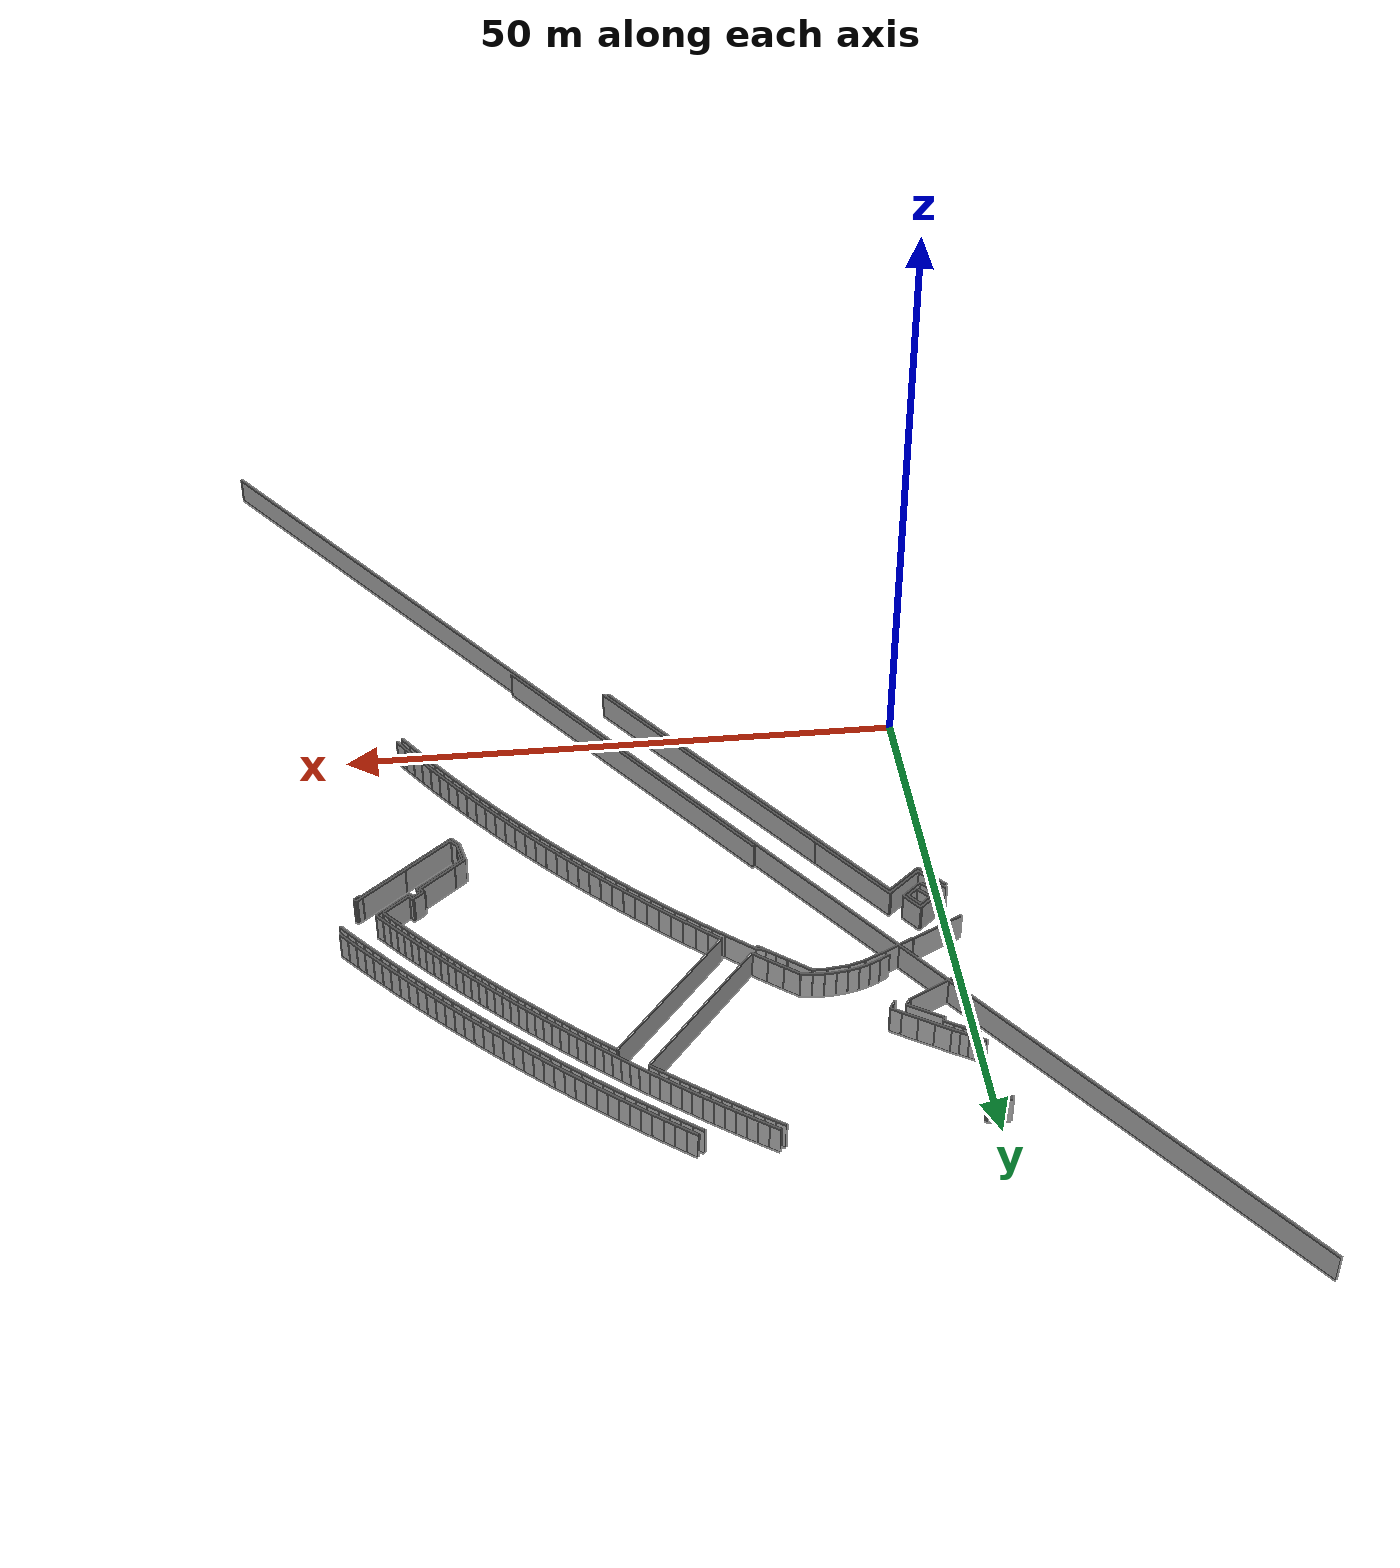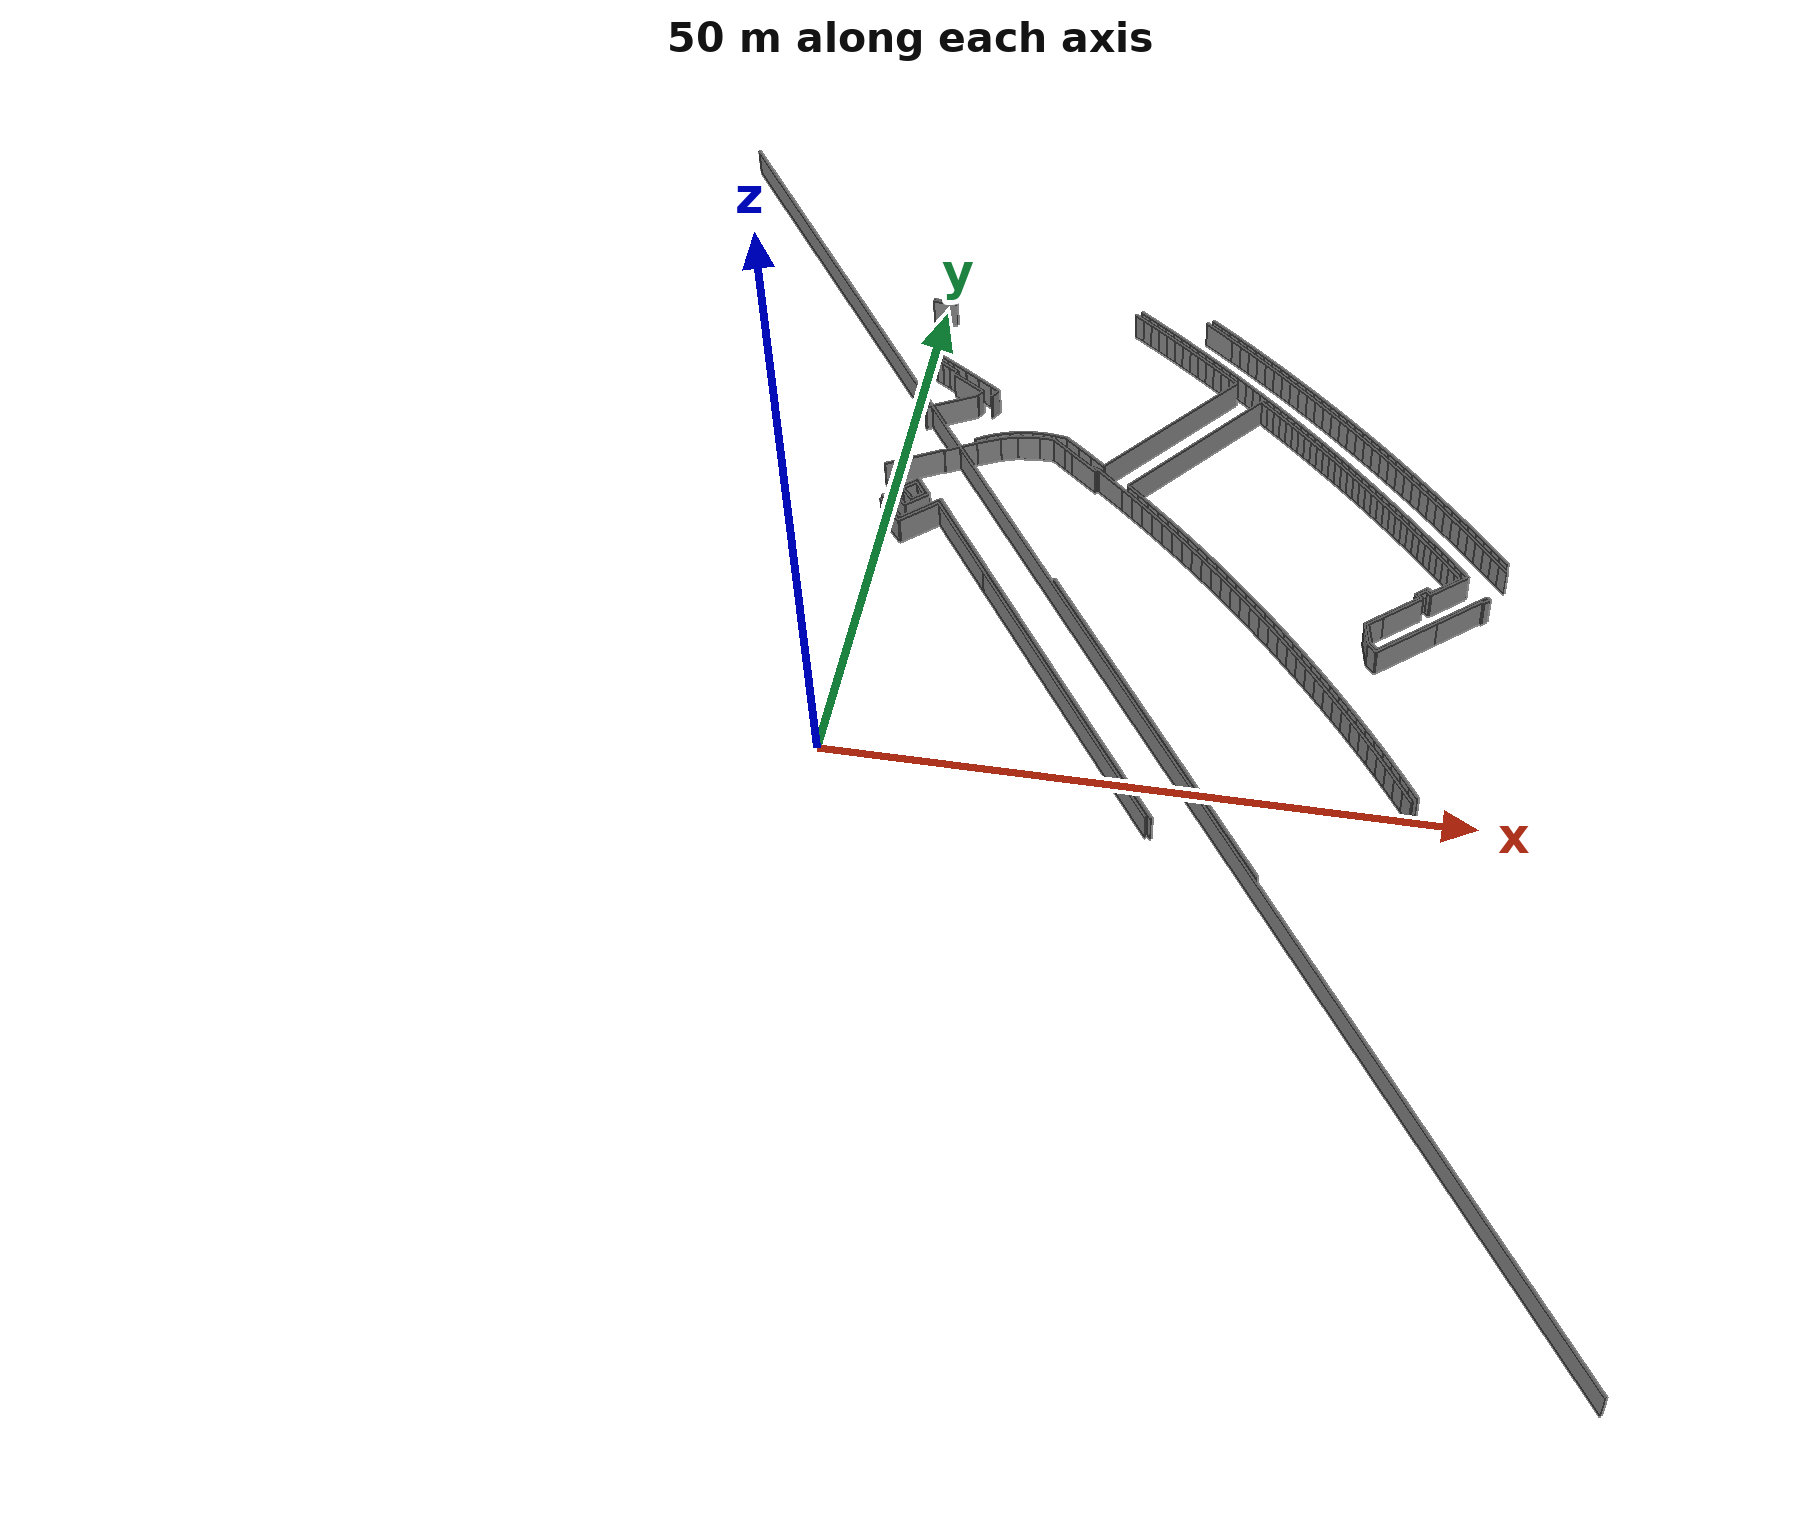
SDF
<?xml version="1.0" ?>
<sdf version="1.6">
  <model name="sps_0605">
    <pose frame="">0 0 0 0 -0 0</pose>
    <static>1</static>
    <self_collide>0</self_collide>
    <allow_auto_disable>0</allow_auto_disable>
    <link name="Wall117">
      <kinematic>0</kinematic>
      <gravity>1</gravity>
      <self_collide>0</self_collide>
      <collision name="collision">
        <geometry>
          <box>
            <size>2.0003 0.15 2.5</size>
          </box>
        </geometry>
        <pose frame="">0 0 0 0 -0 0</pose>
      </collision>
      <visual name="visual">
        <geometry>
          <box>
            <size>2.0003 0.15 2.5</size>
          </box>
        </geometry>
        <pose frame="">0 0 0 0 -0 0</pose>
        <cast_shadows>1</cast_shadows>
        <transparency>0.0</transparency>
      </visual>
      <pose frame="">1.11346 24.7877 1.25 0 0 -0.853026</pose>
    </link>
    <link name="Wall118">
      <kinematic>0</kinematic>
      <gravity>1</gravity>
      <self_collide>0</self_collide>
      <collision name="collision">
        <geometry>
          <box>
            <size>5.04032 0.15 2.5</size>
          </box>
        </geometry>
        <pose frame="">0 0 0 0 -0 0</pose>
      </collision>
      <visual name="visual">
        <geometry>
          <box>
            <size>5.04032 0.15 2.5</size>
          </box>
        </geometry>
        <pose frame="">0 0 0 0 -0 0</pose>
        <cast_shadows>1</cast_shadows>
        <transparency>0.0</transparency>
      </visual>
      <pose frame="">1.36855 29.5763 1.25 0 -0 0.481271</pose>
    </link>
    <link name="Wall127">
      <kinematic>0</kinematic>
      <gravity>1</gravity>
      <self_collide>0</self_collide>
      <collision name="collision">
        <geometry>
          <box>
            <size>8.356 0.15 2.5</size>
          </box>
        </geometry>
        <pose frame="">0 0 0 0 -0 0</pose>
      </collision>
      <visual name="visual">
        <geometry>
          <box>
            <size>8.356 0.15 2.5</size>
          </box>
        </geometry>
        <pose frame="">0 0 0 0 -0 0</pose>
        <cast_shadows>1</cast_shadows>
        <transparency>0.0</transparency>
      </visual>
      <pose frame="">6.90592 21.267 1.25 0 0 -0.939968</pose>
    </link>
    <link name="Wall128">
      <kinematic>0</kinematic>
      <gravity>1</gravity>
      <self_collide>0</self_collide>
      <collision name="collision">
        <geometry>
          <box>
            <size>27.8134 0.15 2.5</size>
          </box>
        </geometry>
        <pose frame="">0 0 0 0 -0 0</pose>
      </collision>
      <visual name="visual">
        <geometry>
          <box>
            <size>27.8134 0.15 2.5</size>
          </box>
        </geometry>
        <pose frame="">0 0 0 0 -0 0</pose>
        <cast_shadows>1</cast_shadows>
        <transparency>0.0</transparency>
      </visual>
      <pose frame="">17.5725 6.66289 1.25 0 0 -0.939968</pose>
    </link>
    <link name="Wall129">
      <kinematic>0</kinematic>
      <gravity>1</gravity>
      <self_collide>0</self_collide>
      <collision name="collision">
        <geometry>
          <box>
            <size>15.0006 0.15 2.5</size>
          </box>
        </geometry>
        <pose frame="">0 0 0 0 -0 0</pose>
      </collision>
      <visual name="visual">
        <geometry>
          <box>
            <size>15.0006 0.15 2.5</size>
          </box>
        </geometry>
        <pose frame="">0 0 0 0 -0 0</pose>
        <cast_shadows>1</cast_shadows>
        <transparency>0.0</transparency>
      </visual>
      <pose frame="">24.007 34.8648 1.25 0 0 -2.25896</pose>
    </link>
    <link name="Wall132">
      <kinematic>0</kinematic>
      <gravity>1</gravity>
      <self_collide>0</self_collide>
      <collision name="collision">
        <geometry>
          <box>
            <size>2.84367 0.15 2.5</size>
          </box>
        </geometry>
        <pose frame="">0 0 0 0 -0 0</pose>
      </collision>
      <visual name="visual">
        <geometry>
          <box>
            <size>2.84367 0.15 2.5</size>
          </box>
        </geometry>
        <pose frame="">0 0 0 0 -0 0</pose>
        <cast_shadows>1</cast_shadows>
        <transparency>0.0</transparency>
      </visual>
      <pose frame="">45.6375 22.0598 1.25 0 -0 0.704005</pose>
    </link>
    <link name="Wall134">
      <kinematic>0</kinematic>
      <gravity>1</gravity>
      <self_collide>0</self_collide>
      <collision name="collision">
        <geometry>
          <box>
            <size>4.44426 0.15 2.5</size>
          </box>
        </geometry>
        <pose frame="">0 0 0 0 -0 0</pose>
      </collision>
      <visual name="visual">
        <geometry>
          <box>
            <size>4.44426 0.15 2.5</size>
          </box>
        </geometry>
        <pose frame="">0 0 0 0 -0 0</pose>
        <cast_shadows>1</cast_shadows>
        <transparency>0.0</transparency>
      </visual>
      <pose frame="">46.9038 19.3309 1.25 0 0 -2.4379</pose>
    </link>
    <link name="Wall135">
      <kinematic>0</kinematic>
      <gravity>1</gravity>
      <self_collide>0</self_collide>
      <collision name="collision">
        <geometry>
          <box>
            <size>5.69951 0.15 2.5</size>
          </box>
        </geometry>
        <pose frame="">0 0 0 0 -0 0</pose>
      </collision>
      <visual name="visual">
        <geometry>
          <box>
            <size>5.69951 0.15 2.5</size>
          </box>
        </geometry>
        <pose frame="">0 0 0 0 -0 0</pose>
        <cast_shadows>1</cast_shadows>
        <transparency>0.0</transparency>
      </visual>
      <pose frame="">43.0367 16.0492 1.25 0 0 -2.4379</pose>
    </link>
    <link name="Wall142">
      <kinematic>0</kinematic>
      <gravity>1</gravity>
      <self_collide>0</self_collide>
      <collision name="collision">
        <geometry>
          <box>
            <size>32.8988 0.15 2.5</size>
          </box>
        </geometry>
        <pose frame="">0 0 0 0 -0 0</pose>
      </collision>
      <visual name="visual">
        <geometry>
          <box>
            <size>32.8988 0.15 2.5</size>
          </box>
        </geometry>
        <pose frame="">0 0 0 0 -0 0</pose>
        <cast_shadows>1</cast_shadows>
        <transparency>0.0</transparency>
      </visual>
      <pose frame="">24.7676 4.60935 1.25 0 -0 2.2016</pose>
    </link>
    <link name="Wall503">
      <kinematic>0</kinematic>
      <gravity>1</gravity>
      <self_collide>0</self_collide>
      <collision name="collision">
        <geometry>
          <box>
            <size>1.92365 0.15 2.5</size>
          </box>
        </geometry>
        <pose frame="">0 0 0 0 -0 0</pose>
      </collision>
      <visual name="visual">
        <geometry>
          <box>
            <size>1.92365 0.15 2.5</size>
          </box>
        </geometry>
        <pose frame="">0 0 0 0 -0 0</pose>
        <cast_shadows>1</cast_shadows>
        <transparency>0.0</transparency>
      </visual>
      <pose frame="">0.09246 48.9816 1.25 0 -0 3.11903</pose>
    </link>
    <link name="Wall505">
      <kinematic>0</kinematic>
      <gravity>1</gravity>
      <self_collide>0</self_collide>
      <collision name="collision">
        <geometry>
          <box>
            <size>1.39976 0.15 2.5</size>
          </box>
        </geometry>
        <pose frame="">0 0 0 0 -0 0</pose>
      </collision>
      <visual name="visual">
        <geometry>
          <box>
            <size>1.39976 0.15 2.5</size>
          </box>
        </geometry>
        <pose frame="">0 0 0 0 -0 0</pose>
        <cast_shadows>1</cast_shadows>
        <transparency>0.0</transparency>
      </visual>
      <pose frame="">1.71596 25.3137 1.25 0 -0 2.28813</pose>
    </link>
    <link name="Wall506">
      <kinematic>0</kinematic>
      <gravity>1</gravity>
      <self_collide>0</self_collide>
      <collision name="collision">
        <geometry>
          <box>
            <size>2.00751 0.15 2.5</size>
          </box>
        </geometry>
        <pose frame="">0 0 0 0 -0 0</pose>
      </collision>
      <visual name="visual">
        <geometry>
          <box>
            <size>2.00751 0.15 2.5</size>
          </box>
        </geometry>
        <pose frame="">0 0 0 0 -0 0</pose>
        <cast_shadows>1</cast_shadows>
        <transparency>0.0</transparency>
      </visual>
      <pose frame="">2.85378 26.3078 1.25 0 -0 2.20172</pose>
    </link>
    <link name="Wall515">
      <kinematic>0</kinematic>
      <gravity>1</gravity>
      <self_collide>0</self_collide>
      <collision name="collision">
        <geometry>
          <box>
            <size>27.8982 0.15 2.5</size>
          </box>
        </geometry>
        <pose frame="">0 0 0 0 -0 0</pose>
      </collision>
      <visual name="visual">
        <geometry>
          <box>
            <size>27.8982 0.15 2.5</size>
          </box>
        </geometry>
        <pose frame="">0 0 0 0 -0 0</pose>
        <cast_shadows>1</cast_shadows>
        <transparency>0.0</transparency>
      </visual>
      <pose frame="">17.9696 6.62858 1.25 0 -0 2.20162</pose>
    </link>
    <link name="Wall516">
      <kinematic>0</kinematic>
      <gravity>1</gravity>
      <self_collide>0</self_collide>
      <collision name="collision">
        <geometry>
          <box>
            <size>8.90203 0.15 2.5</size>
          </box>
        </geometry>
        <pose frame="">0 0 0 0 -0 0</pose>
      </collision>
      <visual name="visual">
        <geometry>
          <box>
            <size>8.90203 0.15 2.5</size>
          </box>
        </geometry>
        <pose frame="">0 0 0 0 -0 0</pose>
        <cast_shadows>1</cast_shadows>
        <transparency>0.0</transparency>
      </visual>
      <pose frame="">7.11708 21.4875 1.25 0 -0 2.20162</pose>
    </link>
    <link name="Wall520">
      <kinematic>0</kinematic>
      <gravity>1</gravity>
      <self_collide>0</self_collide>
      <collision name="collision">
        <geometry>
          <box>
            <size>0.800188 0.15 2.5</size>
          </box>
        </geometry>
        <pose frame="">0 0 0 0 -0 0</pose>
      </collision>
      <visual name="visual">
        <geometry>
          <box>
            <size>0.800188 0.15 2.5</size>
          </box>
        </geometry>
        <pose frame="">0 0 0 0 -0 0</pose>
        <cast_shadows>1</cast_shadows>
        <transparency>0.0</transparency>
      </visual>
      <pose frame="">40.629 14.7919 1.25 0 0 -0.867688</pose>
    </link>
    <link name="Wall840">
      <kinematic>0</kinematic>
      <gravity>1</gravity>
      <self_collide>0</self_collide>
      <collision name="collision">
        <geometry>
          <box>
            <size>1.26984 0.15 2.5</size>
          </box>
        </geometry>
        <pose frame="">0 0 0 0 -0 0</pose>
      </collision>
      <visual name="visual">
        <geometry>
          <box>
            <size>1.26984 0.15 2.5</size>
          </box>
        </geometry>
        <pose frame="">0 0 0 0 -0 0</pose>
        <cast_shadows>1</cast_shadows>
        <transparency>0.0</transparency>
      </visual>
      <pose frame="">1.73406 26.2588 1.25 0 -0 0.717984</pose>
    </link>
    <link name="Wall841">
      <kinematic>0</kinematic>
      <gravity>1</gravity>
      <self_collide>0</self_collide>
      <collision name="collision">
        <geometry>
          <box>
            <size>2.39778 0.15 2.5</size>
          </box>
        </geometry>
        <pose frame="">0 0 0 0 -0 0</pose>
      </collision>
      <visual name="visual">
        <geometry>
          <box>
            <size>2.39778 0.15 2.5</size>
          </box>
        </geometry>
        <pose frame="">0 0 0 0 -0 0</pose>
        <cast_shadows>1</cast_shadows>
        <transparency>0.0</transparency>
      </visual>
      <pose frame="">1.35866 26.3297 1.25 0 0 -2.42373</pose>
    </link>
    <link name="Wall843">
      <kinematic>0</kinematic>
      <gravity>1</gravity>
      <self_collide>0</self_collide>
      <collision name="collision">
        <geometry>
          <box>
            <size>4.51436 0.15 2.5</size>
          </box>
        </geometry>
        <pose frame="">0 0 0 0 -0 0</pose>
      </collision>
      <visual name="visual">
        <geometry>
          <box>
            <size>4.51436 0.15 2.5</size>
          </box>
        </geometry>
        <pose frame="">0 0 0 0 -0 0</pose>
        <cast_shadows>1</cast_shadows>
        <transparency>0.0</transparency>
      </visual>
      <pose frame="">3.09734 36.5783 1.25 0 0 -2.66025</pose>
    </link>
    <link name="Wall844">
      <kinematic>0</kinematic>
      <gravity>1</gravity>
      <self_collide>0</self_collide>
      <collision name="collision">
        <geometry>
          <box>
            <size>2.80838 0.15 2.5</size>
          </box>
        </geometry>
        <pose frame="">0 0 0 0 -0 0</pose>
      </collision>
      <visual name="visual">
        <geometry>
          <box>
            <size>2.80838 0.15 2.5</size>
          </box>
        </geometry>
        <pose frame="">0 0 0 0 -0 0</pose>
        <cast_shadows>1</cast_shadows>
        <transparency>0.0</transparency>
      </visual>
      <pose frame="">4.87875 31.3329 1.25 0 -0 0.48126</pose>
    </link>
    <link name="Wall845">
      <kinematic>0</kinematic>
      <gravity>1</gravity>
      <self_collide>0</self_collide>
      <collision name="collision">
        <geometry>
          <box>
            <size>2.02602 0.15 2.5</size>
          </box>
        </geometry>
        <pose frame="">0 0 0 0 -0 0</pose>
      </collision>
      <visual name="visual">
        <geometry>
          <box>
            <size>2.02602 0.15 2.5</size>
          </box>
        </geometry>
        <pose frame="">0 0 0 0 -0 0</pose>
        <cast_shadows>1</cast_shadows>
        <transparency>0.0</transparency>
      </visual>
      <pose frame="">7.04064 32.4129 1.25 0 -0 0.438411</pose>
    </link>
    <link name="Wall849">
      <kinematic>0</kinematic>
      <gravity>1</gravity>
      <self_collide>0</self_collide>
      <collision name="collision">
        <geometry>
          <box>
            <size>1.92368 0.15 2.5</size>
          </box>
        </geometry>
        <pose frame="">0 0 0 0 -0 0</pose>
      </collision>
      <visual name="visual">
        <geometry>
          <box>
            <size>1.92368 0.15 2.5</size>
          </box>
        </geometry>
        <pose frame="">0 0 0 0 -0 0</pose>
        <cast_shadows>1</cast_shadows>
        <transparency>0.0</transparency>
      </visual>
      <pose frame="">40.1633 16.0364 1.25 0 0 -1.35389</pose>
    </link>
    <link name="Wall851">
      <kinematic>0</kinematic>
      <gravity>1</gravity>
      <self_collide>0</self_collide>
      <collision name="collision">
        <geometry>
          <box>
            <size>3.78169 0.15 2.5</size>
          </box>
        </geometry>
        <pose frame="">0 0 0 0 -0 0</pose>
      </collision>
      <visual name="visual">
        <geometry>
          <box>
            <size>3.78169 0.15 2.5</size>
          </box>
        </geometry>
        <pose frame="">0 0 0 0 -0 0</pose>
        <cast_shadows>1</cast_shadows>
        <transparency>0.0</transparency>
      </visual>
      <pose frame="">42.4788 19.1166 1.25 0 0 -2.43786</pose>
    </link>
    <link name="Wall852">
      <kinematic>0</kinematic>
      <gravity>1</gravity>
      <self_collide>0</self_collide>
      <collision name="collision">
        <geometry>
          <box>
            <size>1.41771 0.15 2.5</size>
          </box>
        </geometry>
        <pose frame="">0 0 0 0 -0 0</pose>
      </collision>
      <visual name="visual">
        <geometry>
          <box>
            <size>1.41771 0.15 2.5</size>
          </box>
        </geometry>
        <pose frame="">0 0 0 0 -0 0</pose>
        <cast_shadows>1</cast_shadows>
        <transparency>0.0</transparency>
      </visual>
      <pose frame="">40.4967 17.4344 1.25 0 0 -2.43786</pose>
    </link>
    <link name="Wall854">
      <kinematic>0</kinematic>
      <gravity>1</gravity>
      <self_collide>0</self_collide>
      <collision name="collision">
        <geometry>
          <box>
            <size>4.70152 0.15 2.5</size>
          </box>
        </geometry>
        <pose frame="">0 0 0 0 -0 0</pose>
      </collision>
      <visual name="visual">
        <geometry>
          <box>
            <size>4.70152 0.15 2.5</size>
          </box>
        </geometry>
        <pose frame="">0 0 0 0 -0 0</pose>
        <cast_shadows>1</cast_shadows>
        <transparency>0.0</transparency>
      </visual>
      <pose frame="">46.693 19.4143 1.25 0 0 -2.4378</pose>
    </link>
    <link name="Wall855">
      <kinematic>0</kinematic>
      <gravity>1</gravity>
      <self_collide>0</self_collide>
      <collision name="collision">
        <geometry>
          <box>
            <size>5.26394 0.15 2.5</size>
          </box>
        </geometry>
        <pose frame="">0 0 0 0 -0 0</pose>
      </collision>
      <visual name="visual">
        <geometry>
          <box>
            <size>5.26394 0.15 2.5</size>
          </box>
        </geometry>
        <pose frame="">0 0 0 0 -0 0</pose>
        <cast_shadows>1</cast_shadows>
        <transparency>0.0</transparency>
      </visual>
      <pose frame="">42.8943 16.1899 1.25 0 0 -2.4378</pose>
    </link>
    <link name="Wall1246">
      <kinematic>0</kinematic>
      <gravity>1</gravity>
      <self_collide>0</self_collide>
      <collision name="collision">
        <geometry>
          <box>
            <size>3.00047 0.15 2.5</size>
          </box>
        </geometry>
        <pose frame="">0 0 0 0 -0 0</pose>
      </collision>
      <visual name="visual">
        <geometry>
          <box>
            <size>3.00047 0.15 2.5</size>
          </box>
        </geometry>
        <pose frame="">0 0 0 0 -0 0</pose>
        <cast_shadows>1</cast_shadows>
        <transparency>0.0</transparency>
      </visual>
      <pose frame="">0.65966 23.3303 1.25 0 0 -0.853126</pose>
    </link>
    <link name="Wall1247">
      <kinematic>0</kinematic>
      <gravity>1</gravity>
      <self_collide>0</self_collide>
      <collision name="collision">
        <geometry>
          <box>
            <size>3.00035 0.15 2.5</size>
          </box>
        </geometry>
        <pose frame="">0 0 0 0 -0 0</pose>
      </collision>
      <visual name="visual">
        <geometry>
          <box>
            <size>3.00035 0.15 2.5</size>
          </box>
        </geometry>
        <pose frame="">0 0 0 0 -0 0</pose>
        <cast_shadows>1</cast_shadows>
        <transparency>0.0</transparency>
      </visual>
      <pose frame="">0.68856 23.7533 1.25 0 -0 2.28842</pose>
    </link>
    <link name="Wall1249">
      <kinematic>0</kinematic>
      <gravity>1</gravity>
      <self_collide>0</self_collide>
      <collision name="collision">
        <geometry>
          <box>
            <size>1.14843 0.15 2.5</size>
          </box>
        </geometry>
        <pose frame="">0 0 0 0 -0 0</pose>
      </collision>
      <visual name="visual">
        <geometry>
          <box>
            <size>1.14843 0.15 2.5</size>
          </box>
        </geometry>
        <pose frame="">0 0 0 0 -0 0</pose>
        <cast_shadows>1</cast_shadows>
        <transparency>0.0</transparency>
      </visual>
      <pose frame="">2.60854 25.164 1.25 0 0 -2.4237</pose>
    </link>
    <link name="Wall1259">
      <kinematic>0</kinematic>
      <gravity>1</gravity>
      <self_collide>0</self_collide>
      <collision name="collision">
        <geometry>
          <box>
            <size>1.30253 0.15 2.5</size>
          </box>
        </geometry>
        <pose frame="">0 0 0 0 -0 0</pose>
      </collision>
      <visual name="visual">
        <geometry>
          <box>
            <size>1.30253 0.15 2.5</size>
          </box>
        </geometry>
        <pose frame="">0 0 0 0 -0 0</pose>
        <cast_shadows>1</cast_shadows>
        <transparency>0.0</transparency>
      </visual>
      <pose frame="">40.2315 17.4717 1.25 0 -0 0.70368</pose>
    </link>
    <link name="Wall1260">
      <kinematic>0</kinematic>
      <gravity>1</gravity>
      <self_collide>0</self_collide>
      <collision name="collision">
        <geometry>
          <box>
            <size>3.81713 0.15 2.5</size>
          </box>
        </geometry>
        <pose frame="">0 0 0 0 -0 0</pose>
      </collision>
      <visual name="visual">
        <geometry>
          <box>
            <size>3.81713 0.15 2.5</size>
          </box>
        </geometry>
        <pose frame="">0 0 0 0 -0 0</pose>
        <cast_shadows>1</cast_shadows>
        <transparency>0.0</transparency>
      </visual>
      <pose frame="">42.1832 19.128 1.25 0 -0 0.70368</pose>
    </link>
    <link name="Wall1261">
      <kinematic>0</kinematic>
      <gravity>1</gravity>
      <self_collide>0</self_collide>
      <collision name="collision">
        <geometry>
          <box>
            <size>0.500356 0.15 2.5</size>
          </box>
        </geometry>
        <pose frame="">0 0 0 0 -0 0</pose>
      </collision>
      <visual name="visual">
        <geometry>
          <box>
            <size>0.500356 0.15 2.5</size>
          </box>
        </geometry>
        <pose frame="">0 0 0 0 -0 0</pose>
        <cast_shadows>1</cast_shadows>
        <transparency>0.0</transparency>
      </visual>
      <pose frame="">44.3689 21.0484 1.25 0 -0 2.27364</pose>
    </link>
    <link name="Wall1541">
      <kinematic>0</kinematic>
      <gravity>1</gravity>
      <self_collide>0</self_collide>
      <collision name="collision">
        <geometry>
          <box>
            <size>2.09372 0.15 2.5</size>
          </box>
        </geometry>
        <pose frame="">0 0 0 0 -0 0</pose>
      </collision>
      <visual name="visual">
        <geometry>
          <box>
            <size>2.09372 0.15 2.5</size>
          </box>
        </geometry>
        <pose frame="">0 0 0 0 -0 0</pose>
        <cast_shadows>1</cast_shadows>
        <transparency>0.0</transparency>
      </visual>
      <pose frame="">0.123466 48.781 1.25 0 -0 3.11935</pose>
    </link>
    <link name="Wall1549">
      <kinematic>0</kinematic>
      <gravity>1</gravity>
      <self_collide>0</self_collide>
      <collision name="collision">
        <geometry>
          <box>
            <size>0.800142 0.15 2.5</size>
          </box>
        </geometry>
        <pose frame="">0 0 0 0 -0 0</pose>
      </collision>
      <visual name="visual">
        <geometry>
          <box>
            <size>0.800142 0.15 2.5</size>
          </box>
        </geometry>
        <pose frame="">0 0 0 0 -0 0</pose>
        <cast_shadows>1</cast_shadows>
        <transparency>0.0</transparency>
      </visual>
      <pose frame="">43.9021 20.9806 1.25 0 0 -2.43844</pose>
    </link>
    <link name="Wall1550">
      <kinematic>0</kinematic>
      <gravity>1</gravity>
      <self_collide>0</self_collide>
      <collision name="collision">
        <geometry>
          <box>
            <size>0.500335 0.15 2.5</size>
          </box>
        </geometry>
        <pose frame="">0 0 0 0 -0 0</pose>
      </collision>
      <visual name="visual">
        <geometry>
          <box>
            <size>0.500335 0.15 2.5</size>
          </box>
        </geometry>
        <pose frame="">0 0 0 0 -0 0</pose>
        <cast_shadows>1</cast_shadows>
        <transparency>0.0</transparency>
      </visual>
      <pose frame="">44.3919 21.3303 1.25 0 0 -0.867436</pose>
    </link>
    <link name="Wall1851">
      <kinematic>0</kinematic>
      <gravity>1</gravity>
      <self_collide>0</self_collide>
      <collision name="collision">
        <geometry>
          <box>
            <size>0.060937 0.15 2.5</size>
          </box>
        </geometry>
        <pose frame="">0 0 0 0 -0 0</pose>
      </collision>
      <visual name="visual">
        <geometry>
          <box>
            <size>0.060937 0.15 2.5</size>
          </box>
        </geometry>
        <pose frame="">0 0 0 0 -0 0</pose>
        <cast_shadows>1</cast_shadows>
        <transparency>0.0</transparency>
      </visual>
      <pose frame="">1.11135 35.5067 1.25 0 0 -1.0601</pose>
    </link>
    <link name="Wall1852">
      <kinematic>0</kinematic>
      <gravity>1</gravity>
      <self_collide>0</self_collide>
      <collision name="collision">
        <geometry>
          <box>
            <size>1.4052 0.15 2.5</size>
          </box>
        </geometry>
        <pose frame="">0 0 0 0 -0 0</pose>
      </collision>
      <visual name="visual">
        <geometry>
          <box>
            <size>1.4052 0.15 2.5</size>
          </box>
        </geometry>
        <pose frame="">0 0 0 0 -0 0</pose>
        <cast_shadows>1</cast_shadows>
        <transparency>0.0</transparency>
      </visual>
      <pose frame="">2.62664 26.1091 1.25 0 0 -0.939979</pose>
    </link>
    <link name="Wall1854">
      <kinematic>0</kinematic>
      <gravity>1</gravity>
      <self_collide>0</self_collide>
      <collision name="collision">
        <geometry>
          <box>
            <size>0.0678181 0.15 2.5</size>
          </box>
        </geometry>
        <pose frame="">0 0 0 0 -0 0</pose>
      </collision>
      <visual name="visual">
        <geometry>
          <box>
            <size>0.0678181 0.15 2.5</size>
          </box>
        </geometry>
        <pose frame="">0 0 0 0 -0 0</pose>
        <cast_shadows>1</cast_shadows>
        <transparency>0.0</transparency>
      </visual>
      <pose frame="">3.61825 30.7129 1.25 0 0 -1.08582</pose>
    </link>
    <link name="Wall1857">
      <kinematic>0</kinematic>
      <gravity>1</gravity>
      <self_collide>0</self_collide>
      <collision name="collision">
        <geometry>
          <box>
            <size>0.789944 0.15 2.5</size>
          </box>
        </geometry>
        <pose frame="">0 0 0 0 -0 0</pose>
      </collision>
      <visual name="visual">
        <geometry>
          <box>
            <size>0.789944 0.15 2.5</size>
          </box>
        </geometry>
        <pose frame="">0 0 0 0 -0 0</pose>
        <cast_shadows>1</cast_shadows>
        <transparency>0.0</transparency>
      </visual>
      <pose frame="">16.1693 30.6343 1.25 0 -0 2.82869</pose>
    </link>
    <link name="Wall1858">
      <kinematic>0</kinematic>
      <gravity>1</gravity>
      <self_collide>0</self_collide>
      <collision name="collision">
        <geometry>
          <box>
            <size>14.981 0.15 2.5</size>
          </box>
        </geometry>
        <pose frame="">0 0 0 0 -0 0</pose>
      </collision>
      <visual name="visual">
        <geometry>
          <box>
            <size>14.981 0.15 2.5</size>
          </box>
        </geometry>
        <pose frame="">0 0 0 0 -0 0</pose>
        <cast_shadows>1</cast_shadows>
        <transparency>0.0</transparency>
      </visual>
      <pose frame="">21.6967 36.778 1.25 0 0 -2.25893</pose>
    </link>
    <link name="Wall1864">
      <kinematic>0</kinematic>
      <gravity>1</gravity>
      <self_collide>0</self_collide>
      <collision name="collision">
        <geometry>
          <box>
            <size>0.500521 0.15 2.5</size>
          </box>
        </geometry>
        <pose frame="">0 0 0 0 -0 0</pose>
      </collision>
      <visual name="visual">
        <geometry>
          <box>
            <size>0.500521 0.15 2.5</size>
          </box>
        </geometry>
        <pose frame="">0 0 0 0 -0 0</pose>
        <cast_shadows>1</cast_shadows>
        <transparency>0.0</transparency>
      </visual>
      <pose frame="">43.4766 20.5538 1.25 0 -0 2.27384</pose>
    </link>
    <link name="Wall1865">
      <kinematic>0</kinematic>
      <gravity>1</gravity>
      <self_collide>0</self_collide>
      <collision name="collision">
        <geometry>
          <box>
            <size>0.500435 0.15 2.5</size>
          </box>
        </geometry>
        <pose frame="">0 0 0 0 -0 0</pose>
      </collision>
      <visual name="visual">
        <geometry>
          <box>
            <size>0.500435 0.15 2.5</size>
          </box>
        </geometry>
        <pose frame="">0 0 0 0 -0 0</pose>
        <cast_shadows>1</cast_shadows>
        <transparency>0.0</transparency>
      </visual>
      <pose frame="">43.7587 20.531 1.25 0 0 -0.867766</pose>
    </link>
    <link name="Wall1866">
      <kinematic>0</kinematic>
      <gravity>1</gravity>
      <self_collide>0</self_collide>
      <collision name="collision">
        <geometry>
          <box>
            <size>1.20016 0.15 2.5</size>
          </box>
        </geometry>
        <pose frame="">0 0 0 0 -0 0</pose>
      </collision>
      <visual name="visual">
        <geometry>
          <box>
            <size>1.20016 0.15 2.5</size>
          </box>
        </geometry>
        <pose frame="">0 0 0 0 -0 0</pose>
        <cast_shadows>1</cast_shadows>
        <transparency>0.0</transparency>
      </visual>
      <pose frame="">43.7725 21.1329 1.25 0 -0 0.703496</pose>
    </link>
    <link name="Wall2194">
      <kinematic>0</kinematic>
      <gravity>1</gravity>
      <self_collide>0</self_collide>
      <collision name="collision">
        <geometry>
          <box>
            <size>0.910391 0.15 2.5</size>
          </box>
        </geometry>
        <pose frame="">0 0 0 0 -0 0</pose>
      </collision>
      <visual name="visual">
        <geometry>
          <box>
            <size>0.910391 0.15 2.5</size>
          </box>
        </geometry>
        <pose frame="">0 0 0 0 -0 0</pose>
        <cast_shadows>1</cast_shadows>
        <transparency>0.0</transparency>
      </visual>
      <pose frame="">2.49227 40.4786 1.25 0 0 -0.553596</pose>
    </link>
    <link name="Wall2195">
      <kinematic>0</kinematic>
      <gravity>1</gravity>
      <self_collide>0</self_collide>
      <collision name="collision">
        <geometry>
          <box>
            <size>2.22364 0.15 2.5</size>
          </box>
        </geometry>
        <pose frame="">0 0 0 0 -0 0</pose>
      </collision>
      <visual name="visual">
        <geometry>
          <box>
            <size>2.22364 0.15 2.5</size>
          </box>
        </geometry>
        <pose frame="">0 0 0 0 -0 0</pose>
        <cast_shadows>1</cast_shadows>
        <transparency>0.0</transparency>
      </visual>
      <pose frame="">2.60857 24.7658 1.25 0 -0 0.718037</pose>
    </link>
    <link name="Wall2196">
      <kinematic>0</kinematic>
      <gravity>1</gravity>
      <self_collide>0</self_collide>
      <collision name="collision">
        <geometry>
          <box>
            <size>3.71104 0.15 2.5</size>
          </box>
        </geometry>
        <pose frame="">0 0 0 0 -0 0</pose>
      </collision>
      <visual name="visual">
        <geometry>
          <box>
            <size>3.71104 0.15 2.5</size>
          </box>
        </geometry>
        <pose frame="">0 0 0 0 -0 0</pose>
        <cast_shadows>1</cast_shadows>
        <transparency>0.0</transparency>
      </visual>
      <pose frame="">3.04397 23.4205 1.25 0 -0 0.717778</pose>
    </link>
    <link name="Wall2197">
      <kinematic>0</kinematic>
      <gravity>1</gravity>
      <self_collide>0</self_collide>
      <collision name="collision">
        <geometry>
          <box>
            <size>3.73893 0.15 2.5</size>
          </box>
        </geometry>
        <pose frame="">0 0 0 0 -0 0</pose>
      </collision>
      <visual name="visual">
        <geometry>
          <box>
            <size>3.73893 0.15 2.5</size>
          </box>
        </geometry>
        <pose frame="">0 0 0 0 -0 0</pose>
        <cast_shadows>1</cast_shadows>
        <transparency>0.0</transparency>
      </visual>
      <pose frame="">3.08346 23.8525 1.25 0 0 -2.42396</pose>
    </link>
    <link name="Wall2200">
      <kinematic>0</kinematic>
      <gravity>1</gravity>
      <self_collide>0</self_collide>
      <collision name="collision">
        <geometry>
          <box>
            <size>3.03822 0.15 2.5</size>
          </box>
        </geometry>
        <pose frame="">0 0 0 0 -0 0</pose>
      </collision>
      <visual name="visual">
        <geometry>
          <box>
            <size>3.03822 0.15 2.5</size>
          </box>
        </geometry>
        <pose frame="">0 0 0 0 -0 0</pose>
        <cast_shadows>1</cast_shadows>
        <transparency>0.0</transparency>
      </visual>
      <pose frame="">24.1541 48.8026 1.25 0 0 -0.643051</pose>
    </link>
    <link name="Wall2583">
      <kinematic>0</kinematic>
      <gravity>1</gravity>
      <self_collide>0</self_collide>
      <collision name="collision">
        <geometry>
          <box>
            <size>0.907783 0.15 2.5</size>
          </box>
        </geometry>
        <pose frame="">0 0 0 0 -0 0</pose>
      </collision>
      <visual name="visual">
        <geometry>
          <box>
            <size>0.907783 0.15 2.5</size>
          </box>
        </geometry>
        <pose frame="">0 0 0 0 -0 0</pose>
        <cast_shadows>1</cast_shadows>
        <transparency>0.0</transparency>
      </visual>
      <pose frame="">6.55437 38.0564 1.25 0 -0 0.990943</pose>
    </link>
    <link name="Wall2584">
      <kinematic>0</kinematic>
      <gravity>1</gravity>
      <self_collide>0</self_collide>
      <collision name="collision">
        <geometry>
          <box>
            <size>0.981156 0.15 2.5</size>
          </box>
        </geometry>
        <pose frame="">0 0 0 0 -0 0</pose>
      </collision>
      <visual name="visual">
        <geometry>
          <box>
            <size>0.981156 0.15 2.5</size>
          </box>
        </geometry>
        <pose frame="">0 0 0 0 -0 0</pose>
        <cast_shadows>1</cast_shadows>
        <transparency>0.0</transparency>
      </visual>
      <pose frame="">6.39425 38.7073 1.25 0 -0 2.5559</pose>
    </link>
    <link name="Wall2585">
      <kinematic>0</kinematic>
      <gravity>1</gravity>
      <self_collide>0</self_collide>
      <collision name="collision">
        <geometry>
          <box>
            <size>0.981156 0.15 2.5</size>
          </box>
        </geometry>
        <pose frame="">0 0 0 0 -0 0</pose>
      </collision>
      <visual name="visual">
        <geometry>
          <box>
            <size>0.981156 0.15 2.5</size>
          </box>
        </geometry>
        <pose frame="">0 0 0 0 -0 0</pose>
        <cast_shadows>1</cast_shadows>
        <transparency>0.0</transparency>
      </visual>
      <pose frame="">6.39425 38.7073 1.25 0 0 -0.585691</pose>
    </link>
    <link name="Wall2600">
      <kinematic>0</kinematic>
      <gravity>1</gravity>
      <self_collide>0</self_collide>
      <collision name="collision">
        <geometry>
          <box>
            <size>2.09363 0.15 2.5</size>
          </box>
        </geometry>
        <pose frame="">0 0 0 0 -0 0</pose>
      </collision>
      <visual name="visual">
        <geometry>
          <box>
            <size>2.09363 0.15 2.5</size>
          </box>
        </geometry>
        <pose frame="">0 0 0 0 -0 0</pose>
        <cast_shadows>1</cast_shadows>
        <transparency>0.0</transparency>
      </visual>
      <pose frame="">39.9601 16.028 1.25 0 -0 1.78761</pose>
    </link>
    <link name="Wall2601">
      <kinematic>0</kinematic>
      <gravity>1</gravity>
      <self_collide>0</self_collide>
      <collision name="collision">
        <geometry>
          <box>
            <size>1.04936 0.15 2.5</size>
          </box>
        </geometry>
        <pose frame="">0 0 0 0 -0 0</pose>
      </collision>
      <visual name="visual">
        <geometry>
          <box>
            <size>1.04936 0.15 2.5</size>
          </box>
        </geometry>
        <pose frame="">0 0 0 0 -0 0</pose>
        <cast_shadows>1</cast_shadows>
        <transparency>0.0</transparency>
      </visual>
      <pose frame="">40.5246 14.6055 1.25 0 -0 2.27401</pose>
    </link>
    <link name="Wall2603">
      <kinematic>0</kinematic>
      <gravity>1</gravity>
      <self_collide>0</self_collide>
      <collision name="collision">
        <geometry>
          <box>
            <size>3.64589 0.15 2.5</size>
          </box>
        </geometry>
        <pose frame="">0 0 0 0 -0 0</pose>
      </collision>
      <visual name="visual">
        <geometry>
          <box>
            <size>3.64589 0.15 2.5</size>
          </box>
        </geometry>
        <pose frame="">0 0 0 0 -0 0</pose>
        <cast_shadows>1</cast_shadows>
        <transparency>0.0</transparency>
      </visual>
      <pose frame="">45.9202 22.0374 1.25 0 0 -2.43762</pose>
    </link>
    <link name="Wall2605">
      <kinematic>0</kinematic>
      <gravity>1</gravity>
      <self_collide>0</self_collide>
      <collision name="collision">
        <geometry>
          <box>
            <size>0.580056 0.15 2.5</size>
          </box>
        </geometry>
        <pose frame="">0 0 0 0 -0 0</pose>
      </collision>
      <visual name="visual">
        <geometry>
          <box>
            <size>0.580056 0.15 2.5</size>
          </box>
        </geometry>
        <pose frame="">0 0 0 0 -0 0</pose>
        <cast_shadows>1</cast_shadows>
        <transparency>0.0</transparency>
      </visual>
      <pose frame="">48.7064 21.1231 1.25 0 -0 0.703388</pose>
    </link>
    <link name="Wall2606">
      <kinematic>0</kinematic>
      <gravity>1</gravity>
      <self_collide>0</self_collide>
      <collision name="collision">
        <geometry>
          <box>
            <size>0.60015 0.15 2.5</size>
          </box>
        </geometry>
        <pose frame="">0 0 0 0 -0 0</pose>
      </collision>
      <visual name="visual">
        <geometry>
          <box>
            <size>0.60015 0.15 2.5</size>
          </box>
        </geometry>
        <pose frame="">0 0 0 0 -0 0</pose>
        <cast_shadows>1</cast_shadows>
        <transparency>0.0</transparency>
      </visual>
      <pose frame="">48.9173 20.8531 1.25 0 0 -2.44816</pose>
    </link>
    <link name="Wall6981">
      <kinematic>0</kinematic>
      <gravity>1</gravity>
      <self_collide>0</self_collide>
      <collision name="collision">
        <geometry>
          <box>
            <size>1.41052 0.15 2.5</size>
          </box>
        </geometry>
        <pose frame="">0 0 0 0 -0 0</pose>
      </collision>
      <visual name="visual">
        <geometry>
          <box>
            <size>1.41052 0.15 2.5</size>
          </box>
        </geometry>
        <pose frame="">0 0 0 0 -0 0</pose>
        <cast_shadows>1</cast_shadows>
        <transparency>0.0</transparency>
      </visual>
      <pose frame="">5.39144 39.3587 1.25 0 -0 2.57221</pose>
    </link>
    <link name="Wall6982">
      <kinematic>0</kinematic>
      <gravity>1</gravity>
      <self_collide>0</self_collide>
      <collision name="collision">
        <geometry>
          <box>
            <size>1.41024 0.15 2.5</size>
          </box>
        </geometry>
        <pose frame="">0 0 0 0 -0 0</pose>
      </collision>
      <visual name="visual">
        <geometry>
          <box>
            <size>1.41024 0.15 2.5</size>
          </box>
        </geometry>
        <pose frame="">0 0 0 0 -0 0</pose>
        <cast_shadows>1</cast_shadows>
        <transparency>0.0</transparency>
      </visual>
      <pose frame="">4.20156 40.1159 1.25 0 -0 2.57752</pose>
    </link>
    <link name="Wall6983">
      <kinematic>0</kinematic>
      <gravity>1</gravity>
      <self_collide>0</self_collide>
      <collision name="collision">
        <geometry>
          <box>
            <size>1.4105 0.15 2.5</size>
          </box>
        </geometry>
        <pose frame="">0 0 0 0 -0 0</pose>
      </collision>
      <visual name="visual">
        <geometry>
          <box>
            <size>1.4105 0.15 2.5</size>
          </box>
        </geometry>
        <pose frame="">0 0 0 0 -0 0</pose>
        <cast_shadows>1</cast_shadows>
        <transparency>0.0</transparency>
      </visual>
      <pose frame="">3.00777 40.8669 1.25 0 -0 2.58259</pose>
    </link>
    <link name="Wall6984">
      <kinematic>0</kinematic>
      <gravity>1</gravity>
      <self_collide>0</self_collide>
      <collision name="collision">
        <geometry>
          <box>
            <size>0.737329 0.15 2.5</size>
          </box>
        </geometry>
        <pose frame="">0 0 0 0 -0 0</pose>
      </collision>
      <visual name="visual">
        <geometry>
          <box>
            <size>0.737329 0.15 2.5</size>
          </box>
        </geometry>
        <pose frame="">0 0 0 0 -0 0</pose>
        <cast_shadows>1</cast_shadows>
        <transparency>0.0</transparency>
      </visual>
      <pose frame="">2.09557 41.4336 1.25 0 -0 2.59162</pose>
    </link>
    <link name="Wall6985">
      <kinematic>0</kinematic>
      <gravity>1</gravity>
      <self_collide>0</self_collide>
      <collision name="collision">
        <geometry>
          <box>
            <size>0.73724 0.15 2.5</size>
          </box>
        </geometry>
        <pose frame="">0 0 0 0 -0 0</pose>
      </collision>
      <visual name="visual">
        <geometry>
          <box>
            <size>0.73724 0.15 2.5</size>
          </box>
        </geometry>
        <pose frame="">0 0 0 0 -0 0</pose>
        <cast_shadows>1</cast_shadows>
        <transparency>0.0</transparency>
      </visual>
      <pose frame="">1.46606 41.8174 1.25 0 -0 2.59659</pose>
    </link>
    <link name="Wall6986">
      <kinematic>0</kinematic>
      <gravity>1</gravity>
      <self_collide>0</self_collide>
      <collision name="collision">
        <geometry>
          <box>
            <size>0.7374 0.15 2.5</size>
          </box>
        </geometry>
        <pose frame="">0 0 0 0 -0 0</pose>
      </collision>
      <visual name="visual">
        <geometry>
          <box>
            <size>0.7374 0.15 2.5</size>
          </box>
        </geometry>
        <pose frame="">0 0 0 0 -0 0</pose>
        <cast_shadows>1</cast_shadows>
        <transparency>0.0</transparency>
      </visual>
      <pose frame="">0.834556 42.198 1.25 0 -0 2.60184</pose>
    </link>
    <link name="Wall6987">
      <kinematic>0</kinematic>
      <gravity>1</gravity>
      <self_collide>0</self_collide>
      <collision name="collision">
        <geometry>
          <box>
            <size>0.737256 0.15 2.5</size>
          </box>
        </geometry>
        <pose frame="">0 0 0 0 -0 0</pose>
      </collision>
      <visual name="visual">
        <geometry>
          <box>
            <size>0.737256 0.15 2.5</size>
          </box>
        </geometry>
        <pose frame="">0 0 0 0 -0 0</pose>
        <cast_shadows>1</cast_shadows>
        <transparency>0.0</transparency>
      </visual>
      <pose frame="">0.201072 42.5753 1.25 0 -0 2.60702</pose>
    </link>
    <link name="Wall7032">
      <kinematic>0</kinematic>
      <gravity>1</gravity>
      <self_collide>0</self_collide>
      <collision name="collision">
        <geometry>
          <box>
            <size>1.00283 0.15 2.5</size>
          </box>
        </geometry>
        <pose frame="">0 0 0 0 -0 0</pose>
      </collision>
      <visual name="visual">
        <geometry>
          <box>
            <size>1.00283 0.15 2.5</size>
          </box>
        </geometry>
        <pose frame="">0 0 0 0 -0 0</pose>
        <cast_shadows>1</cast_shadows>
        <transparency>0.0</transparency>
      </visual>
      <pose frame="">13.8108 32.2899 1.25 0 0 -0.649892</pose>
    </link>
    <link name="Wall7033">
      <kinematic>0</kinematic>
      <gravity>1</gravity>
      <self_collide>0</self_collide>
      <collision name="collision">
        <geometry>
          <box>
            <size>1.00257 0.15 2.5</size>
          </box>
        </geometry>
        <pose frame="">0 0 0 0 -0 0</pose>
      </collision>
      <visual name="visual">
        <geometry>
          <box>
            <size>1.00257 0.15 2.5</size>
          </box>
        </geometry>
        <pose frame="">0 0 0 0 -0 0</pose>
        <cast_shadows>1</cast_shadows>
        <transparency>0.0</transparency>
      </visual>
      <pose frame="">14.607 31.6803 1.25 0 0 -0.657065</pose>
    </link>
    <link name="Wall7034">
      <kinematic>0</kinematic>
      <gravity>1</gravity>
      <self_collide>0</self_collide>
      <collision name="collision">
        <geometry>
          <box>
            <size>1.00284 0.15 2.5</size>
          </box>
        </geometry>
        <pose frame="">0 0 0 0 -0 0</pose>
      </collision>
      <visual name="visual">
        <geometry>
          <box>
            <size>1.00284 0.15 2.5</size>
          </box>
        </geometry>
        <pose frame="">0 0 0 0 -0 0</pose>
        <cast_shadows>1</cast_shadows>
        <transparency>0.0</transparency>
      </visual>
      <pose frame="">15.3987 31.065 1.25 0 0 -0.664257</pose>
    </link>
    <link name="Wall7046">
      <kinematic>0</kinematic>
      <gravity>1</gravity>
      <self_collide>0</self_collide>
      <collision name="collision">
        <geometry>
          <box>
            <size>1.25429 0.15 2.5</size>
          </box>
        </geometry>
        <pose frame="">0 0 0 0 -0 0</pose>
      </collision>
      <visual name="visual">
        <geometry>
          <box>
            <size>1.25429 0.15 2.5</size>
          </box>
        </geometry>
        <pose frame="">0 0 0 0 -0 0</pose>
        <cast_shadows>1</cast_shadows>
        <transparency>0.0</transparency>
      </visual>
      <pose frame="">44.9 0.850783 1.25 0 -0 2.17448</pose>
    </link>
    <link name="Wall7047">
      <kinematic>0</kinematic>
      <gravity>1</gravity>
      <self_collide>0</self_collide>
      <collision name="collision">
        <geometry>
          <box>
            <size>1.25422 0.15 2.5</size>
          </box>
        </geometry>
        <pose frame="">0 0 0 0 -0 0</pose>
      </collision>
      <visual name="visual">
        <geometry>
          <box>
            <size>1.25422 0.15 2.5</size>
          </box>
        </geometry>
        <pose frame="">0 0 0 0 -0 0</pose>
        <cast_shadows>1</cast_shadows>
        <transparency>0.0</transparency>
      </visual>
      <pose frame="">44.1836 1.88029 1.25 0 -0 2.183</pose>
    </link>
    <link name="Wall7048">
      <kinematic>0</kinematic>
      <gravity>1</gravity>
      <self_collide>0</self_collide>
      <collision name="collision">
        <geometry>
          <box>
            <size>1.25427 0.15 2.5</size>
          </box>
        </geometry>
        <pose frame="">0 0 0 0 -0 0</pose>
      </collision>
      <visual name="visual">
        <geometry>
          <box>
            <size>1.25427 0.15 2.5</size>
          </box>
        </geometry>
        <pose frame="">0 0 0 0 -0 0</pose>
        <cast_shadows>1</cast_shadows>
        <transparency>0.0</transparency>
      </visual>
      <pose frame="">43.4583 2.90349 1.25 0 -0 2.19198</pose>
    </link>
    <link name="Wall7049">
      <kinematic>0</kinematic>
      <gravity>1</gravity>
      <self_collide>0</self_collide>
      <collision name="collision">
        <geometry>
          <box>
            <size>1.25441 0.15 2.5</size>
          </box>
        </geometry>
        <pose frame="">0 0 0 0 -0 0</pose>
      </collision>
      <visual name="visual">
        <geometry>
          <box>
            <size>1.25441 0.15 2.5</size>
          </box>
        </geometry>
        <pose frame="">0 0 0 0 -0 0</pose>
        <cast_shadows>1</cast_shadows>
        <transparency>0.0</transparency>
      </visual>
      <pose frame="">42.7238 3.92027 1.25 0 -0 2.20078</pose>
    </link>
    <link name="Wall7050">
      <kinematic>0</kinematic>
      <gravity>1</gravity>
      <self_collide>0</self_collide>
      <collision name="collision">
        <geometry>
          <box>
            <size>1.25416 0.15 2.5</size>
          </box>
        </geometry>
        <pose frame="">0 0 0 0 -0 0</pose>
      </collision>
      <visual name="visual">
        <geometry>
          <box>
            <size>1.25416 0.15 2.5</size>
          </box>
        </geometry>
        <pose frame="">0 0 0 0 -0 0</pose>
        <cast_shadows>1</cast_shadows>
        <transparency>0.0</transparency>
      </visual>
      <pose frame="">41.9804 4.9305 1.25 0 -0 2.20963</pose>
    </link>
    <link name="Wall7051">
      <kinematic>0</kinematic>
      <gravity>1</gravity>
      <self_collide>0</self_collide>
      <collision name="collision">
        <geometry>
          <box>
            <size>1.25441 0.15 2.5</size>
          </box>
        </geometry>
        <pose frame="">0 0 0 0 -0 0</pose>
      </collision>
      <visual name="visual">
        <geometry>
          <box>
            <size>1.25441 0.15 2.5</size>
          </box>
        </geometry>
        <pose frame="">0 0 0 0 -0 0</pose>
        <cast_shadows>1</cast_shadows>
        <transparency>0.0</transparency>
      </visual>
      <pose frame="">41.228 5.9341 1.25 0 -0 2.21848</pose>
    </link>
    <link name="Wall7052">
      <kinematic>0</kinematic>
      <gravity>1</gravity>
      <self_collide>0</self_collide>
      <collision name="collision">
        <geometry>
          <box>
            <size>1.25421 0.15 2.5</size>
          </box>
        </geometry>
        <pose frame="">0 0 0 0 -0 0</pose>
      </collision>
      <visual name="visual">
        <geometry>
          <box>
            <size>1.25421 0.15 2.5</size>
          </box>
        </geometry>
        <pose frame="">0 0 0 0 -0 0</pose>
        <cast_shadows>1</cast_shadows>
        <transparency>0.0</transparency>
      </visual>
      <pose frame="">40.4669 6.93108 1.25 0 -0 2.22717</pose>
    </link>
    <link name="Wall7053">
      <kinematic>0</kinematic>
      <gravity>1</gravity>
      <self_collide>0</self_collide>
      <collision name="collision">
        <geometry>
          <box>
            <size>1.25425 0.15 2.5</size>
          </box>
        </geometry>
        <pose frame="">0 0 0 0 -0 0</pose>
      </collision>
      <visual name="visual">
        <geometry>
          <box>
            <size>1.25425 0.15 2.5</size>
          </box>
        </geometry>
        <pose frame="">0 0 0 0 -0 0</pose>
        <cast_shadows>1</cast_shadows>
        <transparency>0.0</transparency>
      </visual>
      <pose frame="">39.6972 7.92128 1.25 0 -0 2.23602</pose>
    </link>
    <link name="Wall7054">
      <kinematic>0</kinematic>
      <gravity>1</gravity>
      <self_collide>0</self_collide>
      <collision name="collision">
        <geometry>
          <box>
            <size>1.25427 0.15 2.5</size>
          </box>
        </geometry>
        <pose frame="">0 0 0 0 -0 0</pose>
      </collision>
      <visual name="visual">
        <geometry>
          <box>
            <size>1.25427 0.15 2.5</size>
          </box>
        </geometry>
        <pose frame="">0 0 0 0 -0 0</pose>
        <cast_shadows>1</cast_shadows>
        <transparency>0.0</transparency>
      </visual>
      <pose frame="">38.9187 8.90468 1.25 0 -0 2.24482</pose>
    </link>
    <link name="Wall7055">
      <kinematic>0</kinematic>
      <gravity>1</gravity>
      <self_collide>0</self_collide>
      <collision name="collision">
        <geometry>
          <box>
            <size>1.25422 0.15 2.5</size>
          </box>
        </geometry>
        <pose frame="">0 0 0 0 -0 0</pose>
      </collision>
      <visual name="visual">
        <geometry>
          <box>
            <size>1.25422 0.15 2.5</size>
          </box>
        </geometry>
        <pose frame="">0 0 0 0 -0 0</pose>
        <cast_shadows>1</cast_shadows>
        <transparency>0.0</transparency>
      </visual>
      <pose frame="">38.1316 9.88118 1.25 0 -0 2.25361</pose>
    </link>
    <link name="Wall7056">
      <kinematic>0</kinematic>
      <gravity>1</gravity>
      <self_collide>0</self_collide>
      <collision name="collision">
        <geometry>
          <box>
            <size>1.25425 0.15 2.5</size>
          </box>
        </geometry>
        <pose frame="">0 0 0 0 -0 0</pose>
      </collision>
      <visual name="visual">
        <geometry>
          <box>
            <size>1.25425 0.15 2.5</size>
          </box>
        </geometry>
        <pose frame="">0 0 0 0 -0 0</pose>
        <cast_shadows>1</cast_shadows>
        <transparency>0.0</transparency>
      </visual>
      <pose frame="">37.3359 10.8507 1.25 0 -0 2.26246</pose>
    </link>
    <link name="Wall7057">
      <kinematic>0</kinematic>
      <gravity>1</gravity>
      <self_collide>0</self_collide>
      <collision name="collision">
        <geometry>
          <box>
            <size>1.25412 0.15 2.5</size>
          </box>
        </geometry>
        <pose frame="">0 0 0 0 -0 0</pose>
      </collision>
      <visual name="visual">
        <geometry>
          <box>
            <size>1.25412 0.15 2.5</size>
          </box>
        </geometry>
        <pose frame="">0 0 0 0 -0 0</pose>
        <cast_shadows>1</cast_shadows>
        <transparency>0.0</transparency>
      </visual>
      <pose frame="">36.5317 11.8131 1.25 0 -0 2.2713</pose>
    </link>
    <link name="Wall7058">
      <kinematic>0</kinematic>
      <gravity>1</gravity>
      <self_collide>0</self_collide>
      <collision name="collision">
        <geometry>
          <box>
            <size>1.25424 0.15 2.5</size>
          </box>
        </geometry>
        <pose frame="">0 0 0 0 -0 0</pose>
      </collision>
      <visual name="visual">
        <geometry>
          <box>
            <size>1.25424 0.15 2.5</size>
          </box>
        </geometry>
        <pose frame="">0 0 0 0 -0 0</pose>
        <cast_shadows>1</cast_shadows>
        <transparency>0.0</transparency>
      </visual>
      <pose frame="">35.719 12.7684 1.25 0 -0 2.28004</pose>
    </link>
    <link name="Wall7059">
      <kinematic>0</kinematic>
      <gravity>1</gravity>
      <self_collide>0</self_collide>
      <collision name="collision">
        <geometry>
          <box>
            <size>1.25443 0.15 2.5</size>
          </box>
        </geometry>
        <pose frame="">0 0 0 0 -0 0</pose>
      </collision>
      <visual name="visual">
        <geometry>
          <box>
            <size>1.25443 0.15 2.5</size>
          </box>
        </geometry>
        <pose frame="">0 0 0 0 -0 0</pose>
        <cast_shadows>1</cast_shadows>
        <transparency>0.0</transparency>
      </visual>
      <pose frame="">34.8979 13.7166 1.25 0 -0 2.28892</pose>
    </link>
    <link name="Wall7060">
      <kinematic>0</kinematic>
      <gravity>1</gravity>
      <self_collide>0</self_collide>
      <collision name="collision">
        <geometry>
          <box>
            <size>1.25413 0.15 2.5</size>
          </box>
        </geometry>
        <pose frame="">0 0 0 0 -0 0</pose>
      </collision>
      <visual name="visual">
        <geometry>
          <box>
            <size>1.25413 0.15 2.5</size>
          </box>
        </geometry>
        <pose frame="">0 0 0 0 -0 0</pose>
        <cast_shadows>1</cast_shadows>
        <transparency>0.0</transparency>
      </visual>
      <pose frame="">34.0686 14.6575 1.25 0 -0 2.29762</pose>
    </link>
    <link name="Wall7061">
      <kinematic>0</kinematic>
      <gravity>1</gravity>
      <self_collide>0</self_collide>
      <collision name="collision">
        <geometry>
          <box>
            <size>1.25426 0.15 2.5</size>
          </box>
        </geometry>
        <pose frame="">0 0 0 0 -0 0</pose>
      </collision>
      <visual name="visual">
        <geometry>
          <box>
            <size>1.25426 0.15 2.5</size>
          </box>
        </geometry>
        <pose frame="">0 0 0 0 -0 0</pose>
        <cast_shadows>1</cast_shadows>
        <transparency>0.0</transparency>
      </visual>
      <pose frame="">33.231 15.591 1.25 0 -0 2.30656</pose>
    </link>
    <link name="Wall7062">
      <kinematic>0</kinematic>
      <gravity>1</gravity>
      <self_collide>0</self_collide>
      <collision name="collision">
        <geometry>
          <box>
            <size>1.25445 0.15 2.5</size>
          </box>
        </geometry>
        <pose frame="">0 0 0 0 -0 0</pose>
      </collision>
      <visual name="visual">
        <geometry>
          <box>
            <size>1.25445 0.15 2.5</size>
          </box>
        </geometry>
        <pose frame="">0 0 0 0 -0 0</pose>
        <cast_shadows>1</cast_shadows>
        <transparency>0.0</transparency>
      </visual>
      <pose frame="">32.3851 16.5172 1.25 0 -0 2.31531</pose>
    </link>
    <link name="Wall7063">
      <kinematic>0</kinematic>
      <gravity>1</gravity>
      <self_collide>0</self_collide>
      <collision name="collision">
        <geometry>
          <box>
            <size>1.25423 0.15 2.5</size>
          </box>
        </geometry>
        <pose frame="">0 0 0 0 -0 0</pose>
      </collision>
      <visual name="visual">
        <geometry>
          <box>
            <size>1.25423 0.15 2.5</size>
          </box>
        </geometry>
        <pose frame="">0 0 0 0 -0 0</pose>
        <cast_shadows>1</cast_shadows>
        <transparency>0.0</transparency>
      </visual>
      <pose frame="">31.5312 17.436 1.25 0 -0 2.32391</pose>
    </link>
    <link name="Wall7064">
      <kinematic>0</kinematic>
      <gravity>1</gravity>
      <self_collide>0</self_collide>
      <collision name="collision">
        <geometry>
          <box>
            <size>1.25417 0.15 2.5</size>
          </box>
        </geometry>
        <pose frame="">0 0 0 0 -0 0</pose>
      </collision>
      <visual name="visual">
        <geometry>
          <box>
            <size>1.25417 0.15 2.5</size>
          </box>
        </geometry>
        <pose frame="">0 0 0 0 -0 0</pose>
        <cast_shadows>1</cast_shadows>
        <transparency>0.0</transparency>
      </visual>
      <pose frame="">30.6692 18.3471 1.25 0 -0 2.333</pose>
    </link>
    <link name="Wall7065">
      <kinematic>0</kinematic>
      <gravity>1</gravity>
      <self_collide>0</self_collide>
      <collision name="collision">
        <geometry>
          <box>
            <size>1.2544 0.15 2.5</size>
          </box>
        </geometry>
        <pose frame="">0 0 0 0 -0 0</pose>
      </collision>
      <visual name="visual">
        <geometry>
          <box>
            <size>1.2544 0.15 2.5</size>
          </box>
        </geometry>
        <pose frame="">0 0 0 0 -0 0</pose>
        <cast_shadows>1</cast_shadows>
        <transparency>0.0</transparency>
      </visual>
      <pose frame="">29.7992 19.2506 1.25 0 -0 2.34161</pose>
    </link>
    <link name="Wall7066">
      <kinematic>0</kinematic>
      <gravity>1</gravity>
      <self_collide>0</self_collide>
      <collision name="collision">
        <geometry>
          <box>
            <size>1.25416 0.15 2.5</size>
          </box>
        </geometry>
        <pose frame="">0 0 0 0 -0 0</pose>
      </collision>
      <visual name="visual">
        <geometry>
          <box>
            <size>1.25416 0.15 2.5</size>
          </box>
        </geometry>
        <pose frame="">0 0 0 0 -0 0</pose>
        <cast_shadows>1</cast_shadows>
        <transparency>0.0</transparency>
      </visual>
      <pose frame="">28.9213 20.1464 1.25 0 -0 2.35059</pose>
    </link>
    <link name="Wall7067">
      <kinematic>0</kinematic>
      <gravity>1</gravity>
      <self_collide>0</self_collide>
      <collision name="collision">
        <geometry>
          <box>
            <size>1.25427 0.15 2.5</size>
          </box>
        </geometry>
        <pose frame="">0 0 0 0 -0 0</pose>
      </collision>
      <visual name="visual">
        <geometry>
          <box>
            <size>1.25427 0.15 2.5</size>
          </box>
        </geometry>
        <pose frame="">0 0 0 0 -0 0</pose>
        <cast_shadows>1</cast_shadows>
        <transparency>0.0</transparency>
      </visual>
      <pose frame="">28.0356 21.0344 1.25 0 -0 2.35922</pose>
    </link>
    <link name="Wall7068">
      <kinematic>0</kinematic>
      <gravity>1</gravity>
      <self_collide>0</self_collide>
      <collision name="collision">
        <geometry>
          <box>
            <size>1.25419 0.15 2.5</size>
          </box>
        </geometry>
        <pose frame="">0 0 0 0 -0 0</pose>
      </collision>
      <visual name="visual">
        <geometry>
          <box>
            <size>1.25419 0.15 2.5</size>
          </box>
        </geometry>
        <pose frame="">0 0 0 0 -0 0</pose>
        <cast_shadows>1</cast_shadows>
        <transparency>0.0</transparency>
      </visual>
      <pose frame="">27.1421 21.9146 1.25 0 -0 2.36817</pose>
    </link>
    <link name="Wall7069">
      <kinematic>0</kinematic>
      <gravity>1</gravity>
      <self_collide>0</self_collide>
      <collision name="collision">
        <geometry>
          <box>
            <size>1.25428 0.15 2.5</size>
          </box>
        </geometry>
        <pose frame="">0 0 0 0 -0 0</pose>
      </collision>
      <visual name="visual">
        <geometry>
          <box>
            <size>1.25428 0.15 2.5</size>
          </box>
        </geometry>
        <pose frame="">0 0 0 0 -0 0</pose>
        <cast_shadows>1</cast_shadows>
        <transparency>0.0</transparency>
      </visual>
      <pose frame="">26.2408 22.7868 1.25 0 -0 2.37705</pose>
    </link>
    <link name="Wall7070">
      <kinematic>0</kinematic>
      <gravity>1</gravity>
      <self_collide>0</self_collide>
      <collision name="collision">
        <geometry>
          <box>
            <size>1.25408 0.15 2.5</size>
          </box>
        </geometry>
        <pose frame="">0 0 0 0 -0 0</pose>
      </collision>
      <visual name="visual">
        <geometry>
          <box>
            <size>1.25408 0.15 2.5</size>
          </box>
        </geometry>
        <pose frame="">0 0 0 0 -0 0</pose>
        <cast_shadows>1</cast_shadows>
        <transparency>0.0</transparency>
      </visual>
      <pose frame="">25.3319 23.651 1.25 0 -0 2.38576</pose>
    </link>
    <link name="Wall7071">
      <kinematic>0</kinematic>
      <gravity>1</gravity>
      <self_collide>0</self_collide>
      <collision name="collision">
        <geometry>
          <box>
            <size>1.25445 0.15 2.5</size>
          </box>
        </geometry>
        <pose frame="">0 0 0 0 -0 0</pose>
      </collision>
      <visual name="visual">
        <geometry>
          <box>
            <size>1.25445 0.15 2.5</size>
          </box>
        </geometry>
        <pose frame="">0 0 0 0 -0 0</pose>
        <cast_shadows>1</cast_shadows>
        <transparency>0.0</transparency>
      </visual>
      <pose frame="">24.4155 24.5073 1.25 0 -0 2.3945</pose>
    </link>
    <link name="Wall7072">
      <kinematic>0</kinematic>
      <gravity>1</gravity>
      <self_collide>0</self_collide>
      <collision name="collision">
        <geometry>
          <box>
            <size>1.25441 0.15 2.5</size>
          </box>
        </geometry>
        <pose frame="">0 0 0 0 -0 0</pose>
      </collision>
      <visual name="visual">
        <geometry>
          <box>
            <size>1.25441 0.15 2.5</size>
          </box>
        </geometry>
        <pose frame="">0 0 0 0 -0 0</pose>
        <cast_shadows>1</cast_shadows>
        <transparency>0.0</transparency>
      </visual>
      <pose frame="">23.4914 25.3556 1.25 0 -0 2.40338</pose>
    </link>
    <link name="Wall7073">
      <kinematic>0</kinematic>
      <gravity>1</gravity>
      <self_collide>0</self_collide>
      <collision name="collision">
        <geometry>
          <box>
            <size>1.25412 0.15 2.5</size>
          </box>
        </geometry>
        <pose frame="">0 0 0 0 -0 0</pose>
      </collision>
      <visual name="visual">
        <geometry>
          <box>
            <size>1.25412 0.15 2.5</size>
          </box>
        </geometry>
        <pose frame="">0 0 0 0 -0 0</pose>
        <cast_shadows>1</cast_shadows>
        <transparency>0.0</transparency>
      </visual>
      <pose frame="">22.5599 26.1956 1.25 0 -0 2.41215</pose>
    </link>
    <link name="Wall7074">
      <kinematic>0</kinematic>
      <gravity>1</gravity>
      <self_collide>0</self_collide>
      <collision name="collision">
        <geometry>
          <box>
            <size>1.25434 0.15 2.5</size>
          </box>
        </geometry>
        <pose frame="">0 0 0 0 -0 0</pose>
      </collision>
      <visual name="visual">
        <geometry>
          <box>
            <size>1.25434 0.15 2.5</size>
          </box>
        </geometry>
        <pose frame="">0 0 0 0 -0 0</pose>
        <cast_shadows>1</cast_shadows>
        <transparency>0.0</transparency>
      </visual>
      <pose frame="">21.6212 27.0274 1.25 0 -0 2.42082</pose>
    </link>
    <link name="Wall7075">
      <kinematic>0</kinematic>
      <gravity>1</gravity>
      <self_collide>0</self_collide>
      <collision name="collision">
        <geometry>
          <box>
            <size>1.25426 0.15 2.5</size>
          </box>
        </geometry>
        <pose frame="">0 0 0 0 -0 0</pose>
      </collision>
      <visual name="visual">
        <geometry>
          <box>
            <size>1.25426 0.15 2.5</size>
          </box>
        </geometry>
        <pose frame="">0 0 0 0 -0 0</pose>
        <cast_shadows>1</cast_shadows>
        <transparency>0.0</transparency>
      </visual>
      <pose frame="">20.6752 27.8509 1.25 0 -0 2.42986</pose>
    </link>
    <link name="Wall7076">
      <kinematic>0</kinematic>
      <gravity>1</gravity>
      <self_collide>0</self_collide>
      <collision name="collision">
        <geometry>
          <box>
            <size>1.25429 0.15 2.5</size>
          </box>
        </geometry>
        <pose frame="">0 0 0 0 -0 0</pose>
      </collision>
      <visual name="visual">
        <geometry>
          <box>
            <size>1.25429 0.15 2.5</size>
          </box>
        </geometry>
        <pose frame="">0 0 0 0 -0 0</pose>
        <cast_shadows>1</cast_shadows>
        <transparency>0.0</transparency>
      </visual>
      <pose frame="">19.7219 28.666 1.25 0 -0 2.43852</pose>
    </link>
    <link name="Wall7089">
      <kinematic>0</kinematic>
      <gravity>1</gravity>
      <self_collide>0</self_collide>
      <collision name="collision">
        <geometry>
          <box>
            <size>1.02001 0.15 2.5</size>
          </box>
        </geometry>
        <pose frame="">0 0 0 0 -0 0</pose>
      </collision>
      <visual name="visual">
        <geometry>
          <box>
            <size>1.02001 0.15 2.5</size>
          </box>
        </geometry>
        <pose frame="">0 0 0 0 -0 0</pose>
        <cast_shadows>1</cast_shadows>
        <transparency>0.0</transparency>
      </visual>
      <pose frame="">49.9609 25.5329 1.25 0 -0 2.28251</pose>
    </link>
    <link name="Wall7090">
      <kinematic>0</kinematic>
      <gravity>1</gravity>
      <self_collide>0</self_collide>
      <collision name="collision">
        <geometry>
          <box>
            <size>1.02011 0.15 2.5</size>
          </box>
        </geometry>
        <pose frame="">0 0 0 0 -0 0</pose>
      </collision>
      <visual name="visual">
        <geometry>
          <box>
            <size>1.02011 0.15 2.5</size>
          </box>
        </geometry>
        <pose frame="">0 0 0 0 -0 0</pose>
        <cast_shadows>1</cast_shadows>
        <transparency>0.0</transparency>
      </visual>
      <pose frame="">49.2922 26.3032 1.25 0 -0 2.28892</pose>
    </link>
    <link name="Wall7091">
      <kinematic>0</kinematic>
      <gravity>1</gravity>
      <self_collide>0</self_collide>
      <collision name="collision">
        <geometry>
          <box>
            <size>1.01996 0.15 2.5</size>
          </box>
        </geometry>
        <pose frame="">0 0 0 0 -0 0</pose>
      </collision>
      <visual name="visual">
        <geometry>
          <box>
            <size>1.01996 0.15 2.5</size>
          </box>
        </geometry>
        <pose frame="">0 0 0 0 -0 0</pose>
        <cast_shadows>1</cast_shadows>
        <transparency>0.0</transparency>
      </visual>
      <pose frame="">48.6186 27.0692 1.25 0 -0 2.29527</pose>
    </link>
    <link name="Wall7092">
      <kinematic>0</kinematic>
      <gravity>1</gravity>
      <self_collide>0</self_collide>
      <collision name="collision">
        <geometry>
          <box>
            <size>1.0202 0.15 2.5</size>
          </box>
        </geometry>
        <pose frame="">0 0 0 0 -0 0</pose>
      </collision>
      <visual name="visual">
        <geometry>
          <box>
            <size>1.0202 0.15 2.5</size>
          </box>
        </geometry>
        <pose frame="">0 0 0 0 -0 0</pose>
        <cast_shadows>1</cast_shadows>
        <transparency>0.0</transparency>
      </visual>
      <pose frame="">47.9403 27.831 1.25 0 -0 2.30138</pose>
    </link>
    <link name="Wall7093">
      <kinematic>0</kinematic>
      <gravity>1</gravity>
      <self_collide>0</self_collide>
      <collision name="collision">
        <geometry>
          <box>
            <size>1.01998 0.15 2.5</size>
          </box>
        </geometry>
        <pose frame="">0 0 0 0 -0 0</pose>
      </collision>
      <visual name="visual">
        <geometry>
          <box>
            <size>1.01998 0.15 2.5</size>
          </box>
        </geometry>
        <pose frame="">0 0 0 0 -0 0</pose>
        <cast_shadows>1</cast_shadows>
        <transparency>0.0</transparency>
      </visual>
      <pose frame="">47.2571 28.5885 1.25 0 -0 2.30794</pose>
    </link>
    <link name="Wall7094">
      <kinematic>0</kinematic>
      <gravity>1</gravity>
      <self_collide>0</self_collide>
      <collision name="collision">
        <geometry>
          <box>
            <size>1.02017 0.15 2.5</size>
          </box>
        </geometry>
        <pose frame="">0 0 0 0 -0 0</pose>
      </collision>
      <visual name="visual">
        <geometry>
          <box>
            <size>1.02017 0.15 2.5</size>
          </box>
        </geometry>
        <pose frame="">0 0 0 0 -0 0</pose>
        <cast_shadows>1</cast_shadows>
        <transparency>0.0</transparency>
      </visual>
      <pose frame="">46.5691 29.3416 1.25 0 -0 2.31417</pose>
    </link>
    <link name="Wall7095">
      <kinematic>0</kinematic>
      <gravity>1</gravity>
      <self_collide>0</self_collide>
      <collision name="collision">
        <geometry>
          <box>
            <size>1.02013 0.15 2.5</size>
          </box>
        </geometry>
        <pose frame="">0 0 0 0 -0 0</pose>
      </collision>
      <visual name="visual">
        <geometry>
          <box>
            <size>1.02013 0.15 2.5</size>
          </box>
        </geometry>
        <pose frame="">0 0 0 0 -0 0</pose>
        <cast_shadows>1</cast_shadows>
        <transparency>0.0</transparency>
      </visual>
      <pose frame="">45.8762 30.0904 1.25 0 -0 2.32056</pose>
    </link>
    <link name="Wall7096">
      <kinematic>0</kinematic>
      <gravity>1</gravity>
      <self_collide>0</self_collide>
      <collision name="collision">
        <geometry>
          <box>
            <size>1.02019 0.15 2.5</size>
          </box>
        </geometry>
        <pose frame="">0 0 0 0 -0 0</pose>
      </collision>
      <visual name="visual">
        <geometry>
          <box>
            <size>1.02019 0.15 2.5</size>
          </box>
        </geometry>
        <pose frame="">0 0 0 0 -0 0</pose>
        <cast_shadows>1</cast_shadows>
        <transparency>0.0</transparency>
      </visual>
      <pose frame="">45.1788 30.8349 1.25 0 -0 2.32666</pose>
    </link>
    <link name="Wall7097">
      <kinematic>0</kinematic>
      <gravity>1</gravity>
      <self_collide>0</self_collide>
      <collision name="collision">
        <geometry>
          <box>
            <size>1.0201 0.15 2.5</size>
          </box>
        </geometry>
        <pose frame="">0 0 0 0 -0 0</pose>
      </collision>
      <visual name="visual">
        <geometry>
          <box>
            <size>1.0201 0.15 2.5</size>
          </box>
        </geometry>
        <pose frame="">0 0 0 0 -0 0</pose>
        <cast_shadows>1</cast_shadows>
        <transparency>0.0</transparency>
      </visual>
      <pose frame="">44.4766 31.5749 1.25 0 -0 2.33335</pose>
    </link>
    <link name="Wall7098">
      <kinematic>0</kinematic>
      <gravity>1</gravity>
      <self_collide>0</self_collide>
      <collision name="collision">
        <geometry>
          <box>
            <size>1.02006 0.15 2.5</size>
          </box>
        </geometry>
        <pose frame="">0 0 0 0 -0 0</pose>
      </collision>
      <visual name="visual">
        <geometry>
          <box>
            <size>1.02006 0.15 2.5</size>
          </box>
        </geometry>
        <pose frame="">0 0 0 0 -0 0</pose>
        <cast_shadows>1</cast_shadows>
        <transparency>0.0</transparency>
      </visual>
      <pose frame="">43.7697 32.3104 1.25 0 -0 2.33927</pose>
    </link>
    <link name="Wall7099">
      <kinematic>0</kinematic>
      <gravity>1</gravity>
      <self_collide>0</self_collide>
      <collision name="collision">
        <geometry>
          <box>
            <size>1.02015 0.15 2.5</size>
          </box>
        </geometry>
        <pose frame="">0 0 0 0 -0 0</pose>
      </collision>
      <visual name="visual">
        <geometry>
          <box>
            <size>1.02015 0.15 2.5</size>
          </box>
        </geometry>
        <pose frame="">0 0 0 0 -0 0</pose>
        <cast_shadows>1</cast_shadows>
        <transparency>0.0</transparency>
      </visual>
      <pose frame="">43.0583 33.0415 1.25 0 -0 2.34579</pose>
    </link>
    <link name="Wall7100">
      <kinematic>0</kinematic>
      <gravity>1</gravity>
      <self_collide>0</self_collide>
      <collision name="collision">
        <geometry>
          <box>
            <size>1.02006 0.15 2.5</size>
          </box>
        </geometry>
        <pose frame="">0 0 0 0 -0 0</pose>
      </collision>
      <visual name="visual">
        <geometry>
          <box>
            <size>1.02006 0.15 2.5</size>
          </box>
        </geometry>
        <pose frame="">0 0 0 0 -0 0</pose>
        <cast_shadows>1</cast_shadows>
        <transparency>0.0</transparency>
      </visual>
      <pose frame="">42.3422 33.768 1.25 0 -0 2.35218</pose>
    </link>
    <link name="Wall7101">
      <kinematic>0</kinematic>
      <gravity>1</gravity>
      <self_collide>0</self_collide>
      <collision name="collision">
        <geometry>
          <box>
            <size>1.02005 0.15 2.5</size>
          </box>
        </geometry>
        <pose frame="">0 0 0 0 -0 0</pose>
      </collision>
      <visual name="visual">
        <geometry>
          <box>
            <size>1.02005 0.15 2.5</size>
          </box>
        </geometry>
        <pose frame="">0 0 0 0 -0 0</pose>
        <cast_shadows>1</cast_shadows>
        <transparency>0.0</transparency>
      </visual>
      <pose frame="">41.6217 34.49 1.25 0 -0 2.35827</pose>
    </link>
    <link name="Wall7102">
      <kinematic>0</kinematic>
      <gravity>1</gravity>
      <self_collide>0</self_collide>
      <collision name="collision">
        <geometry>
          <box>
            <size>1.02013 0.15 2.5</size>
          </box>
        </geometry>
        <pose frame="">0 0 0 0 -0 0</pose>
      </collision>
      <visual name="visual">
        <geometry>
          <box>
            <size>1.02013 0.15 2.5</size>
          </box>
        </geometry>
        <pose frame="">0 0 0 0 -0 0</pose>
        <cast_shadows>1</cast_shadows>
        <transparency>0.0</transparency>
      </visual>
      <pose frame="">40.8966 35.2075 1.25 0 -0 2.36466</pose>
    </link>
    <link name="Wall7103">
      <kinematic>0</kinematic>
      <gravity>1</gravity>
      <self_collide>0</self_collide>
      <collision name="collision">
        <geometry>
          <box>
            <size>1.0202 0.15 2.5</size>
          </box>
        </geometry>
        <pose frame="">0 0 0 0 -0 0</pose>
      </collision>
      <visual name="visual">
        <geometry>
          <box>
            <size>1.0202 0.15 2.5</size>
          </box>
        </geometry>
        <pose frame="">0 0 0 0 -0 0</pose>
        <cast_shadows>1</cast_shadows>
        <transparency>0.0</transparency>
      </visual>
      <pose frame="">40.1669 35.9204 1.25 0 -0 2.371</pose>
    </link>
    <link name="Wall7104">
      <kinematic>0</kinematic>
      <gravity>1</gravity>
      <self_collide>0</self_collide>
      <collision name="collision">
        <geometry>
          <box>
            <size>1.02015 0.15 2.5</size>
          </box>
        </geometry>
        <pose frame="">0 0 0 0 -0 0</pose>
      </collision>
      <visual name="visual">
        <geometry>
          <box>
            <size>1.02015 0.15 2.5</size>
          </box>
        </geometry>
        <pose frame="">0 0 0 0 -0 0</pose>
        <cast_shadows>1</cast_shadows>
        <transparency>0.0</transparency>
      </visual>
      <pose frame="">39.4327 36.6287 1.25 0 -0 2.37726</pose>
    </link>
    <link name="Wall7105">
      <kinematic>0</kinematic>
      <gravity>1</gravity>
      <self_collide>0</self_collide>
      <collision name="collision">
        <geometry>
          <box>
            <size>1.02005 0.15 2.5</size>
          </box>
        </geometry>
        <pose frame="">0 0 0 0 -0 0</pose>
      </collision>
      <visual name="visual">
        <geometry>
          <box>
            <size>1.02005 0.15 2.5</size>
          </box>
        </geometry>
        <pose frame="">0 0 0 0 -0 0</pose>
        <cast_shadows>1</cast_shadows>
        <transparency>0.0</transparency>
      </visual>
      <pose frame="">38.6941 37.3323 1.25 0 -0 2.3837</pose>
    </link>
    <link name="Wall7106">
      <kinematic>0</kinematic>
      <gravity>1</gravity>
      <self_collide>0</self_collide>
      <collision name="collision">
        <geometry>
          <box>
            <size>1.0202 0.15 2.5</size>
          </box>
        </geometry>
        <pose frame="">0 0 0 0 -0 0</pose>
      </collision>
      <visual name="visual">
        <geometry>
          <box>
            <size>1.0202 0.15 2.5</size>
          </box>
        </geometry>
        <pose frame="">0 0 0 0 -0 0</pose>
        <cast_shadows>1</cast_shadows>
        <transparency>0.0</transparency>
      </visual>
      <pose frame="">37.9509 38.0312 1.25 0 -0 2.39</pose>
    </link>
    <link name="Wall7107">
      <kinematic>0</kinematic>
      <gravity>1</gravity>
      <self_collide>0</self_collide>
      <collision name="collision">
        <geometry>
          <box>
            <size>1.02009 0.15 2.5</size>
          </box>
        </geometry>
        <pose frame="">0 0 0 0 -0 0</pose>
      </collision>
      <visual name="visual">
        <geometry>
          <box>
            <size>1.02009 0.15 2.5</size>
          </box>
        </geometry>
        <pose frame="">0 0 0 0 -0 0</pose>
        <cast_shadows>1</cast_shadows>
        <transparency>0.0</transparency>
      </visual>
      <pose frame="">37.2035 38.7254 1.25 0 -0 2.39627</pose>
    </link>
    <link name="Wall7108">
      <kinematic>0</kinematic>
      <gravity>1</gravity>
      <self_collide>0</self_collide>
      <collision name="collision">
        <geometry>
          <box>
            <size>1.02015 0.15 2.5</size>
          </box>
        </geometry>
        <pose frame="">0 0 0 0 -0 0</pose>
      </collision>
      <visual name="visual">
        <geometry>
          <box>
            <size>1.02015 0.15 2.5</size>
          </box>
        </geometry>
        <pose frame="">0 0 0 0 -0 0</pose>
        <cast_shadows>1</cast_shadows>
        <transparency>0.0</transparency>
      </visual>
      <pose frame="">36.4517 39.4149 1.25 0 -0 2.40249</pose>
    </link>
    <link name="Wall7109">
      <kinematic>0</kinematic>
      <gravity>1</gravity>
      <self_collide>0</self_collide>
      <collision name="collision">
        <geometry>
          <box>
            <size>1.01996 0.15 2.5</size>
          </box>
        </geometry>
        <pose frame="">0 0 0 0 -0 0</pose>
      </collision>
      <visual name="visual">
        <geometry>
          <box>
            <size>1.01996 0.15 2.5</size>
          </box>
        </geometry>
        <pose frame="">0 0 0 0 -0 0</pose>
        <cast_shadows>1</cast_shadows>
        <transparency>0.0</transparency>
      </visual>
      <pose frame="">35.6955 40.0996 1.25 0 -0 2.40894</pose>
    </link>
    <link name="Wall7110">
      <kinematic>0</kinematic>
      <gravity>1</gravity>
      <self_collide>0</self_collide>
      <collision name="collision">
        <geometry>
          <box>
            <size>1.02027 0.15 2.5</size>
          </box>
        </geometry>
        <pose frame="">0 0 0 0 -0 0</pose>
      </collision>
      <visual name="visual">
        <geometry>
          <box>
            <size>1.02027 0.15 2.5</size>
          </box>
        </geometry>
        <pose frame="">0 0 0 0 -0 0</pose>
        <cast_shadows>1</cast_shadows>
        <transparency>0.0</transparency>
      </visual>
      <pose frame="">34.9351 40.7795 1.25 0 -0 2.41524</pose>
    </link>
    <link name="Wall7111">
      <kinematic>0</kinematic>
      <gravity>1</gravity>
      <self_collide>0</self_collide>
      <collision name="collision">
        <geometry>
          <box>
            <size>1.02003 0.15 2.5</size>
          </box>
        </geometry>
        <pose frame="">0 0 0 0 -0 0</pose>
      </collision>
      <visual name="visual">
        <geometry>
          <box>
            <size>1.02003 0.15 2.5</size>
          </box>
        </geometry>
        <pose frame="">0 0 0 0 -0 0</pose>
        <cast_shadows>1</cast_shadows>
        <transparency>0.0</transparency>
      </visual>
      <pose frame="">34.1702 41.4546 1.25 0 -0 2.42157</pose>
    </link>
    <link name="Wall7112">
      <kinematic>0</kinematic>
      <gravity>1</gravity>
      <self_collide>0</self_collide>
      <collision name="collision">
        <geometry>
          <box>
            <size>1.02024 0.15 2.5</size>
          </box>
        </geometry>
        <pose frame="">0 0 0 0 -0 0</pose>
      </collision>
      <visual name="visual">
        <geometry>
          <box>
            <size>1.02024 0.15 2.5</size>
          </box>
        </geometry>
        <pose frame="">0 0 0 0 -0 0</pose>
        <cast_shadows>1</cast_shadows>
        <transparency>0.0</transparency>
      </visual>
      <pose frame="">33.4012 42.1249 1.25 0 -0 2.42779</pose>
    </link>
    <link name="Wall7113">
      <kinematic>0</kinematic>
      <gravity>1</gravity>
      <self_collide>0</self_collide>
      <collision name="collision">
        <geometry>
          <box>
            <size>1.01995 0.15 2.5</size>
          </box>
        </geometry>
        <pose frame="">0 0 0 0 -0 0</pose>
      </collision>
      <visual name="visual">
        <geometry>
          <box>
            <size>1.01995 0.15 2.5</size>
          </box>
        </geometry>
        <pose frame="">0 0 0 0 -0 0</pose>
        <cast_shadows>1</cast_shadows>
        <transparency>0.0</transparency>
      </visual>
      <pose frame="">32.628 42.7903 1.25 0 -0 2.43417</pose>
    </link>
    <link name="Wall7114">
      <kinematic>0</kinematic>
      <gravity>1</gravity>
      <self_collide>0</self_collide>
      <collision name="collision">
        <geometry>
          <box>
            <size>1.02014 0.15 2.5</size>
          </box>
        </geometry>
        <pose frame="">0 0 0 0 -0 0</pose>
      </collision>
      <visual name="visual">
        <geometry>
          <box>
            <size>1.02014 0.15 2.5</size>
          </box>
        </geometry>
        <pose frame="">0 0 0 0 -0 0</pose>
        <cast_shadows>1</cast_shadows>
        <transparency>0.0</transparency>
      </visual>
      <pose frame="">31.8506 43.4507 1.25 0 -0 2.44061</pose>
    </link>
    <link name="Wall7115">
      <kinematic>0</kinematic>
      <gravity>1</gravity>
      <self_collide>0</self_collide>
      <collision name="collision">
        <geometry>
          <box>
            <size>1.01998 0.15 2.5</size>
          </box>
        </geometry>
        <pose frame="">0 0 0 0 -0 0</pose>
      </collision>
      <visual name="visual">
        <geometry>
          <box>
            <size>1.01998 0.15 2.5</size>
          </box>
        </geometry>
        <pose frame="">0 0 0 0 -0 0</pose>
        <cast_shadows>1</cast_shadows>
        <transparency>0.0</transparency>
      </visual>
      <pose frame="">31.0691 44.1063 1.25 0 -0 2.44657</pose>
    </link>
    <link name="Wall7116">
      <kinematic>0</kinematic>
      <gravity>1</gravity>
      <self_collide>0</self_collide>
      <collision name="collision">
        <geometry>
          <box>
            <size>1.02017 0.15 2.5</size>
          </box>
        </geometry>
        <pose frame="">0 0 0 0 -0 0</pose>
      </collision>
      <visual name="visual">
        <geometry>
          <box>
            <size>1.02017 0.15 2.5</size>
          </box>
        </geometry>
        <pose frame="">0 0 0 0 -0 0</pose>
        <cast_shadows>1</cast_shadows>
        <transparency>0.0</transparency>
      </visual>
      <pose frame="">30.2836 44.757 1.25 0 -0 2.4531</pose>
    </link>
    <link name="Wall7117">
      <kinematic>0</kinematic>
      <gravity>1</gravity>
      <self_collide>0</self_collide>
      <collision name="collision">
        <geometry>
          <box>
            <size>1.02001 0.15 2.5</size>
          </box>
        </geometry>
        <pose frame="">0 0 0 0 -0 0</pose>
      </collision>
      <visual name="visual">
        <geometry>
          <box>
            <size>1.02001 0.15 2.5</size>
          </box>
        </geometry>
        <pose frame="">0 0 0 0 -0 0</pose>
        <cast_shadows>1</cast_shadows>
        <transparency>0.0</transparency>
      </visual>
      <pose frame="">29.4938 45.4026 1.25 0 -0 2.45953</pose>
    </link>
    <link name="Wall7118">
      <kinematic>0</kinematic>
      <gravity>1</gravity>
      <self_collide>0</self_collide>
      <collision name="collision">
        <geometry>
          <box>
            <size>1.0203 0.15 2.5</size>
          </box>
        </geometry>
        <pose frame="">0 0 0 0 -0 0</pose>
      </collision>
      <visual name="visual">
        <geometry>
          <box>
            <size>1.0203 0.15 2.5</size>
          </box>
        </geometry>
        <pose frame="">0 0 0 0 -0 0</pose>
        <cast_shadows>1</cast_shadows>
        <transparency>0.0</transparency>
      </visual>
      <pose frame="">28.6999 46.0432 1.25 0 -0 2.46576</pose>
    </link>
    <link name="Wall7119">
      <kinematic>0</kinematic>
      <gravity>1</gravity>
      <self_collide>0</self_collide>
      <collision name="collision">
        <geometry>
          <box>
            <size>1.0201 0.15 2.5</size>
          </box>
        </geometry>
        <pose frame="">0 0 0 0 -0 0</pose>
      </collision>
      <visual name="visual">
        <geometry>
          <box>
            <size>1.0201 0.15 2.5</size>
          </box>
        </geometry>
        <pose frame="">0 0 0 0 -0 0</pose>
        <cast_shadows>1</cast_shadows>
        <transparency>0.0</transparency>
      </visual>
      <pose frame="">27.9019 46.6789 1.25 0 -0 2.47195</pose>
    </link>
    <link name="Wall7120">
      <kinematic>0</kinematic>
      <gravity>1</gravity>
      <self_collide>0</self_collide>
      <collision name="collision">
        <geometry>
          <box>
            <size>1.02012 0.15 2.5</size>
          </box>
        </geometry>
        <pose frame="">0 0 0 0 -0 0</pose>
      </collision>
      <visual name="visual">
        <geometry>
          <box>
            <size>1.02012 0.15 2.5</size>
          </box>
        </geometry>
        <pose frame="">0 0 0 0 -0 0</pose>
        <cast_shadows>1</cast_shadows>
        <transparency>0.0</transparency>
      </visual>
      <pose frame="">27.1002 47.3096 1.25 0 -0 2.47821</pose>
    </link>
    <link name="Wall7121">
      <kinematic>0</kinematic>
      <gravity>1</gravity>
      <self_collide>0</self_collide>
      <collision name="collision">
        <geometry>
          <box>
            <size>1.02001 0.15 2.5</size>
          </box>
        </geometry>
        <pose frame="">0 0 0 0 -0 0</pose>
      </collision>
      <visual name="visual">
        <geometry>
          <box>
            <size>1.02001 0.15 2.5</size>
          </box>
        </geometry>
        <pose frame="">0 0 0 0 -0 0</pose>
        <cast_shadows>1</cast_shadows>
        <transparency>0.0</transparency>
      </visual>
      <pose frame="">26.2944 47.9351 1.25 0 -0 2.4848</pose>
    </link>
    <link name="Wall7122">
      <kinematic>0</kinematic>
      <gravity>1</gravity>
      <self_collide>0</self_collide>
      <collision name="collision">
        <geometry>
          <box>
            <size>1.02031 0.15 2.5</size>
          </box>
        </geometry>
        <pose frame="">0 0 0 0 -0 0</pose>
      </collision>
      <visual name="visual">
        <geometry>
          <box>
            <size>1.02031 0.15 2.5</size>
          </box>
        </geometry>
        <pose frame="">0 0 0 0 -0 0</pose>
        <cast_shadows>1</cast_shadows>
        <transparency>0.0</transparency>
      </visual>
      <pose frame="">25.4845 48.5555 1.25 0 -0 2.4909</pose>
    </link>
    <link name="Wall7123">
      <kinematic>0</kinematic>
      <gravity>1</gravity>
      <self_collide>0</self_collide>
      <collision name="collision">
        <geometry>
          <box>
            <size>1.01997 0.15 2.5</size>
          </box>
        </geometry>
        <pose frame="">0 0 0 0 -0 0</pose>
      </collision>
      <visual name="visual">
        <geometry>
          <box>
            <size>1.01997 0.15 2.5</size>
          </box>
        </geometry>
        <pose frame="">0 0 0 0 -0 0</pose>
        <cast_shadows>1</cast_shadows>
        <transparency>0.0</transparency>
      </visual>
      <pose frame="">24.6709 49.1708 1.25 0 -0 2.4974</pose>
    </link>
    <link name="Wall7124">
      <kinematic>0</kinematic>
      <gravity>1</gravity>
      <self_collide>0</self_collide>
      <collision name="collision">
        <geometry>
          <box>
            <size>1.02014 0.15 2.5</size>
          </box>
        </geometry>
        <pose frame="">0 0 0 0 -0 0</pose>
      </collision>
      <visual name="visual">
        <geometry>
          <box>
            <size>1.02014 0.15 2.5</size>
          </box>
        </geometry>
        <pose frame="">0 0 0 0 -0 0</pose>
        <cast_shadows>1</cast_shadows>
        <transparency>0.0</transparency>
      </visual>
      <pose frame="">23.8534 49.7809 1.25 0 -0 2.50357</pose>
    </link>
    <link name="Wall9644">
      <kinematic>0</kinematic>
      <gravity>1</gravity>
      <self_collide>0</self_collide>
      <collision name="collision">
        <geometry>
          <box>
            <size>0.972121 0.15 2.5</size>
          </box>
        </geometry>
        <pose frame="">0 0 0 0 -0 0</pose>
      </collision>
      <visual name="visual">
        <geometry>
          <box>
            <size>0.972121 0.15 2.5</size>
          </box>
        </geometry>
        <pose frame="">0 0 0 0 -0 0</pose>
        <cast_shadows>1</cast_shadows>
        <transparency>0.0</transparency>
      </visual>
      <pose frame="">6.32516 32.6458 1.25 0 -0 0.523772</pose>
    </link>
    <link name="Wall9645">
      <kinematic>0</kinematic>
      <gravity>1</gravity>
      <self_collide>0</self_collide>
      <collision name="collision">
        <geometry>
          <box>
            <size>0.972038 0.15 2.5</size>
          </box>
        </geometry>
        <pose frame="">0 0 0 0 -0 0</pose>
      </collision>
      <visual name="visual">
        <geometry>
          <box>
            <size>0.972038 0.15 2.5</size>
          </box>
        </geometry>
        <pose frame="">0 0 0 0 -0 0</pose>
        <cast_shadows>1</cast_shadows>
        <transparency>0.0</transparency>
      </visual>
      <pose frame="">7.18865 33.0897 1.25 0 -0 0.425926</pose>
    </link>
    <link name="Wall9646">
      <kinematic>0</kinematic>
      <gravity>1</gravity>
      <self_collide>0</self_collide>
      <collision name="collision">
        <geometry>
          <box>
            <size>0.972112 0.15 2.5</size>
          </box>
        </geometry>
        <pose frame="">0 0 0 0 -0 0</pose>
      </collision>
      <visual name="visual">
        <geometry>
          <box>
            <size>0.972112 0.15 2.5</size>
          </box>
        </geometry>
        <pose frame="">0 0 0 0 -0 0</pose>
        <cast_shadows>1</cast_shadows>
        <transparency>0.0</transparency>
      </visual>
      <pose frame="">8.09145 33.4469 1.25 0 -0 0.327608</pose>
    </link>
    <link name="Wall9647">
      <kinematic>0</kinematic>
      <gravity>1</gravity>
      <self_collide>0</self_collide>
      <collision name="collision">
        <geometry>
          <box>
            <size>0.972272 0.15 2.5</size>
          </box>
        </geometry>
        <pose frame="">0 0 0 0 -0 0</pose>
      </collision>
      <visual name="visual">
        <geometry>
          <box>
            <size>0.972272 0.15 2.5</size>
          </box>
        </geometry>
        <pose frame="">0 0 0 0 -0 0</pose>
        <cast_shadows>1</cast_shadows>
        <transparency>0.0</transparency>
      </visual>
      <pose frame="">9.02505 33.7139 1.25 0 -0 0.229509</pose>
    </link>
    <link name="Wall9648">
      <kinematic>0</kinematic>
      <gravity>1</gravity>
      <self_collide>0</self_collide>
      <collision name="collision">
        <geometry>
          <box>
            <size>0.971937 0.15 2.5</size>
          </box>
        </geometry>
        <pose frame="">0 0 0 0 -0 0</pose>
      </collision>
      <visual name="visual">
        <geometry>
          <box>
            <size>0.971937 0.15 2.5</size>
          </box>
        </geometry>
        <pose frame="">0 0 0 0 -0 0</pose>
        <cast_shadows>1</cast_shadows>
        <transparency>0.0</transparency>
      </visual>
      <pose frame="">9.98016 33.8886 1.25 0 -0 0.132323</pose>
    </link>
    <link name="Wall9649">
      <kinematic>0</kinematic>
      <gravity>1</gravity>
      <self_collide>0</self_collide>
      <collision name="collision">
        <geometry>
          <box>
            <size>0.971821 0.15 2.5</size>
          </box>
        </geometry>
        <pose frame="">0 0 0 0 -0 0</pose>
      </collision>
      <visual name="visual">
        <geometry>
          <box>
            <size>0.971821 0.15 2.5</size>
          </box>
        </geometry>
        <pose frame="">0 0 0 0 -0 0</pose>
        <cast_shadows>1</cast_shadows>
        <transparency>0.0</transparency>
      </visual>
      <pose frame="">10.9475 33.9702 1.25 0 -0 0.035995</pose>
    </link>
    <link name="Wall9650">
      <kinematic>0</kinematic>
      <gravity>1</gravity>
      <self_collide>0</self_collide>
      <collision name="collision">
        <geometry>
          <box>
            <size>0.971983 0.15 2.5</size>
          </box>
        </geometry>
        <pose frame="">0 0 0 0 -0 0</pose>
      </collision>
      <visual name="visual">
        <geometry>
          <box>
            <size>0.971983 0.15 2.5</size>
          </box>
        </geometry>
        <pose frame="">0 0 0 0 -0 0</pose>
        <cast_shadows>1</cast_shadows>
        <transparency>0.0</transparency>
      </visual>
      <pose frame="">11.9182 33.9584 1.25 0 0 -0.0603193</pose>
    </link>
    <link name="Wall9651">
      <kinematic>0</kinematic>
      <gravity>1</gravity>
      <self_collide>0</self_collide>
      <collision name="collision">
        <geometry>
          <box>
            <size>0.97186 0.15 2.5</size>
          </box>
        </geometry>
        <pose frame="">0 0 0 0 -0 0</pose>
      </collision>
      <visual name="visual">
        <geometry>
          <box>
            <size>0.97186 0.15 2.5</size>
          </box>
        </geometry>
        <pose frame="">0 0 0 0 -0 0</pose>
        <cast_shadows>1</cast_shadows>
        <transparency>0.0</transparency>
      </visual>
      <pose frame="">12.8833 33.8533 1.25 0 0 -0.156641</pose>
    </link>
    <link name="Wall12933">
      <kinematic>0</kinematic>
      <gravity>1</gravity>
      <self_collide>0</self_collide>
      <collision name="collision">
        <geometry>
          <box>
            <size>1.51113 0.15 2.5</size>
          </box>
        </geometry>
        <pose frame="">0 0 0 0 -0 0</pose>
      </collision>
      <visual name="visual">
        <geometry>
          <box>
            <size>1.51113 0.15 2.5</size>
          </box>
        </geometry>
        <pose frame="">0 0 0 0 -0 0</pose>
        <cast_shadows>1</cast_shadows>
        <transparency>0.0</transparency>
      </visual>
      <pose frame="">13.9643 33.3196 1.25 0 0 -0.651046</pose>
    </link>
    <link name="Wall12934">
      <kinematic>0</kinematic>
      <gravity>1</gravity>
      <self_collide>0</self_collide>
      <collision name="collision">
        <geometry>
          <box>
            <size>1.51091 0.15 2.5</size>
          </box>
        </geometry>
        <pose frame="">0 0 0 0 -0 0</pose>
      </collision>
      <visual name="visual">
        <geometry>
          <box>
            <size>1.51091 0.15 2.5</size>
          </box>
        </geometry>
        <pose frame="">0 0 0 0 -0 0</pose>
        <cast_shadows>1</cast_shadows>
        <transparency>0.0</transparency>
      </visual>
      <pose frame="">15.1613 32.3975 1.25 0 0 -0.661713</pose>
    </link>
    <link name="Wall12935">
      <kinematic>0</kinematic>
      <gravity>1</gravity>
      <self_collide>0</self_collide>
      <collision name="collision">
        <geometry>
          <box>
            <size>1.51112 0.15 2.5</size>
          </box>
        </geometry>
        <pose frame="">0 0 0 0 -0 0</pose>
      </collision>
      <visual name="visual">
        <geometry>
          <box>
            <size>1.51112 0.15 2.5</size>
          </box>
        </geometry>
        <pose frame="">0 0 0 0 -0 0</pose>
        <cast_shadows>1</cast_shadows>
        <transparency>0.0</transparency>
      </visual>
      <pose frame="">16.3484 31.4627 1.25 0 0 -0.672401</pose>
    </link>
    <link name="Wall13026">
      <kinematic>0</kinematic>
      <gravity>1</gravity>
      <self_collide>0</self_collide>
      <collision name="collision">
        <geometry>
          <box>
            <size>0.0695998 0.15 2.5</size>
          </box>
        </geometry>
        <pose frame="">0 0 0 0 -0 0</pose>
      </collision>
      <visual name="visual">
        <geometry>
          <box>
            <size>0.0695998 0.15 2.5</size>
          </box>
        </geometry>
        <pose frame="">0 0 0 0 -0 0</pose>
        <cast_shadows>1</cast_shadows>
        <transparency>0.0</transparency>
      </visual>
      <pose frame="">48.6201 20.7418 1.25 0 0 -0.882907</pose>
    </link>
    <link name="Wall13027">
      <kinematic>0</kinematic>
      <gravity>1</gravity>
      <self_collide>0</self_collide>
      <collision name="collision">
        <geometry>
          <box>
            <size>0.0695444 0.15 2.5</size>
          </box>
        </geometry>
        <pose frame="">0 0 0 0 -0 0</pose>
      </collision>
      <visual name="visual">
        <geometry>
          <box>
            <size>0.0695444 0.15 2.5</size>
          </box>
        </geometry>
        <pose frame="">0 0 0 0 -0 0</pose>
        <cast_shadows>1</cast_shadows>
        <transparency>0.0</transparency>
      </visual>
      <pose frame="">48.6644 20.6881 1.25 0 0 -0.881115</pose>
    </link>
    <link name="Wall13036">
      <kinematic>0</kinematic>
      <gravity>1</gravity>
      <self_collide>0</self_collide>
      <collision name="collision">
        <geometry>
          <box>
            <size>1.01267 0.15 2.5</size>
          </box>
        </geometry>
        <pose frame="">0 0 0 0 -0 0</pose>
      </collision>
      <visual name="visual">
        <geometry>
          <box>
            <size>1.01267 0.15 2.5</size>
          </box>
        </geometry>
        <pose frame="">0 0 0 0 -0 0</pose>
        <cast_shadows>1</cast_shadows>
        <transparency>0.0</transparency>
      </visual>
      <pose frame="">49.963 24.6123 1.25 0 -0 2.27834</pose>
    </link>
    <link name="Wall13037">
      <kinematic>0</kinematic>
      <gravity>1</gravity>
      <self_collide>0</self_collide>
      <collision name="collision">
        <geometry>
          <box>
            <size>1.01281 0.15 2.5</size>
          </box>
        </geometry>
        <pose frame="">0 0 0 0 -0 0</pose>
      </collision>
      <visual name="visual">
        <geometry>
          <box>
            <size>1.01281 0.15 2.5</size>
          </box>
        </geometry>
        <pose frame="">0 0 0 0 -0 0</pose>
        <cast_shadows>1</cast_shadows>
        <transparency>0.0</transparency>
      </visual>
      <pose frame="">49.3024 25.3799 1.25 0 -0 2.2845</pose>
    </link>
    <link name="Wall13038">
      <kinematic>0</kinematic>
      <gravity>1</gravity>
      <self_collide>0</self_collide>
      <collision name="collision">
        <geometry>
          <box>
            <size>1.01276 0.15 2.5</size>
          </box>
        </geometry>
        <pose frame="">0 0 0 0 -0 0</pose>
      </collision>
      <visual name="visual">
        <geometry>
          <box>
            <size>1.01276 0.15 2.5</size>
          </box>
        </geometry>
        <pose frame="">0 0 0 0 -0 0</pose>
        <cast_shadows>1</cast_shadows>
        <transparency>0.0</transparency>
      </visual>
      <pose frame="">48.637 26.1434 1.25 0 -0 2.29078</pose>
    </link>
    <link name="Wall13039">
      <kinematic>0</kinematic>
      <gravity>1</gravity>
      <self_collide>0</self_collide>
      <collision name="collision">
        <geometry>
          <box>
            <size>1.01275 0.15 2.5</size>
          </box>
        </geometry>
        <pose frame="">0 0 0 0 -0 0</pose>
      </collision>
      <visual name="visual">
        <geometry>
          <box>
            <size>1.01275 0.15 2.5</size>
          </box>
        </geometry>
        <pose frame="">0 0 0 0 -0 0</pose>
        <cast_shadows>1</cast_shadows>
        <transparency>0.0</transparency>
      </visual>
      <pose frame="">47.9668 26.9027 1.25 0 -0 2.29714</pose>
    </link>
    <link name="Wall13040">
      <kinematic>0</kinematic>
      <gravity>1</gravity>
      <self_collide>0</self_collide>
      <collision name="collision">
        <geometry>
          <box>
            <size>1.01269 0.15 2.5</size>
          </box>
        </geometry>
        <pose frame="">0 0 0 0 -0 0</pose>
      </collision>
      <visual name="visual">
        <geometry>
          <box>
            <size>1.01269 0.15 2.5</size>
          </box>
        </geometry>
        <pose frame="">0 0 0 0 -0 0</pose>
        <cast_shadows>1</cast_shadows>
        <transparency>0.0</transparency>
      </visual>
      <pose frame="">47.2918 27.6577 1.25 0 -0 2.30349</pose>
    </link>
    <link name="Wall13041">
      <kinematic>0</kinematic>
      <gravity>1</gravity>
      <self_collide>0</self_collide>
      <collision name="collision">
        <geometry>
          <box>
            <size>1.01268 0.15 2.5</size>
          </box>
        </geometry>
        <pose frame="">0 0 0 0 -0 0</pose>
      </collision>
      <visual name="visual">
        <geometry>
          <box>
            <size>1.01268 0.15 2.5</size>
          </box>
        </geometry>
        <pose frame="">0 0 0 0 -0 0</pose>
        <cast_shadows>1</cast_shadows>
        <transparency>0.0</transparency>
      </visual>
      <pose frame="">46.6121 28.4084 1.25 0 -0 2.30968</pose>
    </link>
    <link name="Wall13042">
      <kinematic>0</kinematic>
      <gravity>1</gravity>
      <self_collide>0</self_collide>
      <collision name="collision">
        <geometry>
          <box>
            <size>1.0127 0.15 2.5</size>
          </box>
        </geometry>
        <pose frame="">0 0 0 0 -0 0</pose>
      </collision>
      <visual name="visual">
        <geometry>
          <box>
            <size>1.0127 0.15 2.5</size>
          </box>
        </geometry>
        <pose frame="">0 0 0 0 -0 0</pose>
        <cast_shadows>1</cast_shadows>
        <transparency>0.0</transparency>
      </visual>
      <pose frame="">45.9277 29.1548 1.25 0 -0 2.31612</pose>
    </link>
    <link name="Wall13043">
      <kinematic>0</kinematic>
      <gravity>1</gravity>
      <self_collide>0</self_collide>
      <collision name="collision">
        <geometry>
          <box>
            <size>1.01278 0.15 2.5</size>
          </box>
        </geometry>
        <pose frame="">0 0 0 0 -0 0</pose>
      </collision>
      <visual name="visual">
        <geometry>
          <box>
            <size>1.01278 0.15 2.5</size>
          </box>
        </geometry>
        <pose frame="">0 0 0 0 -0 0</pose>
        <cast_shadows>1</cast_shadows>
        <transparency>0.0</transparency>
      </visual>
      <pose frame="">45.2385 29.8969 1.25 0 -0 2.32222</pose>
    </link>
    <link name="Wall13044">
      <kinematic>0</kinematic>
      <gravity>1</gravity>
      <self_collide>0</self_collide>
      <collision name="collision">
        <geometry>
          <box>
            <size>1.01279 0.15 2.5</size>
          </box>
        </geometry>
        <pose frame="">0 0 0 0 -0 0</pose>
      </collision>
      <visual name="visual">
        <geometry>
          <box>
            <size>1.01279 0.15 2.5</size>
          </box>
        </geometry>
        <pose frame="">0 0 0 0 -0 0</pose>
        <cast_shadows>1</cast_shadows>
        <transparency>0.0</transparency>
      </visual>
      <pose frame="">44.5448 30.6347 1.25 0 -0 2.32866</pose>
    </link>
    <link name="Wall13045">
      <kinematic>0</kinematic>
      <gravity>1</gravity>
      <self_collide>0</self_collide>
      <collision name="collision">
        <geometry>
          <box>
            <size>1.01281 0.15 2.5</size>
          </box>
        </geometry>
        <pose frame="">0 0 0 0 -0 0</pose>
      </collision>
      <visual name="visual">
        <geometry>
          <box>
            <size>1.01281 0.15 2.5</size>
          </box>
        </geometry>
        <pose frame="">0 0 0 0 -0 0</pose>
        <cast_shadows>1</cast_shadows>
        <transparency>0.0</transparency>
      </visual>
      <pose frame="">43.8463 31.3681 1.25 0 -0 2.33497</pose>
    </link>
    <link name="Wall13046">
      <kinematic>0</kinematic>
      <gravity>1</gravity>
      <self_collide>0</self_collide>
      <collision name="collision">
        <geometry>
          <box>
            <size>1.01265 0.15 2.5</size>
          </box>
        </geometry>
        <pose frame="">0 0 0 0 -0 0</pose>
      </collision>
      <visual name="visual">
        <geometry>
          <box>
            <size>1.01265 0.15 2.5</size>
          </box>
        </geometry>
        <pose frame="">0 0 0 0 -0 0</pose>
        <cast_shadows>1</cast_shadows>
        <transparency>0.0</transparency>
      </visual>
      <pose frame="">43.1433 32.0971 1.25 0 -0 2.34115</pose>
    </link>
    <link name="Wall13047">
      <kinematic>0</kinematic>
      <gravity>1</gravity>
      <self_collide>0</self_collide>
      <collision name="collision">
        <geometry>
          <box>
            <size>1.01279 0.15 2.5</size>
          </box>
        </geometry>
        <pose frame="">0 0 0 0 -0 0</pose>
      </collision>
      <visual name="visual">
        <geometry>
          <box>
            <size>1.01279 0.15 2.5</size>
          </box>
        </geometry>
        <pose frame="">0 0 0 0 -0 0</pose>
        <cast_shadows>1</cast_shadows>
        <transparency>0.0</transparency>
      </visual>
      <pose frame="">42.4358 32.8217 1.25 0 -0 2.34742</pose>
    </link>
    <link name="Wall13048">
      <kinematic>0</kinematic>
      <gravity>1</gravity>
      <self_collide>0</self_collide>
      <collision name="collision">
        <geometry>
          <box>
            <size>1.01271 0.15 2.5</size>
          </box>
        </geometry>
        <pose frame="">0 0 0 0 -0 0</pose>
      </collision>
      <visual name="visual">
        <geometry>
          <box>
            <size>1.01271 0.15 2.5</size>
          </box>
        </geometry>
        <pose frame="">0 0 0 0 -0 0</pose>
        <cast_shadows>1</cast_shadows>
        <transparency>0.0</transparency>
      </visual>
      <pose frame="">41.7237 33.5418 1.25 0 -0 2.35377</pose>
    </link>
    <link name="Wall13049">
      <kinematic>0</kinematic>
      <gravity>1</gravity>
      <self_collide>0</self_collide>
      <collision name="collision">
        <geometry>
          <box>
            <size>1.01272 0.15 2.5</size>
          </box>
        </geometry>
        <pose frame="">0 0 0 0 -0 0</pose>
      </collision>
      <visual name="visual">
        <geometry>
          <box>
            <size>1.01272 0.15 2.5</size>
          </box>
        </geometry>
        <pose frame="">0 0 0 0 -0 0</pose>
        <cast_shadows>1</cast_shadows>
        <transparency>0.0</transparency>
      </visual>
      <pose frame="">41.0071 34.2574 1.25 0 -0 2.35999</pose>
    </link>
    <link name="Wall13050">
      <kinematic>0</kinematic>
      <gravity>1</gravity>
      <self_collide>0</self_collide>
      <collision name="collision">
        <geometry>
          <box>
            <size>1.01276 0.15 2.5</size>
          </box>
        </geometry>
        <pose frame="">0 0 0 0 -0 0</pose>
      </collision>
      <visual name="visual">
        <geometry>
          <box>
            <size>1.01276 0.15 2.5</size>
          </box>
        </geometry>
        <pose frame="">0 0 0 0 -0 0</pose>
        <cast_shadows>1</cast_shadows>
        <transparency>0.0</transparency>
      </visual>
      <pose frame="">40.286 34.9685 1.25 0 -0 2.36638</pose>
    </link>
    <link name="Wall13051">
      <kinematic>0</kinematic>
      <gravity>1</gravity>
      <self_collide>0</self_collide>
      <collision name="collision">
        <geometry>
          <box>
            <size>1.01276 0.15 2.5</size>
          </box>
        </geometry>
        <pose frame="">0 0 0 0 -0 0</pose>
      </collision>
      <visual name="visual">
        <geometry>
          <box>
            <size>1.01276 0.15 2.5</size>
          </box>
        </geometry>
        <pose frame="">0 0 0 0 -0 0</pose>
        <cast_shadows>1</cast_shadows>
        <transparency>0.0</transparency>
      </visual>
      <pose frame="">39.5604 35.675 1.25 0 -0 2.37269</pose>
    </link>
    <link name="Wall13052">
      <kinematic>0</kinematic>
      <gravity>1</gravity>
      <self_collide>0</self_collide>
      <collision name="collision">
        <geometry>
          <box>
            <size>1.01254 0.15 2.5</size>
          </box>
        </geometry>
        <pose frame="">0 0 0 0 -0 0</pose>
      </collision>
      <visual name="visual">
        <geometry>
          <box>
            <size>1.01254 0.15 2.5</size>
          </box>
        </geometry>
        <pose frame="">0 0 0 0 -0 0</pose>
        <cast_shadows>1</cast_shadows>
        <transparency>0.0</transparency>
      </visual>
      <pose frame="">38.8304 36.3769 1.25 0 -0 2.37883</pose>
    </link>
    <link name="Wall13053">
      <kinematic>0</kinematic>
      <gravity>1</gravity>
      <self_collide>0</self_collide>
      <collision name="collision">
        <geometry>
          <box>
            <size>1.01284 0.15 2.5</size>
          </box>
        </geometry>
        <pose frame="">0 0 0 0 -0 0</pose>
      </collision>
      <visual name="visual">
        <geometry>
          <box>
            <size>1.01284 0.15 2.5</size>
          </box>
        </geometry>
        <pose frame="">0 0 0 0 -0 0</pose>
        <cast_shadows>1</cast_shadows>
        <transparency>0.0</transparency>
      </visual>
      <pose frame="">38.0961 37.0742 1.25 0 -0 2.38534</pose>
    </link>
    <link name="Wall13054">
      <kinematic>0</kinematic>
      <gravity>1</gravity>
      <self_collide>0</self_collide>
      <collision name="collision">
        <geometry>
          <box>
            <size>1.01265 0.15 2.5</size>
          </box>
        </geometry>
        <pose frame="">0 0 0 0 -0 0</pose>
      </collision>
      <visual name="visual">
        <geometry>
          <box>
            <size>1.01265 0.15 2.5</size>
          </box>
        </geometry>
        <pose frame="">0 0 0 0 -0 0</pose>
        <cast_shadows>1</cast_shadows>
        <transparency>0.0</transparency>
      </visual>
      <pose frame="">37.3573 37.7669 1.25 0 -0 2.39145</pose>
    </link>
    <link name="Wall13055">
      <kinematic>0</kinematic>
      <gravity>1</gravity>
      <self_collide>0</self_collide>
      <collision name="collision">
        <geometry>
          <box>
            <size>1.01285 0.15 2.5</size>
          </box>
        </geometry>
        <pose frame="">0 0 0 0 -0 0</pose>
      </collision>
      <visual name="visual">
        <geometry>
          <box>
            <size>1.01285 0.15 2.5</size>
          </box>
        </geometry>
        <pose frame="">0 0 0 0 -0 0</pose>
        <cast_shadows>1</cast_shadows>
        <transparency>0.0</transparency>
      </visual>
      <pose frame="">36.6142 38.455 1.25 0 -0 2.39779</pose>
    </link>
    <link name="Wall13056">
      <kinematic>0</kinematic>
      <gravity>1</gravity>
      <self_collide>0</self_collide>
      <collision name="collision">
        <geometry>
          <box>
            <size>1.01279 0.15 2.5</size>
          </box>
        </geometry>
        <pose frame="">0 0 0 0 -0 0</pose>
      </collision>
      <visual name="visual">
        <geometry>
          <box>
            <size>1.01279 0.15 2.5</size>
          </box>
        </geometry>
        <pose frame="">0 0 0 0 -0 0</pose>
        <cast_shadows>1</cast_shadows>
        <transparency>0.0</transparency>
      </visual>
      <pose frame="">35.8667 39.1384 1.25 0 -0 2.40411</pose>
    </link>
    <link name="Wall13057">
      <kinematic>0</kinematic>
      <gravity>1</gravity>
      <self_collide>0</self_collide>
      <collision name="collision">
        <geometry>
          <box>
            <size>1.01264 0.15 2.5</size>
          </box>
        </geometry>
        <pose frame="">0 0 0 0 -0 0</pose>
      </collision>
      <visual name="visual">
        <geometry>
          <box>
            <size>1.01264 0.15 2.5</size>
          </box>
        </geometry>
        <pose frame="">0 0 0 0 -0 0</pose>
        <cast_shadows>1</cast_shadows>
        <transparency>0.0</transparency>
      </visual>
      <pose frame="">35.115 39.817 1.25 0 -0 2.41039</pose>
    </link>
    <link name="Wall13058">
      <kinematic>0</kinematic>
      <gravity>1</gravity>
      <self_collide>0</self_collide>
      <collision name="collision">
        <geometry>
          <box>
            <size>1.01284 0.15 2.5</size>
          </box>
        </geometry>
        <pose frame="">0 0 0 0 -0 0</pose>
      </collision>
      <visual name="visual">
        <geometry>
          <box>
            <size>1.01284 0.15 2.5</size>
          </box>
        </geometry>
        <pose frame="">0 0 0 0 -0 0</pose>
        <cast_shadows>1</cast_shadows>
        <transparency>0.0</transparency>
      </visual>
      <pose frame="">34.359 40.4909 1.25 0 -0 2.4167</pose>
    </link>
    <link name="Wall13059">
      <kinematic>0</kinematic>
      <gravity>1</gravity>
      <self_collide>0</self_collide>
      <collision name="collision">
        <geometry>
          <box>
            <size>1.0126 0.15 2.5</size>
          </box>
        </geometry>
        <pose frame="">0 0 0 0 -0 0</pose>
      </collision>
      <visual name="visual">
        <geometry>
          <box>
            <size>1.0126 0.15 2.5</size>
          </box>
        </geometry>
        <pose frame="">0 0 0 0 -0 0</pose>
        <cast_shadows>1</cast_shadows>
        <transparency>0.0</transparency>
      </visual>
      <pose frame="">33.5988 41.16 1.25 0 -0 2.42299</pose>
    </link>
    <link name="Wall13060">
      <kinematic>0</kinematic>
      <gravity>1</gravity>
      <self_collide>0</self_collide>
      <collision name="collision">
        <geometry>
          <box>
            <size>1.01287 0.15 2.5</size>
          </box>
        </geometry>
        <pose frame="">0 0 0 0 -0 0</pose>
      </collision>
      <visual name="visual">
        <geometry>
          <box>
            <size>1.01287 0.15 2.5</size>
          </box>
        </geometry>
        <pose frame="">0 0 0 0 -0 0</pose>
        <cast_shadows>1</cast_shadows>
        <transparency>0.0</transparency>
      </visual>
      <pose frame="">32.8344 41.8243 1.25 0 -0 2.42929</pose>
    </link>
    <link name="Wall13061">
      <kinematic>0</kinematic>
      <gravity>1</gravity>
      <self_collide>0</self_collide>
      <collision name="collision">
        <geometry>
          <box>
            <size>1.01267 0.15 2.5</size>
          </box>
        </geometry>
        <pose frame="">0 0 0 0 -0 0</pose>
      </collision>
      <visual name="visual">
        <geometry>
          <box>
            <size>1.01267 0.15 2.5</size>
          </box>
        </geometry>
        <pose frame="">0 0 0 0 -0 0</pose>
        <cast_shadows>1</cast_shadows>
        <transparency>0.0</transparency>
      </visual>
      <pose frame="">32.0658 42.4838 1.25 0 -0 2.43563</pose>
    </link>
    <link name="Wall13062">
      <kinematic>0</kinematic>
      <gravity>1</gravity>
      <self_collide>0</self_collide>
      <collision name="collision">
        <geometry>
          <box>
            <size>1.01276 0.15 2.5</size>
          </box>
        </geometry>
        <pose frame="">0 0 0 0 -0 0</pose>
      </collision>
      <visual name="visual">
        <geometry>
          <box>
            <size>1.01276 0.15 2.5</size>
          </box>
        </geometry>
        <pose frame="">0 0 0 0 -0 0</pose>
        <cast_shadows>1</cast_shadows>
        <transparency>0.0</transparency>
      </visual>
      <pose frame="">31.2931 43.1384 1.25 0 -0 2.44187</pose>
    </link>
    <link name="Wall13063">
      <kinematic>0</kinematic>
      <gravity>1</gravity>
      <self_collide>0</self_collide>
      <collision name="collision">
        <geometry>
          <box>
            <size>1.01275 0.15 2.5</size>
          </box>
        </geometry>
        <pose frame="">0 0 0 0 -0 0</pose>
      </collision>
      <visual name="visual">
        <geometry>
          <box>
            <size>1.01275 0.15 2.5</size>
          </box>
        </geometry>
        <pose frame="">0 0 0 0 -0 0</pose>
        <cast_shadows>1</cast_shadows>
        <transparency>0.0</transparency>
      </visual>
      <pose frame="">30.5163 43.7882 1.25 0 -0 2.44807</pose>
    </link>
    <link name="Wall13064">
      <kinematic>0</kinematic>
      <gravity>1</gravity>
      <self_collide>0</self_collide>
      <collision name="collision">
        <geometry>
          <box>
            <size>1.01263 0.15 2.5</size>
          </box>
        </geometry>
        <pose frame="">0 0 0 0 -0 0</pose>
      </collision>
      <visual name="visual">
        <geometry>
          <box>
            <size>1.01263 0.15 2.5</size>
          </box>
        </geometry>
        <pose frame="">0 0 0 0 -0 0</pose>
        <cast_shadows>1</cast_shadows>
        <transparency>0.0</transparency>
      </visual>
      <pose frame="">29.7355 44.4331 1.25 0 -0 2.45438</pose>
    </link>
    <link name="Wall13065">
      <kinematic>0</kinematic>
      <gravity>1</gravity>
      <self_collide>0</self_collide>
      <collision name="collision">
        <geometry>
          <box>
            <size>1.01277 0.15 2.5</size>
          </box>
        </geometry>
        <pose frame="">0 0 0 0 -0 0</pose>
      </collision>
      <visual name="visual">
        <geometry>
          <box>
            <size>1.01277 0.15 2.5</size>
          </box>
        </geometry>
        <pose frame="">0 0 0 0 -0 0</pose>
        <cast_shadows>1</cast_shadows>
        <transparency>0.0</transparency>
      </visual>
      <pose frame="">28.9506 45.073 1.25 0 -0 2.46088</pose>
    </link>
    <link name="Wall13066">
      <kinematic>0</kinematic>
      <gravity>1</gravity>
      <self_collide>0</self_collide>
      <collision name="collision">
        <geometry>
          <box>
            <size>1.01272 0.15 2.5</size>
          </box>
        </geometry>
        <pose frame="">0 0 0 0 -0 0</pose>
      </collision>
      <visual name="visual">
        <geometry>
          <box>
            <size>1.01272 0.15 2.5</size>
          </box>
        </geometry>
        <pose frame="">0 0 0 0 -0 0</pose>
        <cast_shadows>1</cast_shadows>
        <transparency>0.0</transparency>
      </visual>
      <pose frame="">28.1616 45.7079 1.25 0 -0 2.4671</pose>
    </link>
    <link name="Wall13067">
      <kinematic>0</kinematic>
      <gravity>1</gravity>
      <self_collide>0</self_collide>
      <collision name="collision">
        <geometry>
          <box>
            <size>1.01269 0.15 2.5</size>
          </box>
        </geometry>
        <pose frame="">0 0 0 0 -0 0</pose>
      </collision>
      <visual name="visual">
        <geometry>
          <box>
            <size>1.01269 0.15 2.5</size>
          </box>
        </geometry>
        <pose frame="">0 0 0 0 -0 0</pose>
        <cast_shadows>1</cast_shadows>
        <transparency>0.0</transparency>
      </visual>
      <pose frame="">27.3687 46.3379 1.25 0 -0 2.47323</pose>
    </link>
    <link name="Wall13068">
      <kinematic>0</kinematic>
      <gravity>1</gravity>
      <self_collide>0</self_collide>
      <collision name="collision">
        <geometry>
          <box>
            <size>1.01281 0.15 2.5</size>
          </box>
        </geometry>
        <pose frame="">0 0 0 0 -0 0</pose>
      </collision>
      <visual name="visual">
        <geometry>
          <box>
            <size>1.01281 0.15 2.5</size>
          </box>
        </geometry>
        <pose frame="">0 0 0 0 -0 0</pose>
        <cast_shadows>1</cast_shadows>
        <transparency>0.0</transparency>
      </visual>
      <pose frame="">26.5719 46.963 1.25 0 -0 2.47953</pose>
    </link>
    <link name="Wall13069">
      <kinematic>0</kinematic>
      <gravity>1</gravity>
      <self_collide>0</self_collide>
      <collision name="collision">
        <geometry>
          <box>
            <size>1.01259 0.15 2.5</size>
          </box>
        </geometry>
        <pose frame="">0 0 0 0 -0 0</pose>
      </collision>
      <visual name="visual">
        <geometry>
          <box>
            <size>1.01259 0.15 2.5</size>
          </box>
        </geometry>
        <pose frame="">0 0 0 0 -0 0</pose>
        <cast_shadows>1</cast_shadows>
        <transparency>0.0</transparency>
      </visual>
      <pose frame="">25.7711 47.583 1.25 0 -0 2.48592</pose>
    </link>
    <link name="Wall13070">
      <kinematic>0</kinematic>
      <gravity>1</gravity>
      <self_collide>0</self_collide>
      <collision name="collision">
        <geometry>
          <box>
            <size>1.01288 0.15 2.5</size>
          </box>
        </geometry>
        <pose frame="">0 0 0 0 -0 0</pose>
      </collision>
      <visual name="visual">
        <geometry>
          <box>
            <size>1.01288 0.15 2.5</size>
          </box>
        </geometry>
        <pose frame="">0 0 0 0 -0 0</pose>
        <cast_shadows>1</cast_shadows>
        <transparency>0.0</transparency>
      </visual>
      <pose frame="">24.9665 48.1979 1.25 0 -0 2.49228</pose>
    </link>
    <link name="Wall13071">
      <kinematic>0</kinematic>
      <gravity>1</gravity>
      <self_collide>0</self_collide>
      <collision name="collision">
        <geometry>
          <box>
            <size>1.01265 0.15 2.5</size>
          </box>
        </geometry>
        <pose frame="">0 0 0 0 -0 0</pose>
      </collision>
      <visual name="visual">
        <geometry>
          <box>
            <size>1.01265 0.15 2.5</size>
          </box>
        </geometry>
        <pose frame="">0 0 0 0 -0 0</pose>
        <cast_shadows>1</cast_shadows>
        <transparency>0.0</transparency>
      </visual>
      <pose frame="">24.1579 48.8077 1.25 0 -0 2.4986</pose>
    </link>
    <link name="Wall13072">
      <kinematic>0</kinematic>
      <gravity>1</gravity>
      <self_collide>0</self_collide>
      <collision name="collision">
        <geometry>
          <box>
            <size>1.01273 0.15 2.5</size>
          </box>
        </geometry>
        <pose frame="">0 0 0 0 -0 0</pose>
      </collision>
      <visual name="visual">
        <geometry>
          <box>
            <size>1.01273 0.15 2.5</size>
          </box>
        </geometry>
        <pose frame="">0 0 0 0 -0 0</pose>
        <cast_shadows>1</cast_shadows>
        <transparency>0.0</transparency>
      </visual>
      <pose frame="">23.3455 49.4124 1.25 0 -0 2.50475</pose>
    </link>
    <link name="Wall13100">
      <kinematic>0</kinematic>
      <gravity>1</gravity>
      <self_collide>0</self_collide>
      <collision name="collision">
        <geometry>
          <box>
            <size>138.373 0.15 2.5</size>
          </box>
        </geometry>
        <pose frame="">0 0 0 0 -0 0</pose>
      </collision>
      <visual name="visual">
        <geometry>
          <box>
            <size>138.373 0.15 2.5</size>
          </box>
        </geometry>
        <pose frame="">0 0 0 0 -0 0</pose>
        <cast_shadows>1</cast_shadows>
        <transparency>0.0</transparency>
      </visual>
      <pose frame="">19.908 10.7553 1.25 0 0 -0.939993</pose>
    </link>
    <link name="Wall16737">
      <kinematic>0</kinematic>
      <gravity>1</gravity>
      <self_collide>0</self_collide>
      <collision name="collision">
        <geometry>
          <box>
            <size>0.729144 0.15 2.5</size>
          </box>
        </geometry>
        <pose frame="">0 0 0 0 -0 0</pose>
      </collision>
      <visual name="visual">
        <geometry>
          <box>
            <size>0.729144 0.15 2.5</size>
          </box>
        </geometry>
        <pose frame="">0 0 0 0 -0 0</pose>
        <cast_shadows>1</cast_shadows>
        <transparency>0.0</transparency>
      </visual>
      <pose frame="">1.79427 40.9085 1.25 0 -0 2.59151</pose>
    </link>
    <link name="Wall16738">
      <kinematic>0</kinematic>
      <gravity>1</gravity>
      <self_collide>0</self_collide>
      <collision name="collision">
        <geometry>
          <box>
            <size>0.729181 0.15 2.5</size>
          </box>
        </geometry>
        <pose frame="">0 0 0 0 -0 0</pose>
      </collision>
      <visual name="visual">
        <geometry>
          <box>
            <size>0.729181 0.15 2.5</size>
          </box>
        </geometry>
        <pose frame="">0 0 0 0 -0 0</pose>
        <cast_shadows>1</cast_shadows>
        <transparency>0.0</transparency>
      </visual>
      <pose frame="">1.17178 41.2882 1.25 0 -0 2.59625</pose>
    </link>
    <link name="Wall16739">
      <kinematic>0</kinematic>
      <gravity>1</gravity>
      <self_collide>0</self_collide>
      <collision name="collision">
        <geometry>
          <box>
            <size>0.729267 0.15 2.5</size>
          </box>
        </geometry>
        <pose frame="">0 0 0 0 -0 0</pose>
      </collision>
      <visual name="visual">
        <geometry>
          <box>
            <size>0.729267 0.15 2.5</size>
          </box>
        </geometry>
        <pose frame="">0 0 0 0 -0 0</pose>
        <cast_shadows>1</cast_shadows>
        <transparency>0.0</transparency>
      </visual>
      <pose frame="">0.547263 41.6647 1.25 0 -0 2.60189</pose>
    </link>
    <link name="Wall16785">
      <kinematic>0</kinematic>
      <gravity>1</gravity>
      <self_collide>0</self_collide>
      <collision name="collision">
        <geometry>
          <box>
            <size>1.1946 0.15 2.5</size>
          </box>
        </geometry>
        <pose frame="">0 0 0 0 -0 0</pose>
      </collision>
      <visual name="visual">
        <geometry>
          <box>
            <size>1.1946 0.15 2.5</size>
          </box>
        </geometry>
        <pose frame="">0 0 0 0 -0 0</pose>
        <cast_shadows>1</cast_shadows>
        <transparency>0.0</transparency>
      </visual>
      <pose frame="">11.7429 33.4654 1.25 0 -0 3.13607</pose>
    </link>
    <link name="Wall16786">
      <kinematic>0</kinematic>
      <gravity>1</gravity>
      <self_collide>0</self_collide>
      <collision name="collision">
        <geometry>
          <box>
            <size>1.83602 0.15 2.5</size>
          </box>
        </geometry>
        <pose frame="">0 0 0 0 -0 0</pose>
      </collision>
      <visual name="visual">
        <geometry>
          <box>
            <size>1.83602 0.15 2.5</size>
          </box>
        </geometry>
        <pose frame="">0 0 0 0 -0 0</pose>
        <cast_shadows>1</cast_shadows>
        <transparency>0.0</transparency>
      </visual>
      <pose frame="">10.2331 33.3692 1.25 0 0 -3.03297</pose>
    </link>
    <link name="Wall16787">
      <kinematic>0</kinematic>
      <gravity>1</gravity>
      <self_collide>0</self_collide>
      <collision name="collision">
        <geometry>
          <box>
            <size>1.42788 0.15 2.5</size>
          </box>
        </geometry>
        <pose frame="">0 0 0 0 -0 0</pose>
      </collision>
      <visual name="visual">
        <geometry>
          <box>
            <size>1.42788 0.15 2.5</size>
          </box>
        </geometry>
        <pose frame="">0 0 0 0 -0 0</pose>
        <cast_shadows>1</cast_shadows>
        <transparency>0.0</transparency>
      </visual>
      <pose frame="">8.63915 33.0563 1.25 0 0 -2.83808</pose>
    </link>
    <link name="Wall16791">
      <kinematic>0</kinematic>
      <gravity>1</gravity>
      <self_collide>0</self_collide>
      <collision name="collision">
        <geometry>
          <box>
            <size>0.172597 0.15 2.5</size>
          </box>
        </geometry>
        <pose frame="">0 0 0 0 -0 0</pose>
      </collision>
      <visual name="visual">
        <geometry>
          <box>
            <size>0.172597 0.15 2.5</size>
          </box>
        </geometry>
        <pose frame="">0 0 0 0 -0 0</pose>
        <cast_shadows>1</cast_shadows>
        <transparency>0.0</transparency>
      </visual>
      <pose frame="">48.9827 21.2443 1.25 0 0 -0.87805</pose>
    </link>
    <link name="Wall16792">
      <kinematic>0</kinematic>
      <gravity>1</gravity>
      <self_collide>0</self_collide>
      <collision name="collision">
        <geometry>
          <box>
            <size>0.172699 0.15 2.5</size>
          </box>
        </geometry>
        <pose frame="">0 0 0 0 -0 0</pose>
      </collision>
      <visual name="visual">
        <geometry>
          <box>
            <size>0.172699 0.15 2.5</size>
          </box>
        </geometry>
        <pose frame="">0 0 0 0 -0 0</pose>
        <cast_shadows>1</cast_shadows>
        <transparency>0.0</transparency>
      </visual>
      <pose frame="">49.0929 21.1114 1.25 0 0 -0.878999</pose>
    </link>
    <link name="Wall19342">
      <kinematic>0</kinematic>
      <gravity>1</gravity>
      <self_collide>0</self_collide>
      <collision name="collision">
        <geometry>
          <box>
            <size>5.14421 0.15 2.5</size>
          </box>
        </geometry>
        <pose frame="">0 0 0 0 -0 0</pose>
      </collision>
      <visual name="visual">
        <geometry>
          <box>
            <size>5.14421 0.15 2.5</size>
          </box>
        </geometry>
        <pose frame="">0 0 0 0 -0 0</pose>
        <cast_shadows>1</cast_shadows>
        <transparency>0.0</transparency>
      </visual>
      <pose frame="">14.3574 31.8662 1.25 0 0 -0.669343</pose>
    </link>
    <link name="Wall19343">
      <kinematic>0</kinematic>
      <gravity>1</gravity>
      <self_collide>0</self_collide>
      <collision name="collision">
        <geometry>
          <box>
            <size>0.296437 0.15 2.5</size>
          </box>
        </geometry>
        <pose frame="">0 0 0 0 -0 0</pose>
      </collision>
      <visual name="visual">
        <geometry>
          <box>
            <size>0.296437 0.15 2.5</size>
          </box>
        </geometry>
        <pose frame="">0 0 0 0 -0 0</pose>
        <cast_shadows>1</cast_shadows>
        <transparency>0.0</transparency>
      </visual>
      <pose frame="">16.4598 30.3915 1.25 0 -0 0.957608</pose>
    </link>
    <link name="Wall19344">
      <kinematic>0</kinematic>
      <gravity>1</gravity>
      <self_collide>0</self_collide>
      <collision name="collision">
        <geometry>
          <box>
            <size>2.99977 0.15 2.5</size>
          </box>
        </geometry>
        <pose frame="">0 0 0 0 -0 0</pose>
      </collision>
      <visual name="visual">
        <geometry>
          <box>
            <size>2.99977 0.15 2.5</size>
          </box>
        </geometry>
        <pose frame="">0 0 0 0 -0 0</pose>
        <cast_shadows>1</cast_shadows>
        <transparency>0.0</transparency>
      </visual>
      <pose frame="">17.7038 29.5604 1.25 0 0 -0.6879</pose>
    </link>
    <link name="Wall19356">
      <kinematic>0</kinematic>
      <gravity>1</gravity>
      <self_collide>0</self_collide>
      <collision name="collision">
        <geometry>
          <box>
            <size>1.25231 0.15 2.5</size>
          </box>
        </geometry>
        <pose frame="">0 0 0 0 -0 0</pose>
      </collision>
      <visual name="visual">
        <geometry>
          <box>
            <size>1.25231 0.15 2.5</size>
          </box>
        </geometry>
        <pose frame="">0 0 0 0 -0 0</pose>
        <cast_shadows>1</cast_shadows>
        <transparency>0.0</transparency>
      </visual>
      <pose frame="">44.4657 0.424514 1.25 0 -0 2.17356</pose>
    </link>
    <link name="Wall19357">
      <kinematic>0</kinematic>
      <gravity>1</gravity>
      <self_collide>0</self_collide>
      <collision name="collision">
        <geometry>
          <box>
            <size>1.252 0.15 2.5</size>
          </box>
        </geometry>
        <pose frame="">0 0 0 0 -0 0</pose>
      </collision>
      <visual name="visual">
        <geometry>
          <box>
            <size>1.252 0.15 2.5</size>
          </box>
        </geometry>
        <pose frame="">0 0 0 0 -0 0</pose>
        <cast_shadows>1</cast_shadows>
        <transparency>0.0</transparency>
      </visual>
      <pose frame="">43.7512 1.4528 1.25 0 -0 2.18252</pose>
    </link>
    <link name="Wall19358">
      <kinematic>0</kinematic>
      <gravity>1</gravity>
      <self_collide>0</self_collide>
      <collision name="collision">
        <geometry>
          <box>
            <size>1.25229 0.15 2.5</size>
          </box>
        </geometry>
        <pose frame="">0 0 0 0 -0 0</pose>
      </collision>
      <visual name="visual">
        <geometry>
          <box>
            <size>1.25229 0.15 2.5</size>
          </box>
        </geometry>
        <pose frame="">0 0 0 0 -0 0</pose>
        <cast_shadows>1</cast_shadows>
        <transparency>0.0</transparency>
      </visual>
      <pose frame="">43.0276 2.47468 1.25 0 -0 2.19137</pose>
    </link>
    <link name="Wall19359">
      <kinematic>0</kinematic>
      <gravity>1</gravity>
      <self_collide>0</self_collide>
      <collision name="collision">
        <geometry>
          <box>
            <size>1.25209 0.15 2.5</size>
          </box>
        </geometry>
        <pose frame="">0 0 0 0 -0 0</pose>
      </collision>
      <visual name="visual">
        <geometry>
          <box>
            <size>1.25209 0.15 2.5</size>
          </box>
        </geometry>
        <pose frame="">0 0 0 0 -0 0</pose>
        <cast_shadows>1</cast_shadows>
        <transparency>0.0</transparency>
      </visual>
      <pose frame="">42.295 3.49019 1.25 0 -0 2.20014</pose>
    </link>
    <link name="Wall19360">
      <kinematic>0</kinematic>
      <gravity>1</gravity>
      <self_collide>0</self_collide>
      <collision name="collision">
        <geometry>
          <box>
            <size>1.25228 0.15 2.5</size>
          </box>
        </geometry>
        <pose frame="">0 0 0 0 -0 0</pose>
      </collision>
      <visual name="visual">
        <geometry>
          <box>
            <size>1.25228 0.15 2.5</size>
          </box>
        </geometry>
        <pose frame="">0 0 0 0 -0 0</pose>
        <cast_shadows>1</cast_shadows>
        <transparency>0.0</transparency>
      </visual>
      <pose frame="">41.5535 4.49919 1.25 0 -0 2.20898</pose>
    </link>
    <link name="Wall19361">
      <kinematic>0</kinematic>
      <gravity>1</gravity>
      <self_collide>0</self_collide>
      <collision name="collision">
        <geometry>
          <box>
            <size>1.25223 0.15 2.5</size>
          </box>
        </geometry>
        <pose frame="">0 0 0 0 -0 0</pose>
      </collision>
      <visual name="visual">
        <geometry>
          <box>
            <size>1.25223 0.15 2.5</size>
          </box>
        </geometry>
        <pose frame="">0 0 0 0 -0 0</pose>
        <cast_shadows>1</cast_shadows>
        <transparency>0.0</transparency>
      </visual>
      <pose frame="">40.8031 5.50169 1.25 0 -0 2.21772</pose>
    </link>
    <link name="Wall19362">
      <kinematic>0</kinematic>
      <gravity>1</gravity>
      <self_collide>0</self_collide>
      <collision name="collision">
        <geometry>
          <box>
            <size>1.25216 0.15 2.5</size>
          </box>
        </geometry>
        <pose frame="">0 0 0 0 -0 0</pose>
      </collision>
      <visual name="visual">
        <geometry>
          <box>
            <size>1.25216 0.15 2.5</size>
          </box>
        </geometry>
        <pose frame="">0 0 0 0 -0 0</pose>
        <cast_shadows>1</cast_shadows>
        <transparency>0.0</transparency>
      </visual>
      <pose frame="">40.0439 6.49748 1.25 0 -0 2.22665</pose>
    </link>
    <link name="Wall19363">
      <kinematic>0</kinematic>
      <gravity>1</gravity>
      <self_collide>0</self_collide>
      <collision name="collision">
        <geometry>
          <box>
            <size>1.25225 0.15 2.5</size>
          </box>
        </geometry>
        <pose frame="">0 0 0 0 -0 0</pose>
      </collision>
      <visual name="visual">
        <geometry>
          <box>
            <size>1.25225 0.15 2.5</size>
          </box>
        </geometry>
        <pose frame="">0 0 0 0 -0 0</pose>
        <cast_shadows>1</cast_shadows>
        <transparency>0.0</transparency>
      </visual>
      <pose frame="">39.2759 7.48649 1.25 0 -0 2.23548</pose>
    </link>
    <link name="Wall19364">
      <kinematic>0</kinematic>
      <gravity>1</gravity>
      <self_collide>0</self_collide>
      <collision name="collision">
        <geometry>
          <box>
            <size>1.25232 0.15 2.5</size>
          </box>
        </geometry>
        <pose frame="">0 0 0 0 -0 0</pose>
      </collision>
      <visual name="visual">
        <geometry>
          <box>
            <size>1.25232 0.15 2.5</size>
          </box>
        </geometry>
        <pose frame="">0 0 0 0 -0 0</pose>
        <cast_shadows>1</cast_shadows>
        <transparency>0.0</transparency>
      </visual>
      <pose frame="">38.4992 8.46879 1.25 0 -0 2.2442</pose>
    </link>
    <link name="Wall19365">
      <kinematic>0</kinematic>
      <gravity>1</gravity>
      <self_collide>0</self_collide>
      <collision name="collision">
        <geometry>
          <box>
            <size>1.25215 0.15 2.5</size>
          </box>
        </geometry>
        <pose frame="">0 0 0 0 -0 0</pose>
      </collision>
      <visual name="visual">
        <geometry>
          <box>
            <size>1.25215 0.15 2.5</size>
          </box>
        </geometry>
        <pose frame="">0 0 0 0 -0 0</pose>
        <cast_shadows>1</cast_shadows>
        <transparency>0.0</transparency>
      </visual>
      <pose frame="">37.7139 9.44417 1.25 0 -0 2.25313</pose>
    </link>
    <link name="Wall19366">
      <kinematic>0</kinematic>
      <gravity>1</gravity>
      <self_collide>0</self_collide>
      <collision name="collision">
        <geometry>
          <box>
            <size>1.25223 0.15 2.5</size>
          </box>
        </geometry>
        <pose frame="">0 0 0 0 -0 0</pose>
      </collision>
      <visual name="visual">
        <geometry>
          <box>
            <size>1.25223 0.15 2.5</size>
          </box>
        </geometry>
        <pose frame="">0 0 0 0 -0 0</pose>
        <cast_shadows>1</cast_shadows>
        <transparency>0.0</transparency>
      </visual>
      <pose frame="">36.9199 10.4125 1.25 0 -0 2.26196</pose>
    </link>
    <link name="Wall19367">
      <kinematic>0</kinematic>
      <gravity>1</gravity>
      <self_collide>0</self_collide>
      <collision name="collision">
        <geometry>
          <box>
            <size>1.25215 0.15 2.5</size>
          </box>
        </geometry>
        <pose frame="">0 0 0 0 -0 0</pose>
      </collision>
      <visual name="visual">
        <geometry>
          <box>
            <size>1.25215 0.15 2.5</size>
          </box>
        </geometry>
        <pose frame="">0 0 0 0 -0 0</pose>
        <cast_shadows>1</cast_shadows>
        <transparency>0.0</transparency>
      </visual>
      <pose frame="">36.1175 11.3738 1.25 0 -0 2.27071</pose>
    </link>
    <link name="Wall19368">
      <kinematic>0</kinematic>
      <gravity>1</gravity>
      <self_collide>0</self_collide>
      <collision name="collision">
        <geometry>
          <box>
            <size>1.25216 0.15 2.5</size>
          </box>
        </geometry>
        <pose frame="">0 0 0 0 -0 0</pose>
      </collision>
      <visual name="visual">
        <geometry>
          <box>
            <size>1.25216 0.15 2.5</size>
          </box>
        </geometry>
        <pose frame="">0 0 0 0 -0 0</pose>
        <cast_shadows>1</cast_shadows>
        <transparency>0.0</transparency>
      </visual>
      <pose frame="">35.3068 12.328 1.25 0 -0 2.27953</pose>
    </link>
    <link name="Wall19369">
      <kinematic>0</kinematic>
      <gravity>1</gravity>
      <self_collide>0</self_collide>
      <collision name="collision">
        <geometry>
          <box>
            <size>1.25216 0.15 2.5</size>
          </box>
        </geometry>
        <pose frame="">0 0 0 0 -0 0</pose>
      </collision>
      <visual name="visual">
        <geometry>
          <box>
            <size>1.25216 0.15 2.5</size>
          </box>
        </geometry>
        <pose frame="">0 0 0 0 -0 0</pose>
        <cast_shadows>1</cast_shadows>
        <transparency>0.0</transparency>
      </visual>
      <pose frame="">34.4874 13.2749 1.25 0 -0 2.28862</pose>
    </link>
    <link name="Wall19370">
      <kinematic>0</kinematic>
      <gravity>1</gravity>
      <self_collide>0</self_collide>
      <collision name="collision">
        <geometry>
          <box>
            <size>1.25223 0.15 2.5</size>
          </box>
        </geometry>
        <pose frame="">0 0 0 0 -0 0</pose>
      </collision>
      <visual name="visual">
        <geometry>
          <box>
            <size>1.25223 0.15 2.5</size>
          </box>
        </geometry>
        <pose frame="">0 0 0 0 -0 0</pose>
        <cast_shadows>1</cast_shadows>
        <transparency>0.0</transparency>
      </visual>
      <pose frame="">33.6598 14.2146 1.25 0 -0 2.29709</pose>
    </link>
    <link name="Wall19371">
      <kinematic>0</kinematic>
      <gravity>1</gravity>
      <self_collide>0</self_collide>
      <collision name="collision">
        <geometry>
          <box>
            <size>1.25213 0.15 2.5</size>
          </box>
        </geometry>
        <pose frame="">0 0 0 0 -0 0</pose>
      </collision>
      <visual name="visual">
        <geometry>
          <box>
            <size>1.25213 0.15 2.5</size>
          </box>
        </geometry>
        <pose frame="">0 0 0 0 -0 0</pose>
        <cast_shadows>1</cast_shadows>
        <transparency>0.0</transparency>
      </visual>
      <pose frame="">32.8241 15.147 1.25 0 -0 2.30613</pose>
    </link>
    <link name="Wall19372">
      <kinematic>0</kinematic>
      <gravity>1</gravity>
      <self_collide>0</self_collide>
      <collision name="collision">
        <geometry>
          <box>
            <size>1.25223 0.15 2.5</size>
          </box>
        </geometry>
        <pose frame="">0 0 0 0 -0 0</pose>
      </collision>
      <visual name="visual">
        <geometry>
          <box>
            <size>1.25223 0.15 2.5</size>
          </box>
        </geometry>
        <pose frame="">0 0 0 0 -0 0</pose>
        <cast_shadows>1</cast_shadows>
        <transparency>0.0</transparency>
      </visual>
      <pose frame="">31.98 16.0719 1.25 0 -0 2.31496</pose>
    </link>
    <link name="Wall19373">
      <kinematic>0</kinematic>
      <gravity>1</gravity>
      <self_collide>0</self_collide>
      <collision name="collision">
        <geometry>
          <box>
            <size>1.25212 0.15 2.5</size>
          </box>
        </geometry>
        <pose frame="">0 0 0 0 -0 0</pose>
      </collision>
      <visual name="visual">
        <geometry>
          <box>
            <size>1.25212 0.15 2.5</size>
          </box>
        </geometry>
        <pose frame="">0 0 0 0 -0 0</pose>
        <cast_shadows>1</cast_shadows>
        <transparency>0.0</transparency>
      </visual>
      <pose frame="">31.1278 16.9893 1.25 0 -0 2.32375</pose>
    </link>
    <link name="Wall19374">
      <kinematic>0</kinematic>
      <gravity>1</gravity>
      <self_collide>0</self_collide>
      <collision name="collision">
        <geometry>
          <box>
            <size>1.2522 0.15 2.5</size>
          </box>
        </geometry>
        <pose frame="">0 0 0 0 -0 0</pose>
      </collision>
      <visual name="visual">
        <geometry>
          <box>
            <size>1.2522 0.15 2.5</size>
          </box>
        </geometry>
        <pose frame="">0 0 0 0 -0 0</pose>
        <cast_shadows>1</cast_shadows>
        <transparency>0.0</transparency>
      </visual>
      <pose frame="">30.2674 17.8991 1.25 0 -0 2.33276</pose>
    </link>
    <link name="Wall19375">
      <kinematic>0</kinematic>
      <gravity>1</gravity>
      <self_collide>0</self_collide>
      <collision name="collision">
        <geometry>
          <box>
            <size>1.25229 0.15 2.5</size>
          </box>
        </geometry>
        <pose frame="">0 0 0 0 -0 0</pose>
      </collision>
      <visual name="visual">
        <geometry>
          <box>
            <size>1.25229 0.15 2.5</size>
          </box>
        </geometry>
        <pose frame="">0 0 0 0 -0 0</pose>
        <cast_shadows>1</cast_shadows>
        <transparency>0.0</transparency>
      </visual>
      <pose frame="">29.3991 18.8014 1.25 0 -0 2.34127</pose>
    </link>
    <link name="Wall19376">
      <kinematic>0</kinematic>
      <gravity>1</gravity>
      <self_collide>0</self_collide>
      <collision name="collision">
        <geometry>
          <box>
            <size>1.25231 0.15 2.5</size>
          </box>
        </geometry>
        <pose frame="">0 0 0 0 -0 0</pose>
      </collision>
      <visual name="visual">
        <geometry>
          <box>
            <size>1.25231 0.15 2.5</size>
          </box>
        </geometry>
        <pose frame="">0 0 0 0 -0 0</pose>
        <cast_shadows>1</cast_shadows>
        <transparency>0.0</transparency>
      </visual>
      <pose frame="">28.5229 19.6961 1.25 0 -0 2.3502</pose>
    </link>
    <link name="Wall19377">
      <kinematic>0</kinematic>
      <gravity>1</gravity>
      <self_collide>0</self_collide>
      <collision name="collision">
        <geometry>
          <box>
            <size>1.25216 0.15 2.5</size>
          </box>
        </geometry>
        <pose frame="">0 0 0 0 -0 0</pose>
      </collision>
      <visual name="visual">
        <geometry>
          <box>
            <size>1.25216 0.15 2.5</size>
          </box>
        </geometry>
        <pose frame="">0 0 0 0 -0 0</pose>
        <cast_shadows>1</cast_shadows>
        <transparency>0.0</transparency>
      </visual>
      <pose frame="">27.6388 20.5829 1.25 0 -0 2.35912</pose>
    </link>
    <link name="Wall19378">
      <kinematic>0</kinematic>
      <gravity>1</gravity>
      <self_collide>0</self_collide>
      <collision name="collision">
        <geometry>
          <box>
            <size>1.25207 0.15 2.5</size>
          </box>
        </geometry>
        <pose frame="">0 0 0 0 -0 0</pose>
      </collision>
      <visual name="visual">
        <geometry>
          <box>
            <size>1.25207 0.15 2.5</size>
          </box>
        </geometry>
        <pose frame="">0 0 0 0 -0 0</pose>
        <cast_shadows>1</cast_shadows>
        <transparency>0.0</transparency>
      </visual>
      <pose frame="">26.7471 21.4618 1.25 0 -0 2.36781</pose>
    </link>
    <link name="Wall19379">
      <kinematic>0</kinematic>
      <gravity>1</gravity>
      <self_collide>0</self_collide>
      <collision name="collision">
        <geometry>
          <box>
            <size>1.25229 0.15 2.5</size>
          </box>
        </geometry>
        <pose frame="">0 0 0 0 -0 0</pose>
      </collision>
      <visual name="visual">
        <geometry>
          <box>
            <size>1.25229 0.15 2.5</size>
          </box>
        </geometry>
        <pose frame="">0 0 0 0 -0 0</pose>
        <cast_shadows>1</cast_shadows>
        <transparency>0.0</transparency>
      </visual>
      <pose frame="">25.8476 22.3329 1.25 0 -0 2.37667</pose>
    </link>
    <link name="Wall19380">
      <kinematic>0</kinematic>
      <gravity>1</gravity>
      <self_collide>0</self_collide>
      <collision name="collision">
        <geometry>
          <box>
            <size>1.25209 0.15 2.5</size>
          </box>
        </geometry>
        <pose frame="">0 0 0 0 -0 0</pose>
      </collision>
      <visual name="visual">
        <geometry>
          <box>
            <size>1.25209 0.15 2.5</size>
          </box>
        </geometry>
        <pose frame="">0 0 0 0 -0 0</pose>
        <cast_shadows>1</cast_shadows>
        <transparency>0.0</transparency>
      </visual>
      <pose frame="">24.9404 23.196 1.25 0 -0 2.38553</pose>
    </link>
    <link name="Wall19381">
      <kinematic>0</kinematic>
      <gravity>1</gravity>
      <self_collide>0</self_collide>
      <collision name="collision">
        <geometry>
          <box>
            <size>1.25225 0.15 2.5</size>
          </box>
        </geometry>
        <pose frame="">0 0 0 0 -0 0</pose>
      </collision>
      <visual name="visual">
        <geometry>
          <box>
            <size>1.25225 0.15 2.5</size>
          </box>
        </geometry>
        <pose frame="">0 0 0 0 -0 0</pose>
        <cast_shadows>1</cast_shadows>
        <transparency>0.0</transparency>
      </visual>
      <pose frame="">24.0256 24.051 1.25 0 -0 2.39439</pose>
    </link>
    <link name="Wall19382">
      <kinematic>0</kinematic>
      <gravity>1</gravity>
      <self_collide>0</self_collide>
      <collision name="collision">
        <geometry>
          <box>
            <size>1.25219 0.15 2.5</size>
          </box>
        </geometry>
        <pose frame="">0 0 0 0 -0 0</pose>
      </collision>
      <visual name="visual">
        <geometry>
          <box>
            <size>1.25219 0.15 2.5</size>
          </box>
        </geometry>
        <pose frame="">0 0 0 0 -0 0</pose>
        <cast_shadows>1</cast_shadows>
        <transparency>0.0</transparency>
      </visual>
      <pose frame="">23.1033 24.898 1.25 0 -0 2.40309</pose>
    </link>
    <link name="Wall19383">
      <kinematic>0</kinematic>
      <gravity>1</gravity>
      <self_collide>0</self_collide>
      <collision name="collision">
        <geometry>
          <box>
            <size>1.25212 0.15 2.5</size>
          </box>
        </geometry>
        <pose frame="">0 0 0 0 -0 0</pose>
      </collision>
      <visual name="visual">
        <geometry>
          <box>
            <size>1.25212 0.15 2.5</size>
          </box>
        </geometry>
        <pose frame="">0 0 0 0 -0 0</pose>
        <cast_shadows>1</cast_shadows>
        <transparency>0.0</transparency>
      </visual>
      <pose frame="">22.1736 25.7368 1.25 0 -0 2.41203</pose>
    </link>
    <link name="Wall19384">
      <kinematic>0</kinematic>
      <gravity>1</gravity>
      <self_collide>0</self_collide>
      <collision name="collision">
        <geometry>
          <box>
            <size>1.25241 0.15 2.5</size>
          </box>
        </geometry>
        <pose frame="">0 0 0 0 -0 0</pose>
      </collision>
      <visual name="visual">
        <geometry>
          <box>
            <size>1.25241 0.15 2.5</size>
          </box>
        </geometry>
        <pose frame="">0 0 0 0 -0 0</pose>
        <cast_shadows>1</cast_shadows>
        <transparency>0.0</transparency>
      </visual>
      <pose frame="">21.2364 26.5673 1.25 0 -0 2.42096</pose>
    </link>
    <link name="Wall19385">
      <kinematic>0</kinematic>
      <gravity>1</gravity>
      <self_collide>0</self_collide>
      <collision name="collision">
        <geometry>
          <box>
            <size>1.25212 0.15 2.5</size>
          </box>
        </geometry>
        <pose frame="">0 0 0 0 -0 0</pose>
      </collision>
      <visual name="visual">
        <geometry>
          <box>
            <size>1.25212 0.15 2.5</size>
          </box>
        </geometry>
        <pose frame="">0 0 0 0 -0 0</pose>
        <cast_shadows>1</cast_shadows>
        <transparency>0.0</transparency>
      </visual>
      <pose frame="">20.2918 27.3895 1.25 0 -0 2.42968</pose>
    </link>
    <link name="Wall19386">
      <kinematic>0</kinematic>
      <gravity>1</gravity>
      <self_collide>0</self_collide>
      <collision name="collision">
        <geometry>
          <box>
            <size>1.25216 0.15 2.5</size>
          </box>
        </geometry>
        <pose frame="">0 0 0 0 -0 0</pose>
      </collision>
      <visual name="visual">
        <geometry>
          <box>
            <size>1.25216 0.15 2.5</size>
          </box>
        </geometry>
        <pose frame="">0 0 0 0 -0 0</pose>
        <cast_shadows>1</cast_shadows>
        <transparency>0.0</transparency>
      </visual>
      <pose frame="">19.3402 28.2033 1.25 0 -0 2.43849</pose>
    </link>
    <link name="Wall25096">
      <kinematic>0</kinematic>
      <gravity>1</gravity>
      <self_collide>0</self_collide>
      <collision name="collision">
        <geometry>
          <box>
            <size>0.38379 0.15 2.5</size>
          </box>
        </geometry>
        <pose frame="">0 0 0 0 -0 0</pose>
      </collision>
      <visual name="visual">
        <geometry>
          <box>
            <size>0.38379 0.15 2.5</size>
          </box>
        </geometry>
        <pose frame="">0 0 0 0 -0 0</pose>
        <cast_shadows>1</cast_shadows>
        <transparency>0.0</transparency>
      </visual>
      <pose frame="">2.79748 40.0658 1.25 0 0 -2.01232</pose>
    </link>
    <link name="Wall25097">
      <kinematic>0</kinematic>
      <gravity>1</gravity>
      <self_collide>0</self_collide>
      <collision name="collision">
        <geometry>
          <box>
            <size>3.2442 0.15 2.5</size>
          </box>
        </geometry>
        <pose frame="">0 0 0 0 -0 0</pose>
      </collision>
      <visual name="visual">
        <geometry>
          <box>
            <size>3.2442 0.15 2.5</size>
          </box>
        </geometry>
        <pose frame="">0 0 0 0 -0 0</pose>
        <cast_shadows>1</cast_shadows>
        <transparency>0.0</transparency>
      </visual>
      <pose frame="">4.09457 39.0383 1.25 0 0 -0.554455</pose>
    </link>
    <link name="Wall25098">
      <kinematic>0</kinematic>
      <gravity>1</gravity>
      <self_collide>0</self_collide>
      <collision name="collision">
        <geometry>
          <box>
            <size>0.675111 0.15 2.5</size>
          </box>
        </geometry>
        <pose frame="">0 0 0 0 -0 0</pose>
      </collision>
      <visual name="visual">
        <geometry>
          <box>
            <size>0.675111 0.15 2.5</size>
          </box>
        </geometry>
        <pose frame="">0 0 0 0 -0 0</pose>
        <cast_shadows>1</cast_shadows>
        <transparency>0.0</transparency>
      </visual>
      <pose frame="">5.28585 37.9038 1.25 0 0 -2.1608</pose>
    </link>
    <link name="Wall25099">
      <kinematic>0</kinematic>
      <gravity>1</gravity>
      <self_collide>0</self_collide>
      <collision name="collision">
        <geometry>
          <box>
            <size>0.934298 0.15 2.5</size>
          </box>
        </geometry>
        <pose frame="">0 0 0 0 -0 0</pose>
      </collision>
      <visual name="visual">
        <geometry>
          <box>
            <size>0.934298 0.15 2.5</size>
          </box>
        </geometry>
        <pose frame="">0 0 0 0 -0 0</pose>
        <cast_shadows>1</cast_shadows>
        <transparency>0.0</transparency>
      </visual>
      <pose frame="">26.0894 42.8561 1.25 0 -0 2.46589</pose>
    </link>
    <link name="Wall25100">
      <kinematic>0</kinematic>
      <gravity>1</gravity>
      <self_collide>0</self_collide>
      <collision name="collision">
        <geometry>
          <box>
            <size>0.934271 0.15 2.5</size>
          </box>
        </geometry>
        <pose frame="">0 0 0 0 -0 0</pose>
      </collision>
      <visual name="visual">
        <geometry>
          <box>
            <size>0.934271 0.15 2.5</size>
          </box>
        </geometry>
        <pose frame="">0 0 0 0 -0 0</pose>
        <cast_shadows>1</cast_shadows>
        <transparency>0.0</transparency>
      </visual>
      <pose frame="">25.3587 43.4383 1.25 0 -0 2.4718</pose>
    </link>
    <link name="Wall25101">
      <kinematic>0</kinematic>
      <gravity>1</gravity>
      <self_collide>0</self_collide>
      <collision name="collision">
        <geometry>
          <box>
            <size>0.93404 0.15 2.5</size>
          </box>
        </geometry>
        <pose frame="">0 0 0 0 -0 0</pose>
      </collision>
      <visual name="visual">
        <geometry>
          <box>
            <size>0.93404 0.15 2.5</size>
          </box>
        </geometry>
        <pose frame="">0 0 0 0 -0 0</pose>
        <cast_shadows>1</cast_shadows>
        <transparency>0.0</transparency>
      </visual>
      <pose frame="">24.6246 44.016 1.25 0 -0 2.47792</pose>
    </link>
    <link name="Wall25102">
      <kinematic>0</kinematic>
      <gravity>1</gravity>
      <self_collide>0</self_collide>
      <collision name="collision">
        <geometry>
          <box>
            <size>0.934384 0.15 2.5</size>
          </box>
        </geometry>
        <pose frame="">0 0 0 0 -0 0</pose>
      </collision>
      <visual name="visual">
        <geometry>
          <box>
            <size>0.934384 0.15 2.5</size>
          </box>
        </geometry>
        <pose frame="">0 0 0 0 -0 0</pose>
        <cast_shadows>1</cast_shadows>
        <transparency>0.0</transparency>
      </visual>
      <pose frame="">23.887 44.5893 1.25 0 -0 2.48384</pose>
    </link>
    <link name="Wall25103">
      <kinematic>0</kinematic>
      <gravity>1</gravity>
      <self_collide>0</self_collide>
      <collision name="collision">
        <geometry>
          <box>
            <size>0.934029 0.15 2.5</size>
          </box>
        </geometry>
        <pose frame="">0 0 0 0 -0 0</pose>
      </collision>
      <visual name="visual">
        <geometry>
          <box>
            <size>0.934029 0.15 2.5</size>
          </box>
        </geometry>
        <pose frame="">0 0 0 0 -0 0</pose>
        <cast_shadows>1</cast_shadows>
        <transparency>0.0</transparency>
      </visual>
      <pose frame="">23.146 45.1582 1.25 0 -0 2.48981</pose>
    </link>
    <link name="Wall25104">
      <kinematic>0</kinematic>
      <gravity>1</gravity>
      <self_collide>0</self_collide>
      <collision name="collision">
        <geometry>
          <box>
            <size>0.934292 0.15 2.5</size>
          </box>
        </geometry>
        <pose frame="">0 0 0 0 -0 0</pose>
      </collision>
      <visual name="visual">
        <geometry>
          <box>
            <size>0.934292 0.15 2.5</size>
          </box>
        </geometry>
        <pose frame="">0 0 0 0 -0 0</pose>
        <cast_shadows>1</cast_shadows>
        <transparency>0.0</transparency>
      </visual>
      <pose frame="">22.4017 45.7227 1.25 0 -0 2.4956</pose>
    </link>
    <link name="Wall25105">
      <kinematic>0</kinematic>
      <gravity>1</gravity>
      <self_collide>0</self_collide>
      <collision name="collision">
        <geometry>
          <box>
            <size>0.934161 0.15 2.5</size>
          </box>
        </geometry>
        <pose frame="">0 0 0 0 -0 0</pose>
      </collision>
      <visual name="visual">
        <geometry>
          <box>
            <size>0.934161 0.15 2.5</size>
          </box>
        </geometry>
        <pose frame="">0 0 0 0 -0 0</pose>
        <cast_shadows>1</cast_shadows>
        <transparency>0.0</transparency>
      </visual>
      <pose frame="">21.654 46.2829 1.25 0 -0 2.50145</pose>
    </link>
    <link name="Wall25106">
      <kinematic>0</kinematic>
      <gravity>1</gravity>
      <self_collide>0</self_collide>
      <collision name="collision">
        <geometry>
          <box>
            <size>0.934136 0.15 2.5</size>
          </box>
        </geometry>
        <pose frame="">0 0 0 0 -0 0</pose>
      </collision>
      <visual name="visual">
        <geometry>
          <box>
            <size>0.934136 0.15 2.5</size>
          </box>
        </geometry>
        <pose frame="">0 0 0 0 -0 0</pose>
        <cast_shadows>1</cast_shadows>
        <transparency>0.0</transparency>
      </visual>
      <pose frame="">20.9032 46.8386 1.25 0 -0 2.50753</pose>
    </link>
    <link name="Wall25107">
      <kinematic>0</kinematic>
      <gravity>1</gravity>
      <self_collide>0</self_collide>
      <collision name="collision">
        <geometry>
          <box>
            <size>0.934154 0.15 2.5</size>
          </box>
        </geometry>
        <pose frame="">0 0 0 0 -0 0</pose>
      </collision>
      <visual name="visual">
        <geometry>
          <box>
            <size>0.934154 0.15 2.5</size>
          </box>
        </geometry>
        <pose frame="">0 0 0 0 -0 0</pose>
        <cast_shadows>1</cast_shadows>
        <transparency>0.0</transparency>
      </visual>
      <pose frame="">20.149 47.3898 1.25 0 -0 2.51337</pose>
    </link>
    <link name="Wall25108">
      <kinematic>0</kinematic>
      <gravity>1</gravity>
      <self_collide>0</self_collide>
      <collision name="collision">
        <geometry>
          <box>
            <size>0.934318 0.15 2.5</size>
          </box>
        </geometry>
        <pose frame="">0 0 0 0 -0 0</pose>
      </collision>
      <visual name="visual">
        <geometry>
          <box>
            <size>0.934318 0.15 2.5</size>
          </box>
        </geometry>
        <pose frame="">0 0 0 0 -0 0</pose>
        <cast_shadows>1</cast_shadows>
        <transparency>0.0</transparency>
      </visual>
      <pose frame="">19.3915 47.9366 1.25 0 -0 2.51938</pose>
    </link>
    <link name="Wall25109">
      <kinematic>0</kinematic>
      <gravity>1</gravity>
      <self_collide>0</self_collide>
      <collision name="collision">
        <geometry>
          <box>
            <size>0.93399 0.15 2.5</size>
          </box>
        </geometry>
        <pose frame="">0 0 0 0 -0 0</pose>
      </collision>
      <visual name="visual">
        <geometry>
          <box>
            <size>0.93399 0.15 2.5</size>
          </box>
        </geometry>
        <pose frame="">0 0 0 0 -0 0</pose>
        <cast_shadows>1</cast_shadows>
        <transparency>0.0</transparency>
      </visual>
      <pose frame="">18.6308 48.4788 1.25 0 -0 2.52538</pose>
    </link>
    <link name="Wall25110">
      <kinematic>0</kinematic>
      <gravity>1</gravity>
      <self_collide>0</self_collide>
      <collision name="collision">
        <geometry>
          <box>
            <size>0.934257 0.15 2.5</size>
          </box>
        </geometry>
        <pose frame="">0 0 0 0 -0 0</pose>
      </collision>
      <visual name="visual">
        <geometry>
          <box>
            <size>0.934257 0.15 2.5</size>
          </box>
        </geometry>
        <pose frame="">0 0 0 0 -0 0</pose>
        <cast_shadows>1</cast_shadows>
        <transparency>0.0</transparency>
      </visual>
      <pose frame="">17.8668 49.0164 1.25 0 -0 2.53134</pose>
    </link>
    <link name="Wall25111">
      <kinematic>0</kinematic>
      <gravity>1</gravity>
      <self_collide>0</self_collide>
      <collision name="collision">
        <geometry>
          <box>
            <size>0.934251 0.15 2.5</size>
          </box>
        </geometry>
        <pose frame="">0 0 0 0 -0 0</pose>
      </collision>
      <visual name="visual">
        <geometry>
          <box>
            <size>0.934251 0.15 2.5</size>
          </box>
        </geometry>
        <pose frame="">0 0 0 0 -0 0</pose>
        <cast_shadows>1</cast_shadows>
        <transparency>0.0</transparency>
      </visual>
      <pose frame="">17.0996 49.5495 1.25 0 -0 2.5373</pose>
    </link>
    <link name="Wall25126">
      <kinematic>0</kinematic>
      <gravity>1</gravity>
      <self_collide>0</self_collide>
      <collision name="collision">
        <geometry>
          <box>
            <size>0.96415 0.15 2.5</size>
          </box>
        </geometry>
        <pose frame="">0 0 0 0 -0 0</pose>
      </collision>
      <visual name="visual">
        <geometry>
          <box>
            <size>0.96415 0.15 2.5</size>
          </box>
        </geometry>
        <pose frame="">0 0 0 0 -0 0</pose>
        <cast_shadows>1</cast_shadows>
        <transparency>0.0</transparency>
      </visual>
      <pose frame="">26.8483 43.0154 1.25 0 -0 2.4628</pose>
    </link>
    <link name="Wall25127">
      <kinematic>0</kinematic>
      <gravity>1</gravity>
      <self_collide>0</self_collide>
      <collision name="collision">
        <geometry>
          <box>
            <size>0.964087 0.15 2.5</size>
          </box>
        </geometry>
        <pose frame="">0 0 0 0 -0 0</pose>
      </collision>
      <visual name="visual">
        <geometry>
          <box>
            <size>0.964087 0.15 2.5</size>
          </box>
        </geometry>
        <pose frame="">0 0 0 0 -0 0</pose>
        <cast_shadows>1</cast_shadows>
        <transparency>0.0</transparency>
      </visual>
      <pose frame="">26.0961 43.6185 1.25 0 -0 2.46875</pose>
    </link>
    <link name="Wall25128">
      <kinematic>0</kinematic>
      <gravity>1</gravity>
      <self_collide>0</self_collide>
      <collision name="collision">
        <geometry>
          <box>
            <size>0.963965 0.15 2.5</size>
          </box>
        </geometry>
        <pose frame="">0 0 0 0 -0 0</pose>
      </collision>
      <visual name="visual">
        <geometry>
          <box>
            <size>0.963965 0.15 2.5</size>
          </box>
        </geometry>
        <pose frame="">0 0 0 0 -0 0</pose>
        <cast_shadows>1</cast_shadows>
        <transparency>0.0</transparency>
      </visual>
      <pose frame="">25.3403 44.2169 1.25 0 -0 2.47503</pose>
    </link>
    <link name="Wall25129">
      <kinematic>0</kinematic>
      <gravity>1</gravity>
      <self_collide>0</self_collide>
      <collision name="collision">
        <geometry>
          <box>
            <size>0.96409 0.15 2.5</size>
          </box>
        </geometry>
        <pose frame="">0 0 0 0 -0 0</pose>
      </collision>
      <visual name="visual">
        <geometry>
          <box>
            <size>0.96409 0.15 2.5</size>
          </box>
        </geometry>
        <pose frame="">0 0 0 0 -0 0</pose>
        <cast_shadows>1</cast_shadows>
        <transparency>0.0</transparency>
      </visual>
      <pose frame="">24.5807 44.8106 1.25 0 -0 2.48124</pose>
    </link>
    <link name="Wall25130">
      <kinematic>0</kinematic>
      <gravity>1</gravity>
      <self_collide>0</self_collide>
      <collision name="collision">
        <geometry>
          <box>
            <size>0.96395 0.15 2.5</size>
          </box>
        </geometry>
        <pose frame="">0 0 0 0 -0 0</pose>
      </collision>
      <visual name="visual">
        <geometry>
          <box>
            <size>0.96395 0.15 2.5</size>
          </box>
        </geometry>
        <pose frame="">0 0 0 0 -0 0</pose>
        <cast_shadows>1</cast_shadows>
        <transparency>0.0</transparency>
      </visual>
      <pose frame="">23.8176 45.3997 1.25 0 -0 2.48712</pose>
    </link>
    <link name="Wall25131">
      <kinematic>0</kinematic>
      <gravity>1</gravity>
      <self_collide>0</self_collide>
      <collision name="collision">
        <geometry>
          <box>
            <size>0.964122 0.15 2.5</size>
          </box>
        </geometry>
        <pose frame="">0 0 0 0 -0 0</pose>
      </collision>
      <visual name="visual">
        <geometry>
          <box>
            <size>0.964122 0.15 2.5</size>
          </box>
        </geometry>
        <pose frame="">0 0 0 0 -0 0</pose>
        <cast_shadows>1</cast_shadows>
        <transparency>0.0</transparency>
      </visual>
      <pose frame="">23.051 45.9841 1.25 0 -0 2.49347</pose>
    </link>
    <link name="Wall25132">
      <kinematic>0</kinematic>
      <gravity>1</gravity>
      <self_collide>0</self_collide>
      <collision name="collision">
        <geometry>
          <box>
            <size>0.96421 0.15 2.5</size>
          </box>
        </geometry>
        <pose frame="">0 0 0 0 -0 0</pose>
      </collision>
      <visual name="visual">
        <geometry>
          <box>
            <size>0.96421 0.15 2.5</size>
          </box>
        </geometry>
        <pose frame="">0 0 0 0 -0 0</pose>
        <cast_shadows>1</cast_shadows>
        <transparency>0.0</transparency>
      </visual>
      <pose frame="">22.2805 46.5638 1.25 0 -0 2.49956</pose>
    </link>
    <link name="Wall25133">
      <kinematic>0</kinematic>
      <gravity>1</gravity>
      <self_collide>0</self_collide>
      <collision name="collision">
        <geometry>
          <box>
            <size>0.964029 0.15 2.5</size>
          </box>
        </geometry>
        <pose frame="">0 0 0 0 -0 0</pose>
      </collision>
      <visual name="visual">
        <geometry>
          <box>
            <size>0.964029 0.15 2.5</size>
          </box>
        </geometry>
        <pose frame="">0 0 0 0 -0 0</pose>
        <cast_shadows>1</cast_shadows>
        <transparency>0.0</transparency>
      </visual>
      <pose frame="">21.5066 47.1388 1.25 0 -0 2.50565</pose>
    </link>
    <link name="Wall25134">
      <kinematic>0</kinematic>
      <gravity>1</gravity>
      <self_collide>0</self_collide>
      <collision name="collision">
        <geometry>
          <box>
            <size>0.964113 0.15 2.5</size>
          </box>
        </geometry>
        <pose frame="">0 0 0 0 -0 0</pose>
      </collision>
      <visual name="visual">
        <geometry>
          <box>
            <size>0.964113 0.15 2.5</size>
          </box>
        </geometry>
        <pose frame="">0 0 0 0 -0 0</pose>
        <cast_shadows>1</cast_shadows>
        <transparency>0.0</transparency>
      </visual>
      <pose frame="">20.7294 47.7091 1.25 0 -0 2.51153</pose>
    </link>
    <link name="Wall25135">
      <kinematic>0</kinematic>
      <gravity>1</gravity>
      <self_collide>0</self_collide>
      <collision name="collision">
        <geometry>
          <box>
            <size>0.964165 0.15 2.5</size>
          </box>
        </geometry>
        <pose frame="">0 0 0 0 -0 0</pose>
      </collision>
      <visual name="visual">
        <geometry>
          <box>
            <size>0.964165 0.15 2.5</size>
          </box>
        </geometry>
        <pose frame="">0 0 0 0 -0 0</pose>
        <cast_shadows>1</cast_shadows>
        <transparency>0.0</transparency>
      </visual>
      <pose frame="">19.9486 48.2747 1.25 0 -0 2.51782</pose>
    </link>
    <link name="Wall25136">
      <kinematic>0</kinematic>
      <gravity>1</gravity>
      <self_collide>0</self_collide>
      <collision name="collision">
        <geometry>
          <box>
            <size>0.964027 0.15 2.5</size>
          </box>
        </geometry>
        <pose frame="">0 0 0 0 -0 0</pose>
      </collision>
      <visual name="visual">
        <geometry>
          <box>
            <size>0.964027 0.15 2.5</size>
          </box>
        </geometry>
        <pose frame="">0 0 0 0 -0 0</pose>
        <cast_shadows>1</cast_shadows>
        <transparency>0.0</transparency>
      </visual>
      <pose frame="">19.1644 48.8355 1.25 0 -0 2.52379</pose>
    </link>
    <link name="Wall25137">
      <kinematic>0</kinematic>
      <gravity>1</gravity>
      <self_collide>0</self_collide>
      <collision name="collision">
        <geometry>
          <box>
            <size>0.964138 0.15 2.5</size>
          </box>
        </geometry>
        <pose frame="">0 0 0 0 -0 0</pose>
      </collision>
      <visual name="visual">
        <geometry>
          <box>
            <size>0.964138 0.15 2.5</size>
          </box>
        </geometry>
        <pose frame="">0 0 0 0 -0 0</pose>
        <cast_shadows>1</cast_shadows>
        <transparency>0.0</transparency>
      </visual>
      <pose frame="">18.3768 49.3915 1.25 0 -0 2.52999</pose>
    </link>
    <link name="Wall25138">
      <kinematic>0</kinematic>
      <gravity>1</gravity>
      <self_collide>0</self_collide>
      <collision name="collision">
        <geometry>
          <box>
            <size>0.964132 0.15 2.5</size>
          </box>
        </geometry>
        <pose frame="">0 0 0 0 -0 0</pose>
      </collision>
      <visual name="visual">
        <geometry>
          <box>
            <size>0.964132 0.15 2.5</size>
          </box>
        </geometry>
        <pose frame="">0 0 0 0 -0 0</pose>
        <cast_shadows>1</cast_shadows>
        <transparency>0.0</transparency>
      </visual>
      <pose frame="">17.5857 49.9426 1.25 0 -0 2.53631</pose>
    </link>
    <link name="Wall25198">
      <kinematic>0</kinematic>
      <gravity>1</gravity>
      <self_collide>0</self_collide>
      <collision name="collision">
        <geometry>
          <box>
            <size>0.849231 0.15 2.5</size>
          </box>
        </geometry>
        <pose frame="">0 0 0 0 -0 0</pose>
      </collision>
      <visual name="visual">
        <geometry>
          <box>
            <size>0.849231 0.15 2.5</size>
          </box>
        </geometry>
        <pose frame="">0 0 0 0 -0 0</pose>
        <cast_shadows>1</cast_shadows>
        <transparency>0.0</transparency>
      </visual>
      <pose frame="">47.0318 23.5382 1.25 0 -0 2.28483</pose>
    </link>
    <link name="Wall25199">
      <kinematic>0</kinematic>
      <gravity>1</gravity>
      <self_collide>0</self_collide>
      <collision name="collision">
        <geometry>
          <box>
            <size>0.849382 0.15 2.5</size>
          </box>
        </geometry>
        <pose frame="">0 0 0 0 -0 0</pose>
      </collision>
      <visual name="visual">
        <geometry>
          <box>
            <size>0.849382 0.15 2.5</size>
          </box>
        </geometry>
        <pose frame="">0 0 0 0 -0 0</pose>
        <cast_shadows>1</cast_shadows>
        <transparency>0.0</transparency>
      </visual>
      <pose frame="">46.4738 24.1785 1.25 0 -0 2.2904</pose>
    </link>
    <link name="Wall25200">
      <kinematic>0</kinematic>
      <gravity>1</gravity>
      <self_collide>0</self_collide>
      <collision name="collision">
        <geometry>
          <box>
            <size>0.849236 0.15 2.5</size>
          </box>
        </geometry>
        <pose frame="">0 0 0 0 -0 0</pose>
      </collision>
      <visual name="visual">
        <geometry>
          <box>
            <size>0.849236 0.15 2.5</size>
          </box>
        </geometry>
        <pose frame="">0 0 0 0 -0 0</pose>
        <cast_shadows>1</cast_shadows>
        <transparency>0.0</transparency>
      </visual>
      <pose frame="">45.9124 24.8158 1.25 0 -0 2.29553</pose>
    </link>
    <link name="Wall25201">
      <kinematic>0</kinematic>
      <gravity>1</gravity>
      <self_collide>0</self_collide>
      <collision name="collision">
        <geometry>
          <box>
            <size>0.849423 0.15 2.5</size>
          </box>
        </geometry>
        <pose frame="">0 0 0 0 -0 0</pose>
      </collision>
      <visual name="visual">
        <geometry>
          <box>
            <size>0.849423 0.15 2.5</size>
          </box>
        </geometry>
        <pose frame="">0 0 0 0 -0 0</pose>
        <cast_shadows>1</cast_shadows>
        <transparency>0.0</transparency>
      </visual>
      <pose frame="">45.3475 25.45 1.25 0 -0 2.30139</pose>
    </link>
    <link name="Wall25202">
      <kinematic>0</kinematic>
      <gravity>1</gravity>
      <self_collide>0</self_collide>
      <collision name="collision">
        <geometry>
          <box>
            <size>0.84928 0.15 2.5</size>
          </box>
        </geometry>
        <pose frame="">0 0 0 0 -0 0</pose>
      </collision>
      <visual name="visual">
        <geometry>
          <box>
            <size>0.84928 0.15 2.5</size>
          </box>
        </geometry>
        <pose frame="">0 0 0 0 -0 0</pose>
        <cast_shadows>1</cast_shadows>
        <transparency>0.0</transparency>
      </visual>
      <pose frame="">44.779 26.0811 1.25 0 -0 2.30658</pose>
    </link>
    <link name="Wall25203">
      <kinematic>0</kinematic>
      <gravity>1</gravity>
      <self_collide>0</self_collide>
      <collision name="collision">
        <geometry>
          <box>
            <size>0.849493 0.15 2.5</size>
          </box>
        </geometry>
        <pose frame="">0 0 0 0 -0 0</pose>
      </collision>
      <visual name="visual">
        <geometry>
          <box>
            <size>0.849493 0.15 2.5</size>
          </box>
        </geometry>
        <pose frame="">0 0 0 0 -0 0</pose>
        <cast_shadows>1</cast_shadows>
        <transparency>0.0</transparency>
      </visual>
      <pose frame="">44.2072 26.7092 1.25 0 -0 2.31208</pose>
    </link>
    <link name="Wall25204">
      <kinematic>0</kinematic>
      <gravity>1</gravity>
      <self_collide>0</self_collide>
      <collision name="collision">
        <geometry>
          <box>
            <size>0.849307 0.15 2.5</size>
          </box>
        </geometry>
        <pose frame="">0 0 0 0 -0 0</pose>
      </collision>
      <visual name="visual">
        <geometry>
          <box>
            <size>0.849307 0.15 2.5</size>
          </box>
        </geometry>
        <pose frame="">0 0 0 0 -0 0</pose>
        <cast_shadows>1</cast_shadows>
        <transparency>0.0</transparency>
      </visual>
      <pose frame="">43.632 27.3342 1.25 0 -0 2.31736</pose>
    </link>
    <link name="Wall25205">
      <kinematic>0</kinematic>
      <gravity>1</gravity>
      <self_collide>0</self_collide>
      <collision name="collision">
        <geometry>
          <box>
            <size>0.849445 0.15 2.5</size>
          </box>
        </geometry>
        <pose frame="">0 0 0 0 -0 0</pose>
      </collision>
      <visual name="visual">
        <geometry>
          <box>
            <size>0.849445 0.15 2.5</size>
          </box>
        </geometry>
        <pose frame="">0 0 0 0 -0 0</pose>
        <cast_shadows>1</cast_shadows>
        <transparency>0.0</transparency>
      </visual>
      <pose frame="">43.0536 27.9561 1.25 0 -0 2.32271</pose>
    </link>
    <link name="Wall25206">
      <kinematic>0</kinematic>
      <gravity>1</gravity>
      <self_collide>0</self_collide>
      <collision name="collision">
        <geometry>
          <box>
            <size>0.84943 0.15 2.5</size>
          </box>
        </geometry>
        <pose frame="">0 0 0 0 -0 0</pose>
      </collision>
      <visual name="visual">
        <geometry>
          <box>
            <size>0.84943 0.15 2.5</size>
          </box>
        </geometry>
        <pose frame="">0 0 0 0 -0 0</pose>
        <cast_shadows>1</cast_shadows>
        <transparency>0.0</transparency>
      </visual>
      <pose frame="">42.4716 28.5749 1.25 0 -0 2.32825</pose>
    </link>
    <link name="Wall25207">
      <kinematic>0</kinematic>
      <gravity>1</gravity>
      <self_collide>0</self_collide>
      <collision name="collision">
        <geometry>
          <box>
            <size>0.849316 0.15 2.5</size>
          </box>
        </geometry>
        <pose frame="">0 0 0 0 -0 0</pose>
      </collision>
      <visual name="visual">
        <geometry>
          <box>
            <size>0.849316 0.15 2.5</size>
          </box>
        </geometry>
        <pose frame="">0 0 0 0 -0 0</pose>
        <cast_shadows>1</cast_shadows>
        <transparency>0.0</transparency>
      </visual>
      <pose frame="">41.8864 29.1905 1.25 0 -0 2.33353</pose>
    </link>
    <link name="Wall25208">
      <kinematic>0</kinematic>
      <gravity>1</gravity>
      <self_collide>0</self_collide>
      <collision name="collision">
        <geometry>
          <box>
            <size>0.849182 0.15 2.5</size>
          </box>
        </geometry>
        <pose frame="">0 0 0 0 -0 0</pose>
      </collision>
      <visual name="visual">
        <geometry>
          <box>
            <size>0.849182 0.15 2.5</size>
          </box>
        </geometry>
        <pose frame="">0 0 0 0 -0 0</pose>
        <cast_shadows>1</cast_shadows>
        <transparency>0.0</transparency>
      </visual>
      <pose frame="">41.2981 29.8029 1.25 0 -0 2.33886</pose>
    </link>
    <link name="Wall25209">
      <kinematic>0</kinematic>
      <gravity>1</gravity>
      <self_collide>0</self_collide>
      <collision name="collision">
        <geometry>
          <box>
            <size>0.84946 0.15 2.5</size>
          </box>
        </geometry>
        <pose frame="">0 0 0 0 -0 0</pose>
      </collision>
      <visual name="visual">
        <geometry>
          <box>
            <size>0.84946 0.15 2.5</size>
          </box>
        </geometry>
        <pose frame="">0 0 0 0 -0 0</pose>
        <cast_shadows>1</cast_shadows>
        <transparency>0.0</transparency>
      </visual>
      <pose frame="">40.7064 30.4122 1.25 0 -0 2.34425</pose>
    </link>
    <link name="Wall25210">
      <kinematic>0</kinematic>
      <gravity>1</gravity>
      <self_collide>0</self_collide>
      <collision name="collision">
        <geometry>
          <box>
            <size>0.849246 0.15 2.5</size>
          </box>
        </geometry>
        <pose frame="">0 0 0 0 -0 0</pose>
      </collision>
      <visual name="visual">
        <geometry>
          <box>
            <size>0.849246 0.15 2.5</size>
          </box>
        </geometry>
        <pose frame="">0 0 0 0 -0 0</pose>
        <cast_shadows>1</cast_shadows>
        <transparency>0.0</transparency>
      </visual>
      <pose frame="">40.1114 31.0183 1.25 0 -0 2.34964</pose>
    </link>
    <link name="Wall25211">
      <kinematic>0</kinematic>
      <gravity>1</gravity>
      <self_collide>0</self_collide>
      <collision name="collision">
        <geometry>
          <box>
            <size>0.8494 0.15 2.5</size>
          </box>
        </geometry>
        <pose frame="">0 0 0 0 -0 0</pose>
      </collision>
      <visual name="visual">
        <geometry>
          <box>
            <size>0.8494 0.15 2.5</size>
          </box>
        </geometry>
        <pose frame="">0 0 0 0 -0 0</pose>
        <cast_shadows>1</cast_shadows>
        <transparency>0.0</transparency>
      </visual>
      <pose frame="">39.5131 31.6211 1.25 0 -0 2.35523</pose>
    </link>
    <link name="Wall25212">
      <kinematic>0</kinematic>
      <gravity>1</gravity>
      <self_collide>0</self_collide>
      <collision name="collision">
        <geometry>
          <box>
            <size>0.849192 0.15 2.5</size>
          </box>
        </geometry>
        <pose frame="">0 0 0 0 -0 0</pose>
      </collision>
      <visual name="visual">
        <geometry>
          <box>
            <size>0.849192 0.15 2.5</size>
          </box>
        </geometry>
        <pose frame="">0 0 0 0 -0 0</pose>
        <cast_shadows>1</cast_shadows>
        <transparency>0.0</transparency>
      </visual>
      <pose frame="">38.9116 32.2207 1.25 0 -0 2.36036</pose>
    </link>
    <link name="Wall25213">
      <kinematic>0</kinematic>
      <gravity>1</gravity>
      <self_collide>0</self_collide>
      <collision name="collision">
        <geometry>
          <box>
            <size>0.849439 0.15 2.5</size>
          </box>
        </geometry>
        <pose frame="">0 0 0 0 -0 0</pose>
      </collision>
      <visual name="visual">
        <geometry>
          <box>
            <size>0.849439 0.15 2.5</size>
          </box>
        </geometry>
        <pose frame="">0 0 0 0 -0 0</pose>
        <cast_shadows>1</cast_shadows>
        <transparency>0.0</transparency>
      </visual>
      <pose frame="">38.3069 32.8171 1.25 0 -0 2.3658</pose>
    </link>
    <link name="Wall25214">
      <kinematic>0</kinematic>
      <gravity>1</gravity>
      <self_collide>0</self_collide>
      <collision name="collision">
        <geometry>
          <box>
            <size>0.849321 0.15 2.5</size>
          </box>
        </geometry>
        <pose frame="">0 0 0 0 -0 0</pose>
      </collision>
      <visual name="visual">
        <geometry>
          <box>
            <size>0.849321 0.15 2.5</size>
          </box>
        </geometry>
        <pose frame="">0 0 0 0 -0 0</pose>
        <cast_shadows>1</cast_shadows>
        <transparency>0.0</transparency>
      </visual>
      <pose frame="">37.699 33.4103 1.25 0 -0 2.37108</pose>
    </link>
    <link name="Wall25215">
      <kinematic>0</kinematic>
      <gravity>1</gravity>
      <self_collide>0</self_collide>
      <collision name="collision">
        <geometry>
          <box>
            <size>0.849442 0.15 2.5</size>
          </box>
        </geometry>
        <pose frame="">0 0 0 0 -0 0</pose>
      </collision>
      <visual name="visual">
        <geometry>
          <box>
            <size>0.849442 0.15 2.5</size>
          </box>
        </geometry>
        <pose frame="">0 0 0 0 -0 0</pose>
        <cast_shadows>1</cast_shadows>
        <transparency>0.0</transparency>
      </visual>
      <pose frame="">37.0879 34.0003 1.25 0 -0 2.37632</pose>
    </link>
    <link name="Wall25216">
      <kinematic>0</kinematic>
      <gravity>1</gravity>
      <self_collide>0</self_collide>
      <collision name="collision">
        <geometry>
          <box>
            <size>0.849467 0.15 2.5</size>
          </box>
        </geometry>
        <pose frame="">0 0 0 0 -0 0</pose>
      </collision>
      <visual name="visual">
        <geometry>
          <box>
            <size>0.849467 0.15 2.5</size>
          </box>
        </geometry>
        <pose frame="">0 0 0 0 -0 0</pose>
        <cast_shadows>1</cast_shadows>
        <transparency>0.0</transparency>
      </visual>
      <pose frame="">36.4737 34.587 1.25 0 -0 2.38201</pose>
    </link>
    <link name="Wall25217">
      <kinematic>0</kinematic>
      <gravity>1</gravity>
      <self_collide>0</self_collide>
      <collision name="collision">
        <geometry>
          <box>
            <size>0.849247 0.15 2.5</size>
          </box>
        </geometry>
        <pose frame="">0 0 0 0 -0 0</pose>
      </collision>
      <visual name="visual">
        <geometry>
          <box>
            <size>0.849247 0.15 2.5</size>
          </box>
        </geometry>
        <pose frame="">0 0 0 0 -0 0</pose>
        <cast_shadows>1</cast_shadows>
        <transparency>0.0</transparency>
      </visual>
      <pose frame="">35.8563 35.1703 1.25 0 -0 2.3872</pose>
    </link>
    <link name="Wall25218">
      <kinematic>0</kinematic>
      <gravity>1</gravity>
      <self_collide>0</self_collide>
      <collision name="collision">
        <geometry>
          <box>
            <size>0.849407 0.15 2.5</size>
          </box>
        </geometry>
        <pose frame="">0 0 0 0 -0 0</pose>
      </collision>
      <visual name="visual">
        <geometry>
          <box>
            <size>0.849407 0.15 2.5</size>
          </box>
        </geometry>
        <pose frame="">0 0 0 0 -0 0</pose>
        <cast_shadows>1</cast_shadows>
        <transparency>0.0</transparency>
      </visual>
      <pose frame="">35.2357 35.7502 1.25 0 -0 2.39279</pose>
    </link>
    <link name="Wall25219">
      <kinematic>0</kinematic>
      <gravity>1</gravity>
      <self_collide>0</self_collide>
      <collision name="collision">
        <geometry>
          <box>
            <size>0.849231 0.15 2.5</size>
          </box>
        </geometry>
        <pose frame="">0 0 0 0 -0 0</pose>
      </collision>
      <visual name="visual">
        <geometry>
          <box>
            <size>0.849231 0.15 2.5</size>
          </box>
        </geometry>
        <pose frame="">0 0 0 0 -0 0</pose>
        <cast_shadows>1</cast_shadows>
        <transparency>0.0</transparency>
      </visual>
      <pose frame="">34.6121 36.3268 1.25 0 -0 2.39788</pose>
    </link>
    <link name="Wall25220">
      <kinematic>0</kinematic>
      <gravity>1</gravity>
      <self_collide>0</self_collide>
      <collision name="collision">
        <geometry>
          <box>
            <size>0.849488 0.15 2.5</size>
          </box>
        </geometry>
        <pose frame="">0 0 0 0 -0 0</pose>
      </collision>
      <visual name="visual">
        <geometry>
          <box>
            <size>0.849488 0.15 2.5</size>
          </box>
        </geometry>
        <pose frame="">0 0 0 0 -0 0</pose>
        <cast_shadows>1</cast_shadows>
        <transparency>0.0</transparency>
      </visual>
      <pose frame="">33.9854 36.9001 1.25 0 -0 2.40351</pose>
    </link>
    <link name="Wall25221">
      <kinematic>0</kinematic>
      <gravity>1</gravity>
      <self_collide>0</self_collide>
      <collision name="collision">
        <geometry>
          <box>
            <size>0.849149 0.15 2.5</size>
          </box>
        </geometry>
        <pose frame="">0 0 0 0 -0 0</pose>
      </collision>
      <visual name="visual">
        <geometry>
          <box>
            <size>0.849149 0.15 2.5</size>
          </box>
        </geometry>
        <pose frame="">0 0 0 0 -0 0</pose>
        <cast_shadows>1</cast_shadows>
        <transparency>0.0</transparency>
      </visual>
      <pose frame="">33.3556 37.4699 1.25 0 -0 2.40877</pose>
    </link>
    <link name="Wall25222">
      <kinematic>0</kinematic>
      <gravity>1</gravity>
      <self_collide>0</self_collide>
      <collision name="collision">
        <geometry>
          <box>
            <size>0.849524 0.15 2.5</size>
          </box>
        </geometry>
        <pose frame="">0 0 0 0 -0 0</pose>
      </collision>
      <visual name="visual">
        <geometry>
          <box>
            <size>0.849524 0.15 2.5</size>
          </box>
        </geometry>
        <pose frame="">0 0 0 0 -0 0</pose>
        <cast_shadows>1</cast_shadows>
        <transparency>0.0</transparency>
      </visual>
      <pose frame="">32.7229 38.0364 1.25 0 -0 2.41399</pose>
    </link>
    <link name="Wall25223">
      <kinematic>0</kinematic>
      <gravity>1</gravity>
      <self_collide>0</self_collide>
      <collision name="collision">
        <geometry>
          <box>
            <size>0.849335 0.15 2.5</size>
          </box>
        </geometry>
        <pose frame="">0 0 0 0 -0 0</pose>
      </collision>
      <visual name="visual">
        <geometry>
          <box>
            <size>0.849335 0.15 2.5</size>
          </box>
        </geometry>
        <pose frame="">0 0 0 0 -0 0</pose>
        <cast_shadows>1</cast_shadows>
        <transparency>0.0</transparency>
      </visual>
      <pose frame="">32.087 38.5996 1.25 0 -0 2.41955</pose>
    </link>
    <link name="Wall25224">
      <kinematic>0</kinematic>
      <gravity>1</gravity>
      <self_collide>0</self_collide>
      <collision name="collision">
        <geometry>
          <box>
            <size>0.849458 0.15 2.5</size>
          </box>
        </geometry>
        <pose frame="">0 0 0 0 -0 0</pose>
      </collision>
      <visual name="visual">
        <geometry>
          <box>
            <size>0.849458 0.15 2.5</size>
          </box>
        </geometry>
        <pose frame="">0 0 0 0 -0 0</pose>
        <cast_shadows>1</cast_shadows>
        <transparency>0.0</transparency>
      </visual>
      <pose frame="">31.4481 39.1593 1.25 0 -0 2.42484</pose>
    </link>
    <link name="Wall25225">
      <kinematic>0</kinematic>
      <gravity>1</gravity>
      <self_collide>0</self_collide>
      <collision name="collision">
        <geometry>
          <box>
            <size>0.849274 0.15 2.5</size>
          </box>
        </geometry>
        <pose frame="">0 0 0 0 -0 0</pose>
      </collision>
      <visual name="visual">
        <geometry>
          <box>
            <size>0.849274 0.15 2.5</size>
          </box>
        </geometry>
        <pose frame="">0 0 0 0 -0 0</pose>
        <cast_shadows>1</cast_shadows>
        <transparency>0.0</transparency>
      </visual>
      <pose frame="">30.8061 39.7155 1.25 0 -0 2.43036</pose>
    </link>
    <link name="Wall25226">
      <kinematic>0</kinematic>
      <gravity>1</gravity>
      <self_collide>0</self_collide>
      <collision name="collision">
        <geometry>
          <box>
            <size>0.849221 0.15 2.5</size>
          </box>
        </geometry>
        <pose frame="">0 0 0 0 -0 0</pose>
      </collision>
      <visual name="visual">
        <geometry>
          <box>
            <size>0.849221 0.15 2.5</size>
          </box>
        </geometry>
        <pose frame="">0 0 0 0 -0 0</pose>
        <cast_shadows>1</cast_shadows>
        <transparency>0.0</transparency>
      </visual>
      <pose frame="">30.1614 40.2682 1.25 0 -0 2.43551</pose>
    </link>
    <link name="Wall25227">
      <kinematic>0</kinematic>
      <gravity>1</gravity>
      <self_collide>0</self_collide>
      <collision name="collision">
        <geometry>
          <box>
            <size>0.849478 0.15 2.5</size>
          </box>
        </geometry>
        <pose frame="">0 0 0 0 -0 0</pose>
      </collision>
      <visual name="visual">
        <geometry>
          <box>
            <size>0.849478 0.15 2.5</size>
          </box>
        </geometry>
        <pose frame="">0 0 0 0 -0 0</pose>
        <cast_shadows>1</cast_shadows>
        <transparency>0.0</transparency>
      </visual>
      <pose frame="">29.5136 40.8175 1.25 0 -0 2.44104</pose>
    </link>
    <link name="Wall25228">
      <kinematic>0</kinematic>
      <gravity>1</gravity>
      <self_collide>0</self_collide>
      <collision name="collision">
        <geometry>
          <box>
            <size>0.849276 0.15 2.5</size>
          </box>
        </geometry>
        <pose frame="">0 0 0 0 -0 0</pose>
      </collision>
      <visual name="visual">
        <geometry>
          <box>
            <size>0.849276 0.15 2.5</size>
          </box>
        </geometry>
        <pose frame="">0 0 0 0 -0 0</pose>
        <cast_shadows>1</cast_shadows>
        <transparency>0.0</transparency>
      </visual>
      <pose frame="">28.8628 41.3633 1.25 0 -0 2.44647</pose>
    </link>
    <link name="Wall25229">
      <kinematic>0</kinematic>
      <gravity>1</gravity>
      <self_collide>0</self_collide>
      <collision name="collision">
        <geometry>
          <box>
            <size>0.849318 0.15 2.5</size>
          </box>
        </geometry>
        <pose frame="">0 0 0 0 -0 0</pose>
      </collision>
      <visual name="visual">
        <geometry>
          <box>
            <size>0.849318 0.15 2.5</size>
          </box>
        </geometry>
        <pose frame="">0 0 0 0 -0 0</pose>
        <cast_shadows>1</cast_shadows>
        <transparency>0.0</transparency>
      </visual>
      <pose frame="">28.209 41.9055 1.25 0 -0 2.45192</pose>
    </link>
    <link name="Wall25230">
      <kinematic>0</kinematic>
      <gravity>1</gravity>
      <self_collide>0</self_collide>
      <collision name="collision">
        <geometry>
          <box>
            <size>0.849312 0.15 2.5</size>
          </box>
        </geometry>
        <pose frame="">0 0 0 0 -0 0</pose>
      </collision>
      <visual name="visual">
        <geometry>
          <box>
            <size>0.849312 0.15 2.5</size>
          </box>
        </geometry>
        <pose frame="">0 0 0 0 -0 0</pose>
        <cast_shadows>1</cast_shadows>
        <transparency>0.0</transparency>
      </visual>
      <pose frame="">27.5525 42.4442 1.25 0 -0 2.45703</pose>
    </link>
    <link name="Wall27800">
      <kinematic>0</kinematic>
      <gravity>1</gravity>
      <self_collide>0</self_collide>
      <collision name="collision">
        <geometry>
          <box>
            <size>0.764272 0.15 2.5</size>
          </box>
        </geometry>
        <pose frame="">0 0 0 0 -0 0</pose>
      </collision>
      <visual name="visual">
        <geometry>
          <box>
            <size>0.764272 0.15 2.5</size>
          </box>
        </geometry>
        <pose frame="">0 0 0 0 -0 0</pose>
        <cast_shadows>1</cast_shadows>
        <transparency>0.0</transparency>
      </visual>
      <pose frame="">46.4707 23.2686 1.25 0 -0 2.28606</pose>
    </link>
    <link name="Wall27801">
      <kinematic>0</kinematic>
      <gravity>1</gravity>
      <self_collide>0</self_collide>
      <collision name="collision">
        <geometry>
          <box>
            <size>0.764325 0.15 2.5</size>
          </box>
        </geometry>
        <pose frame="">0 0 0 0 -0 0</pose>
      </collision>
      <visual name="visual">
        <geometry>
          <box>
            <size>0.764325 0.15 2.5</size>
          </box>
        </geometry>
        <pose frame="">0 0 0 0 -0 0</pose>
        <cast_shadows>1</cast_shadows>
        <transparency>0.0</transparency>
      </visual>
      <pose frame="">45.968 23.8444 1.25 0 -0 2.29087</pose>
    </link>
    <link name="Wall27802">
      <kinematic>0</kinematic>
      <gravity>1</gravity>
      <self_collide>0</self_collide>
      <collision name="collision">
        <geometry>
          <box>
            <size>0.764097 0.15 2.5</size>
          </box>
        </geometry>
        <pose frame="">0 0 0 0 -0 0</pose>
      </collision>
      <visual name="visual">
        <geometry>
          <box>
            <size>0.764097 0.15 2.5</size>
          </box>
        </geometry>
        <pose frame="">0 0 0 0 -0 0</pose>
        <cast_shadows>1</cast_shadows>
        <transparency>0.0</transparency>
      </visual>
      <pose frame="">45.4627 24.4177 1.25 0 -0 2.29561</pose>
    </link>
    <link name="Wall27803">
      <kinematic>0</kinematic>
      <gravity>1</gravity>
      <self_collide>0</self_collide>
      <collision name="collision">
        <geometry>
          <box>
            <size>0.764384 0.15 2.5</size>
          </box>
        </geometry>
        <pose frame="">0 0 0 0 -0 0</pose>
      </collision>
      <visual name="visual">
        <geometry>
          <box>
            <size>0.764384 0.15 2.5</size>
          </box>
        </geometry>
        <pose frame="">0 0 0 0 -0 0</pose>
        <cast_shadows>1</cast_shadows>
        <transparency>0.0</transparency>
      </visual>
      <pose frame="">44.9546 24.9885 1.25 0 -0 2.30083</pose>
    </link>
    <link name="Wall27804">
      <kinematic>0</kinematic>
      <gravity>1</gravity>
      <self_collide>0</self_collide>
      <collision name="collision">
        <geometry>
          <box>
            <size>0.764368 0.15 2.5</size>
          </box>
        </geometry>
        <pose frame="">0 0 0 0 -0 0</pose>
      </collision>
      <visual name="visual">
        <geometry>
          <box>
            <size>0.764368 0.15 2.5</size>
          </box>
        </geometry>
        <pose frame="">0 0 0 0 -0 0</pose>
        <cast_shadows>1</cast_shadows>
        <transparency>0.0</transparency>
      </visual>
      <pose frame="">44.4435 25.5569 1.25 0 -0 2.30547</pose>
    </link>
    <link name="Wall27805">
      <kinematic>0</kinematic>
      <gravity>1</gravity>
      <self_collide>0</self_collide>
      <collision name="collision">
        <geometry>
          <box>
            <size>0.764223 0.15 2.5</size>
          </box>
        </geometry>
        <pose frame="">0 0 0 0 -0 0</pose>
      </collision>
      <visual name="visual">
        <geometry>
          <box>
            <size>0.764223 0.15 2.5</size>
          </box>
        </geometry>
        <pose frame="">0 0 0 0 -0 0</pose>
        <cast_shadows>1</cast_shadows>
        <transparency>0.0</transparency>
      </visual>
      <pose frame="">43.9297 26.1227 1.25 0 -0 2.3106</pose>
    </link>
    <link name="Wall27806">
      <kinematic>0</kinematic>
      <gravity>1</gravity>
      <self_collide>0</self_collide>
      <collision name="collision">
        <geometry>
          <box>
            <size>0.764152 0.15 2.5</size>
          </box>
        </geometry>
        <pose frame="">0 0 0 0 -0 0</pose>
      </collision>
      <visual name="visual">
        <geometry>
          <box>
            <size>0.764152 0.15 2.5</size>
          </box>
        </geometry>
        <pose frame="">0 0 0 0 -0 0</pose>
        <cast_shadows>1</cast_shadows>
        <transparency>0.0</transparency>
      </visual>
      <pose frame="">43.4132 26.6859 1.25 0 -0 2.31535</pose>
    </link>
    <link name="Wall27807">
      <kinematic>0</kinematic>
      <gravity>1</gravity>
      <self_collide>0</self_collide>
      <collision name="collision">
        <geometry>
          <box>
            <size>0.764358 0.15 2.5</size>
          </box>
        </geometry>
        <pose frame="">0 0 0 0 -0 0</pose>
      </collision>
      <visual name="visual">
        <geometry>
          <box>
            <size>0.764358 0.15 2.5</size>
          </box>
        </geometry>
        <pose frame="">0 0 0 0 -0 0</pose>
        <cast_shadows>1</cast_shadows>
        <transparency>0.0</transparency>
      </visual>
      <pose frame="">42.8939 27.2467 1.25 0 -0 2.32011</pose>
    </link>
    <link name="Wall27808">
      <kinematic>0</kinematic>
      <gravity>1</gravity>
      <self_collide>0</self_collide>
      <collision name="collision">
        <geometry>
          <box>
            <size>0.764316 0.15 2.5</size>
          </box>
        </geometry>
        <pose frame="">0 0 0 0 -0 0</pose>
      </collision>
      <visual name="visual">
        <geometry>
          <box>
            <size>0.764316 0.15 2.5</size>
          </box>
        </geometry>
        <pose frame="">0 0 0 0 -0 0</pose>
        <cast_shadows>1</cast_shadows>
        <transparency>0.0</transparency>
      </visual>
      <pose frame="">42.3719 27.805 1.25 0 -0 2.32508</pose>
    </link>
    <link name="Wall27809">
      <kinematic>0</kinematic>
      <gravity>1</gravity>
      <self_collide>0</self_collide>
      <collision name="collision">
        <geometry>
          <box>
            <size>0.76421 0.15 2.5</size>
          </box>
        </geometry>
        <pose frame="">0 0 0 0 -0 0</pose>
      </collision>
      <visual name="visual">
        <geometry>
          <box>
            <size>0.76421 0.15 2.5</size>
          </box>
        </geometry>
        <pose frame="">0 0 0 0 -0 0</pose>
        <cast_shadows>1</cast_shadows>
        <transparency>0.0</transparency>
      </visual>
      <pose frame="">41.8473 28.3607 1.25 0 -0 2.32993</pose>
    </link>
    <link name="Wall27810">
      <kinematic>0</kinematic>
      <gravity>1</gravity>
      <self_collide>0</self_collide>
      <collision name="collision">
        <geometry>
          <box>
            <size>0.764256 0.15 2.5</size>
          </box>
        </geometry>
        <pose frame="">0 0 0 0 -0 0</pose>
      </collision>
      <visual name="visual">
        <geometry>
          <box>
            <size>0.764256 0.15 2.5</size>
          </box>
        </geometry>
        <pose frame="">0 0 0 0 -0 0</pose>
        <cast_shadows>1</cast_shadows>
        <transparency>0.0</transparency>
      </visual>
      <pose frame="">41.32 28.9139 1.25 0 -0 2.33451</pose>
    </link>
    <link name="Wall27811">
      <kinematic>0</kinematic>
      <gravity>1</gravity>
      <self_collide>0</self_collide>
      <collision name="collision">
        <geometry>
          <box>
            <size>0.764354 0.15 2.5</size>
          </box>
        </geometry>
        <pose frame="">0 0 0 0 -0 0</pose>
      </collision>
      <visual name="visual">
        <geometry>
          <box>
            <size>0.764354 0.15 2.5</size>
          </box>
        </geometry>
        <pose frame="">0 0 0 0 -0 0</pose>
        <cast_shadows>1</cast_shadows>
        <transparency>0.0</transparency>
      </visual>
      <pose frame="">40.79 29.4646 1.25 0 -0 2.33959</pose>
    </link>
    <link name="Wall27812">
      <kinematic>0</kinematic>
      <gravity>1</gravity>
      <self_collide>0</self_collide>
      <collision name="collision">
        <geometry>
          <box>
            <size>0.764302 0.15 2.5</size>
          </box>
        </geometry>
        <pose frame="">0 0 0 0 -0 0</pose>
      </collision>
      <visual name="visual">
        <geometry>
          <box>
            <size>0.764302 0.15 2.5</size>
          </box>
        </geometry>
        <pose frame="">0 0 0 0 -0 0</pose>
        <cast_shadows>1</cast_shadows>
        <transparency>0.0</transparency>
      </visual>
      <pose frame="">40.2573 30.0127 1.25 0 -0 2.34434</pose>
    </link>
    <link name="Wall27813">
      <kinematic>0</kinematic>
      <gravity>1</gravity>
      <self_collide>0</self_collide>
      <collision name="collision">
        <geometry>
          <box>
            <size>0.764265 0.15 2.5</size>
          </box>
        </geometry>
        <pose frame="">0 0 0 0 -0 0</pose>
      </collision>
      <visual name="visual">
        <geometry>
          <box>
            <size>0.764265 0.15 2.5</size>
          </box>
        </geometry>
        <pose frame="">0 0 0 0 -0 0</pose>
        <cast_shadows>1</cast_shadows>
        <transparency>0.0</transparency>
      </visual>
      <pose frame="">39.7219 30.5581 1.25 0 -0 2.34953</pose>
    </link>
    <link name="Wall27814">
      <kinematic>0</kinematic>
      <gravity>1</gravity>
      <self_collide>0</self_collide>
      <collision name="collision">
        <geometry>
          <box>
            <size>0.76438 0.15 2.5</size>
          </box>
        </geometry>
        <pose frame="">0 0 0 0 -0 0</pose>
      </collision>
      <visual name="visual">
        <geometry>
          <box>
            <size>0.76438 0.15 2.5</size>
          </box>
        </geometry>
        <pose frame="">0 0 0 0 -0 0</pose>
        <cast_shadows>1</cast_shadows>
        <transparency>0.0</transparency>
      </visual>
      <pose frame="">39.1838 31.1009 1.25 0 -0 2.35411</pose>
    </link>
    <link name="Wall27815">
      <kinematic>0</kinematic>
      <gravity>1</gravity>
      <self_collide>0</self_collide>
      <collision name="collision">
        <geometry>
          <box>
            <size>0.764252 0.15 2.5</size>
          </box>
        </geometry>
        <pose frame="">0 0 0 0 -0 0</pose>
      </collision>
      <visual name="visual">
        <geometry>
          <box>
            <size>0.764252 0.15 2.5</size>
          </box>
        </geometry>
        <pose frame="">0 0 0 0 -0 0</pose>
        <cast_shadows>1</cast_shadows>
        <transparency>0.0</transparency>
      </visual>
      <pose frame="">38.6431 31.6411 1.25 0 -0 2.35924</pose>
    </link>
    <link name="Wall27816">
      <kinematic>0</kinematic>
      <gravity>1</gravity>
      <self_collide>0</self_collide>
      <collision name="collision">
        <geometry>
          <box>
            <size>0.764228 0.15 2.5</size>
          </box>
        </geometry>
        <pose frame="">0 0 0 0 -0 0</pose>
      </collision>
      <visual name="visual">
        <geometry>
          <box>
            <size>0.764228 0.15 2.5</size>
          </box>
        </geometry>
        <pose frame="">0 0 0 0 -0 0</pose>
        <cast_shadows>1</cast_shadows>
        <transparency>0.0</transparency>
      </visual>
      <pose frame="">38.0998 32.1786 1.25 0 -0 2.36393</pose>
    </link>
    <link name="Wall27817">
      <kinematic>0</kinematic>
      <gravity>1</gravity>
      <self_collide>0</self_collide>
      <collision name="collision">
        <geometry>
          <box>
            <size>0.764177 0.15 2.5</size>
          </box>
        </geometry>
        <pose frame="">0 0 0 0 -0 0</pose>
      </collision>
      <visual name="visual">
        <geometry>
          <box>
            <size>0.764177 0.15 2.5</size>
          </box>
        </geometry>
        <pose frame="">0 0 0 0 -0 0</pose>
        <cast_shadows>1</cast_shadows>
        <transparency>0.0</transparency>
      </visual>
      <pose frame="">37.554 32.7135 1.25 0 -0 2.36856</pose>
    </link>
    <link name="Wall27818">
      <kinematic>0</kinematic>
      <gravity>1</gravity>
      <self_collide>0</self_collide>
      <collision name="collision">
        <geometry>
          <box>
            <size>0.764364 0.15 2.5</size>
          </box>
        </geometry>
        <pose frame="">0 0 0 0 -0 0</pose>
      </collision>
      <visual name="visual">
        <geometry>
          <box>
            <size>0.764364 0.15 2.5</size>
          </box>
        </geometry>
        <pose frame="">0 0 0 0 -0 0</pose>
        <cast_shadows>1</cast_shadows>
        <transparency>0.0</transparency>
      </visual>
      <pose frame="">37.0056 33.2458 1.25 0 -0 2.37359</pose>
    </link>
    <link name="Wall27819">
      <kinematic>0</kinematic>
      <gravity>1</gravity>
      <self_collide>0</self_collide>
      <collision name="collision">
        <geometry>
          <box>
            <size>0.764305 0.15 2.5</size>
          </box>
        </geometry>
        <pose frame="">0 0 0 0 -0 0</pose>
      </collision>
      <visual name="visual">
        <geometry>
          <box>
            <size>0.764305 0.15 2.5</size>
          </box>
        </geometry>
        <pose frame="">0 0 0 0 -0 0</pose>
        <cast_shadows>1</cast_shadows>
        <transparency>0.0</transparency>
      </visual>
      <pose frame="">36.4546 33.7755 1.25 0 -0 2.37828</pose>
    </link>
    <link name="Wall27820">
      <kinematic>0</kinematic>
      <gravity>1</gravity>
      <self_collide>0</self_collide>
      <collision name="collision">
        <geometry>
          <box>
            <size>0.764401 0.15 2.5</size>
          </box>
        </geometry>
        <pose frame="">0 0 0 0 -0 0</pose>
      </collision>
      <visual name="visual">
        <geometry>
          <box>
            <size>0.764401 0.15 2.5</size>
          </box>
        </geometry>
        <pose frame="">0 0 0 0 -0 0</pose>
        <cast_shadows>1</cast_shadows>
        <transparency>0.0</transparency>
      </visual>
      <pose frame="">35.9009 34.3025 1.25 0 -0 2.38336</pose>
    </link>
    <link name="Wall27821">
      <kinematic>0</kinematic>
      <gravity>1</gravity>
      <self_collide>0</self_collide>
      <collision name="collision">
        <geometry>
          <box>
            <size>0.764166 0.15 2.5</size>
          </box>
        </geometry>
        <pose frame="">0 0 0 0 -0 0</pose>
      </collision>
      <visual name="visual">
        <geometry>
          <box>
            <size>0.764166 0.15 2.5</size>
          </box>
        </geometry>
        <pose frame="">0 0 0 0 -0 0</pose>
        <cast_shadows>1</cast_shadows>
        <transparency>0.0</transparency>
      </visual>
      <pose frame="">35.3447 34.8267 1.25 0 -0 2.38822</pose>
    </link>
    <link name="Wall27822">
      <kinematic>0</kinematic>
      <gravity>1</gravity>
      <self_collide>0</self_collide>
      <collision name="collision">
        <geometry>
          <box>
            <size>0.764201 0.15 2.5</size>
          </box>
        </geometry>
        <pose frame="">0 0 0 0 -0 0</pose>
      </collision>
      <visual name="visual">
        <geometry>
          <box>
            <size>0.764201 0.15 2.5</size>
          </box>
        </geometry>
        <pose frame="">0 0 0 0 -0 0</pose>
        <cast_shadows>1</cast_shadows>
        <transparency>0.0</transparency>
      </visual>
      <pose frame="">34.7862 35.3482 1.25 0 -0 2.39286</pose>
    </link>
    <link name="Wall27823">
      <kinematic>0</kinematic>
      <gravity>1</gravity>
      <self_collide>0</self_collide>
      <collision name="collision">
        <geometry>
          <box>
            <size>0.764357 0.15 2.5</size>
          </box>
        </geometry>
        <pose frame="">0 0 0 0 -0 0</pose>
      </collision>
      <visual name="visual">
        <geometry>
          <box>
            <size>0.764357 0.15 2.5</size>
          </box>
        </geometry>
        <pose frame="">0 0 0 0 -0 0</pose>
        <cast_shadows>1</cast_shadows>
        <transparency>0.0</transparency>
      </visual>
      <pose frame="">34.2249 35.867 1.25 0 -0 2.39805</pose>
    </link>
    <link name="Wall27824">
      <kinematic>0</kinematic>
      <gravity>1</gravity>
      <self_collide>0</self_collide>
      <collision name="collision">
        <geometry>
          <box>
            <size>0.764172 0.15 2.5</size>
          </box>
        </geometry>
        <pose frame="">0 0 0 0 -0 0</pose>
      </collision>
      <visual name="visual">
        <geometry>
          <box>
            <size>0.764172 0.15 2.5</size>
          </box>
        </geometry>
        <pose frame="">0 0 0 0 -0 0</pose>
        <cast_shadows>1</cast_shadows>
        <transparency>0.0</transparency>
      </visual>
      <pose frame="">33.6612 36.383 1.25 0 -0 2.40281</pose>
    </link>
    <link name="Wall27825">
      <kinematic>0</kinematic>
      <gravity>1</gravity>
      <self_collide>0</self_collide>
      <collision name="collision">
        <geometry>
          <box>
            <size>0.764304 0.15 2.5</size>
          </box>
        </geometry>
        <pose frame="">0 0 0 0 -0 0</pose>
      </collision>
      <visual name="visual">
        <geometry>
          <box>
            <size>0.764304 0.15 2.5</size>
          </box>
        </geometry>
        <pose frame="">0 0 0 0 -0 0</pose>
        <cast_shadows>1</cast_shadows>
        <transparency>0.0</transparency>
      </visual>
      <pose frame="">33.095 36.8963 1.25 0 -0 2.40749</pose>
    </link>
    <link name="Wall27826">
      <kinematic>0</kinematic>
      <gravity>1</gravity>
      <self_collide>0</self_collide>
      <collision name="collision">
        <geometry>
          <box>
            <size>0.764154 0.15 2.5</size>
          </box>
        </geometry>
        <pose frame="">0 0 0 0 -0 0</pose>
      </collision>
      <visual name="visual">
        <geometry>
          <box>
            <size>0.764154 0.15 2.5</size>
          </box>
        </geometry>
        <pose frame="">0 0 0 0 -0 0</pose>
        <cast_shadows>1</cast_shadows>
        <transparency>0.0</transparency>
      </visual>
      <pose frame="">32.5264 37.4069 1.25 0 -0 2.41225</pose>
    </link>
    <link name="Wall27827">
      <kinematic>0</kinematic>
      <gravity>1</gravity>
      <self_collide>0</self_collide>
      <collision name="collision">
        <geometry>
          <box>
            <size>0.764295 0.15 2.5</size>
          </box>
        </geometry>
        <pose frame="">0 0 0 0 -0 0</pose>
      </collision>
      <visual name="visual">
        <geometry>
          <box>
            <size>0.764295 0.15 2.5</size>
          </box>
        </geometry>
        <pose frame="">0 0 0 0 -0 0</pose>
        <cast_shadows>1</cast_shadows>
        <transparency>0.0</transparency>
      </visual>
      <pose frame="">31.9553 37.9147 1.25 0 -0 2.41733</pose>
    </link>
    <link name="Wall27828">
      <kinematic>0</kinematic>
      <gravity>1</gravity>
      <self_collide>0</self_collide>
      <collision name="collision">
        <geometry>
          <box>
            <size>0.764439 0.15 2.5</size>
          </box>
        </geometry>
        <pose frame="">0 0 0 0 -0 0</pose>
      </collision>
      <visual name="visual">
        <geometry>
          <box>
            <size>0.764439 0.15 2.5</size>
          </box>
        </geometry>
        <pose frame="">0 0 0 0 -0 0</pose>
        <cast_shadows>1</cast_shadows>
        <transparency>0.0</transparency>
      </visual>
      <pose frame="">31.3816 38.4198 1.25 0 -0 2.42207</pose>
    </link>
    <link name="Wall27829">
      <kinematic>0</kinematic>
      <gravity>1</gravity>
      <self_collide>0</self_collide>
      <collision name="collision">
        <geometry>
          <box>
            <size>0.764296 0.15 2.5</size>
          </box>
        </geometry>
        <pose frame="">0 0 0 0 -0 0</pose>
      </collision>
      <visual name="visual">
        <geometry>
          <box>
            <size>0.764296 0.15 2.5</size>
          </box>
        </geometry>
        <pose frame="">0 0 0 0 -0 0</pose>
        <cast_shadows>1</cast_shadows>
        <transparency>0.0</transparency>
      </visual>
      <pose frame="">30.8055 38.9222 1.25 0 -0 2.42678</pose>
    </link>
    <link name="Wall27830">
      <kinematic>0</kinematic>
      <gravity>1</gravity>
      <self_collide>0</self_collide>
      <collision name="collision">
        <geometry>
          <box>
            <size>0.764143 0.15 2.5</size>
          </box>
        </geometry>
        <pose frame="">0 0 0 0 -0 0</pose>
      </collision>
      <visual name="visual">
        <geometry>
          <box>
            <size>0.764143 0.15 2.5</size>
          </box>
        </geometry>
        <pose frame="">0 0 0 0 -0 0</pose>
        <cast_shadows>1</cast_shadows>
        <transparency>0.0</transparency>
      </visual>
      <pose frame="">30.2271 39.4217 1.25 0 -0 2.43178</pose>
    </link>
    <link name="Wall27831">
      <kinematic>0</kinematic>
      <gravity>1</gravity>
      <self_collide>0</self_collide>
      <collision name="collision">
        <geometry>
          <box>
            <size>0.764195 0.15 2.5</size>
          </box>
        </geometry>
        <pose frame="">0 0 0 0 -0 0</pose>
      </collision>
      <visual name="visual">
        <geometry>
          <box>
            <size>0.764195 0.15 2.5</size>
          </box>
        </geometry>
        <pose frame="">0 0 0 0 -0 0</pose>
        <cast_shadows>1</cast_shadows>
        <transparency>0.0</transparency>
      </visual>
      <pose frame="">29.6462 39.9182 1.25 0 -0 2.43699</pose>
    </link>
    <link name="Wall27832">
      <kinematic>0</kinematic>
      <gravity>1</gravity>
      <self_collide>0</self_collide>
      <collision name="collision">
        <geometry>
          <box>
            <size>0.764216 0.15 2.5</size>
          </box>
        </geometry>
        <pose frame="">0 0 0 0 -0 0</pose>
      </collision>
      <visual name="visual">
        <geometry>
          <box>
            <size>0.764216 0.15 2.5</size>
          </box>
        </geometry>
        <pose frame="">0 0 0 0 -0 0</pose>
        <cast_shadows>1</cast_shadows>
        <transparency>0.0</transparency>
      </visual>
      <pose frame="">29.0629 40.4119 1.25 0 -0 2.4414</pose>
    </link>
  </model>
</sdf>
